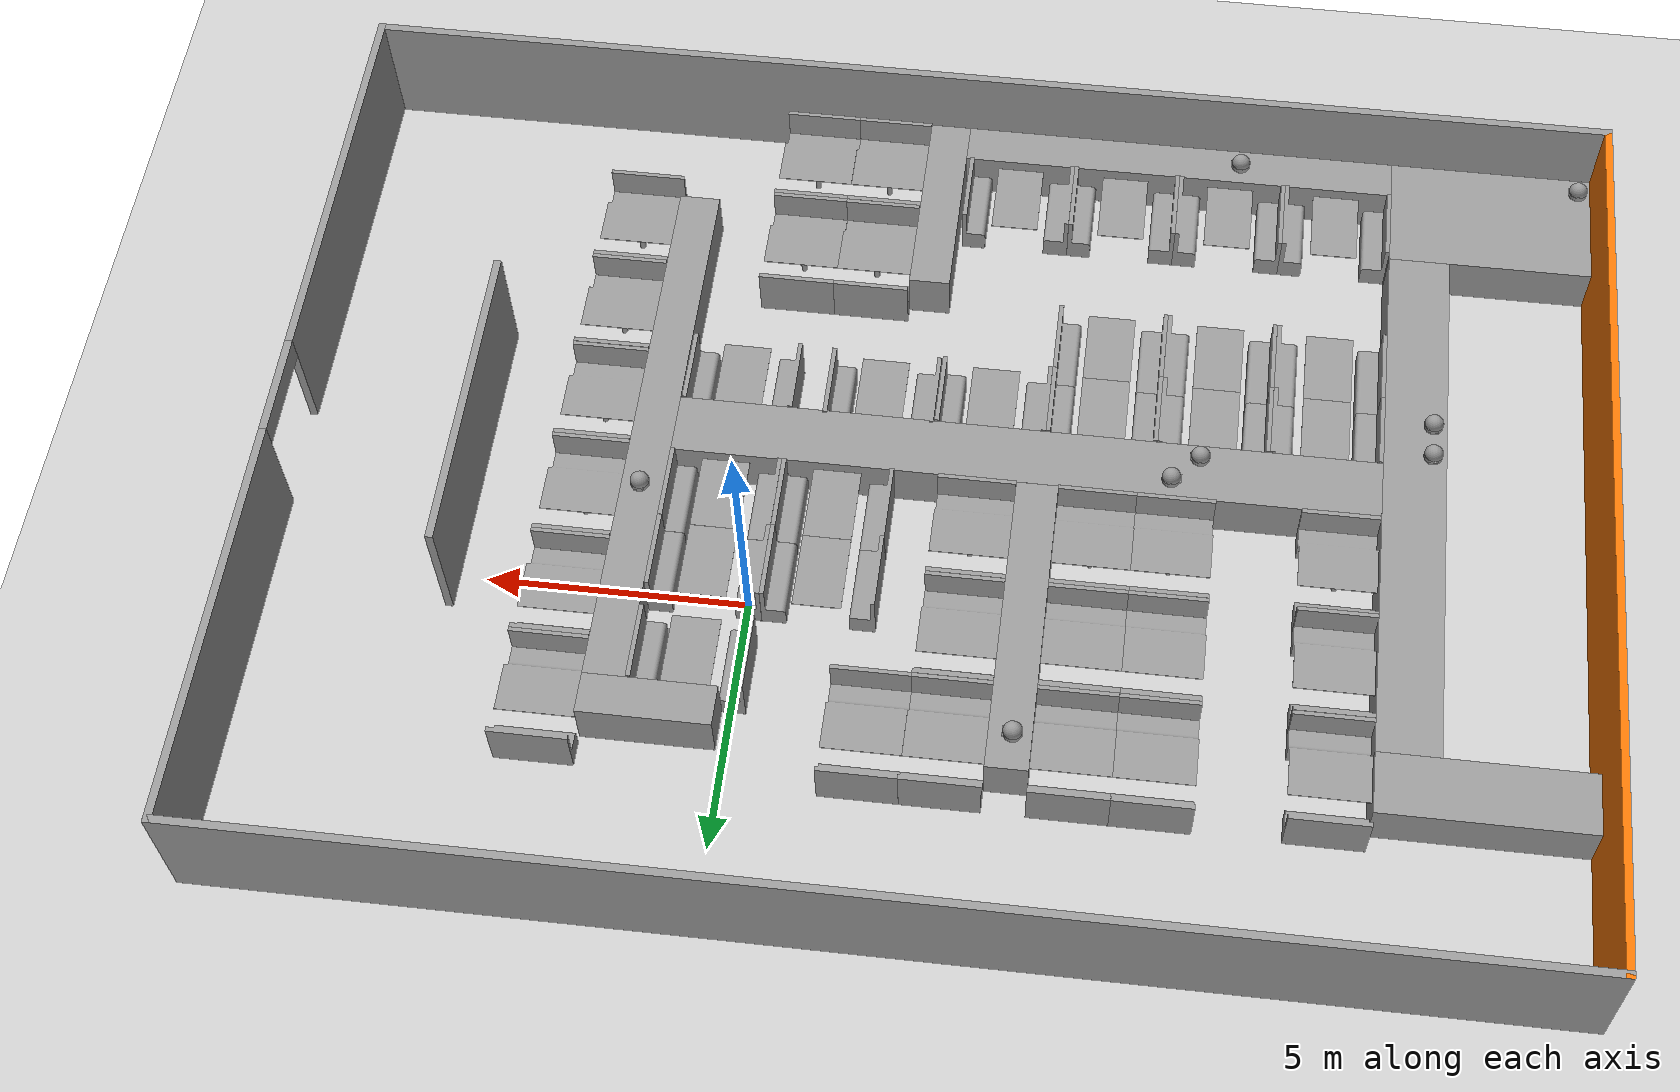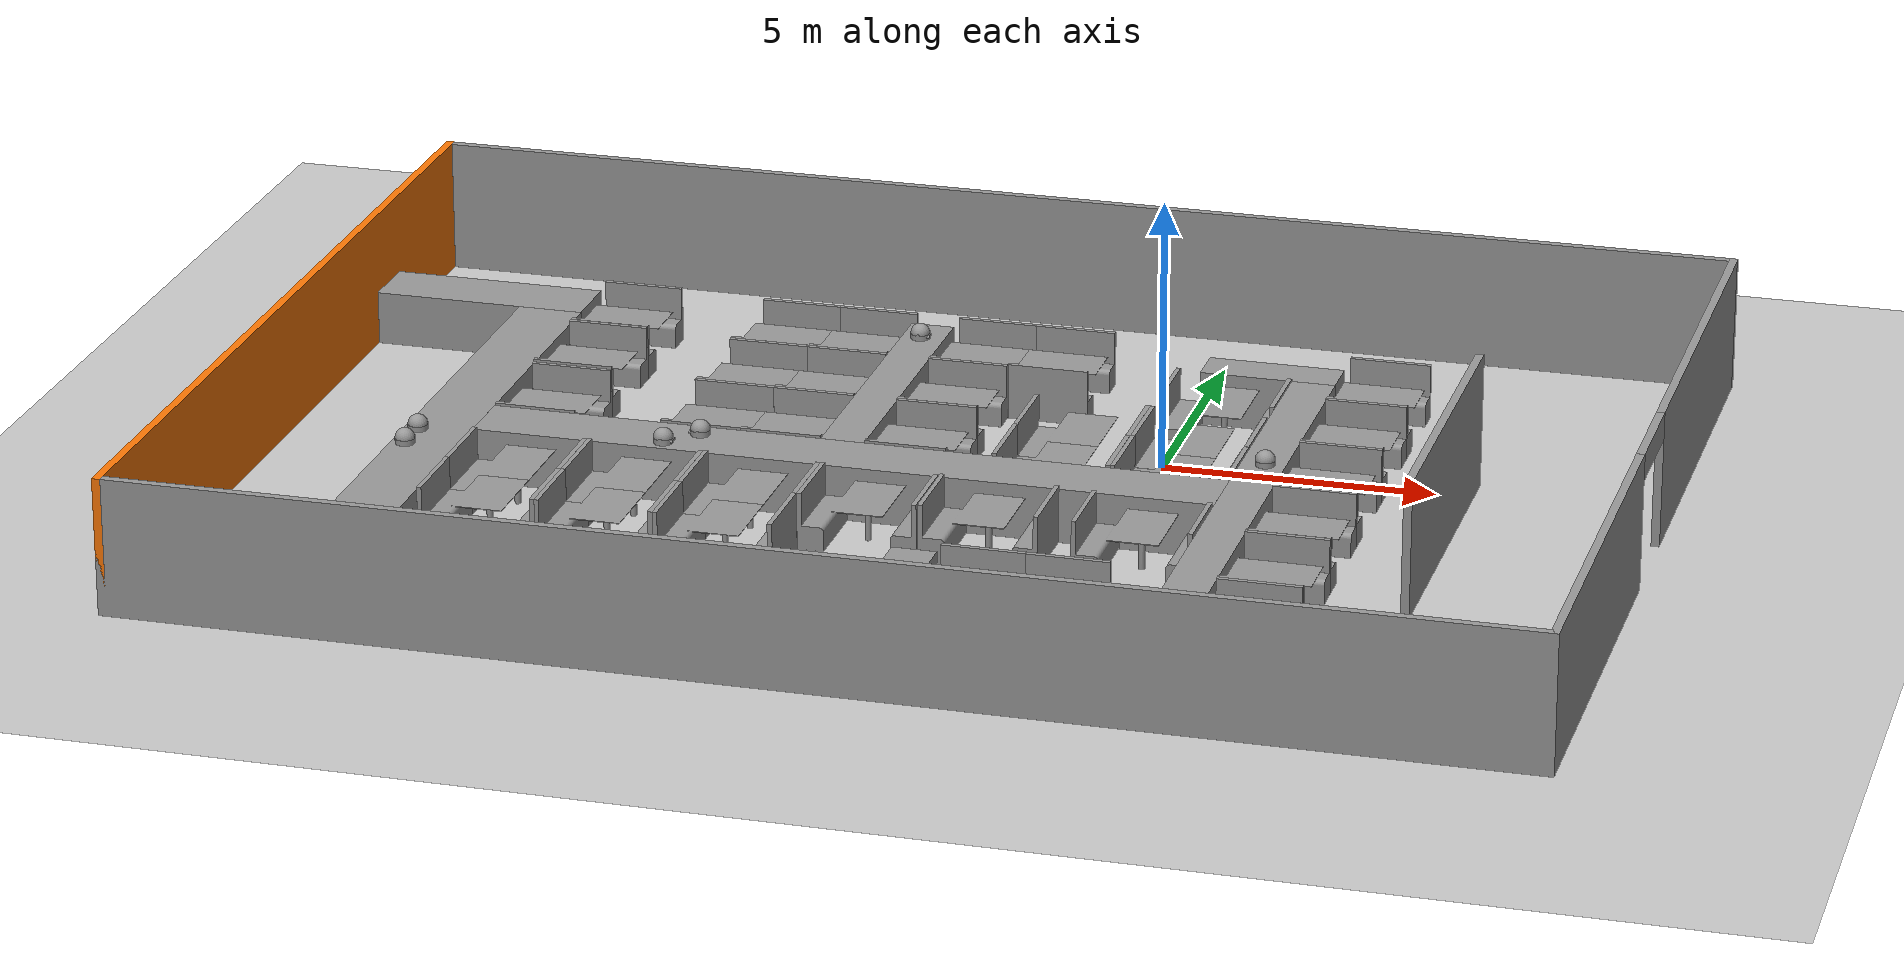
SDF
<sdf version="1.6">
 <world name="default">
  <plugin name="wellcome" filename="libwellcome.so"/>
  <light name="sun" type="directional">
   <pose>0 0 10 0 -0 0</pose>
   <diffuse>0.8 0.8 0.8 1</diffuse>
   <specular>0.2 0.2 0.2 1</specular>
   <attenuation>
    <range>1000</range>
    <constant>0.9</constant>
    <linear>0.01</linear>
    <quadratic>0.001</quadratic>
   </attenuation>
   <direction>-0.5 0.1 -0.9</direction>
  </light>
  <model name="ground_plane">
   <static>1</static>
   <link name="link">
    <collision name="collision">
     <geometry><plane><normal>0 0 1</normal><size>100 100</size></plane></geometry>
     <surface><friction><ode><mu>100</mu><mu2>50</mu2></ode></friction></surface>
    </collision>
    <visual name="visual">
     <cast_shadows>0</cast_shadows>
     <geometry><plane><normal>0 0 1</normal><size>100 100</size></plane></geometry>
     <material>
      <script><uri>file://media/materials/scripts/gazebo.material</uri><name>Gazebo/Grey</name></script>
     </material>
    </visual>
   </link>
  </model>
  <gravity>0 0 -9.8</gravity>
  <magnetic_field>6e-06 2.3e-05 -4.2e-05</magnetic_field>
  <atmosphere type="adiabatic"/>
  <physics name="default_physics" default="0" type="ode">
   <max_step_size>0.001</max_step_size>
   <real_time_factor>1</real_time_factor>
   <real_time_update_rate>1000</real_time_update_rate>
  </physics>
  <scene><ambient>0.4 0.4 0.4 1</ambient><background>0.7 0.7 0.7 1</background><shadows>1</shadows></scene>
  <spherical_coordinates>
   <surface_model>EARTH_WGS84</surface_model>
   <latitude_deg>0</latitude_deg>
   <longitude_deg>0</longitude_deg>
   <elevation>0</elevation>
   <heading_deg>0</heading_deg>
  </spherical_coordinates>
  <model name="restaurant">
   <pose>-3.2864 -2.31047 0 0 -0 0</pose>
   <link name="Wall_10">
    <collision name="Wall_10_Collision">
     <geometry><box><size>18 0.15 2.5</size></box></geometry>
     <pose>0 0 1.25 0 -0 0</pose>
    </collision>
    <visual name="Wall_10_Visual">
     <pose>0 0 1.25 0 -0 0</pose>
     <geometry><box><size>18 0.15 2.5</size></box></geometry>
     <material>
      <script><uri>file://media/materials/scripts/gazebo.material</uri><name>Gazebo/Grey</name></script>
      <ambient>0.996078 0.47451 0.0196078 1</ambient>
     </material>
     <meta><layer>0</layer></meta>
    </visual>
    <pose>-12.425 -0.0001 0 0 0 -1.5708</pose>
   </link>
   <link name="Wall_12">
    <collision name="Wall_12_Collision">
     <geometry><box><size>25 0.15 2.5</size></box></geometry>
     <pose>0 0 1.25 0 -0 0</pose>
    </collision>
    <visual name="Wall_12_Visual">
     <pose>0 0 1.25 0 -0 0</pose>
     <geometry><box><size>25 0.15 2.5</size></box></geometry>
     <material>
      <script><uri>file://media/materials/scripts/gazebo.material</uri><name>Gazebo/Grey</name></script>
      <ambient>1 1 1 1</ambient>
     </material>
     <meta><layer>0</layer></meta>
    </visual>
    <pose>-1e-06 -8.9251 0 0 -0 0</pose>
   </link>
   <link name="Wall_14">
    <pose>12.425 1e-05 0 0 -0 1.5708</pose>
    <visual name="Wall_14_Visual_0">
     <pose>-5.00641 0 1.25 0 -0 0</pose>
     <geometry><box><size>7.98717 0.15 2.5</size></box></geometry>
     <material>
      <script><uri>file://media/materials/scripts/gazebo.material</uri><name>Gazebo/Grey</name></script>
      <ambient>1 1 1 1</ambient>
     </material>
     <meta><layer>0</layer></meta>
    </visual>
    <collision name="Wall_14_Collision_0">
     <geometry><box><size>7.98717 0.15 2.5</size></box></geometry>
     <pose>-5.00641 0 1.25 0 -0 0</pose>
    </collision>
    <visual name="Wall_14_Visual_1">
     <pose>4.99359 0 1.25 0 -0 0</pose>
     <geometry><box><size>8.01282 0.15 2.5</size></box></geometry>
     <material>
      <script><uri>file://media/materials/scripts/gazebo.material</uri><name>Gazebo/Grey</name></script>
      <ambient>1 1 1 1</ambient>
     </material>
     <meta><layer>0</layer></meta>
    </visual>
    <collision name="Wall_14_Collision_1">
     <geometry><box><size>8.01282 0.15 2.5</size></box></geometry>
     <pose>4.99359 0 1.25 0 -0 0</pose>
    </collision>
    <visual name="Wall_14_Visual_2">
     <pose>-0.012825 0 2.25 0 -0 0</pose>
     <geometry><box><size>2 0.15 0.5</size></box></geometry>
     <material>
      <script><uri>file://media/materials/scripts/gazebo.material</uri><name>Gazebo/Grey</name></script>
      <ambient>1 1 1 1</ambient>
     </material>
     <meta><layer>0</layer></meta>
    </visual>
    <collision name="Wall_14_Collision_2">
     <geometry><box><size>2 0.15 0.5</size></box></geometry>
     <pose>-0.012825 0 2.25 0 -0 0</pose>
    </collision>
   </link>
   <link name="Wall_16">
    <collision name="Wall_16_Collision">
     <geometry><box><size>6.25 0.15 2.5</size></box></geometry>
     <pose>0 0 1.25 0 -0 0</pose>
    </collision>
    <visual name="Wall_16_Visual">
     <pose>0 0 1.25 0 -0 0</pose>
     <geometry><box><size>6.25 0.15 2.5</size></box></geometry>
     <material>
      <script><uri>file://media/materials/scripts/gazebo.material</uri><name>Gazebo/Grey</name></script>
      <ambient>1 1 1 1</ambient>
     </material>
     <meta><layer>0</layer></meta>
    </visual>
    <pose>8.88051 -0.186574 0 0 0 -1.5708</pose>
   </link>
   <link name="Wall_8">
    <collision name="Wall_8_Collision">
     <geometry><box><size>25 0.15 2.5</size></box></geometry>
     <pose>0 0 1.25 0 -0 0</pose>
    </collision>
    <visual name="Wall_8_Visual">
     <pose>0 0 1.25 0 -0 0</pose>
     <geometry><box><size>25 0.15 2.5</size></box></geometry>
     <material>
      <script><uri>file://media/materials/scripts/gazebo.material</uri><name>Gazebo/Grey</name></script>
      <ambient>1 1 1 1</ambient>
     </material>
     <meta><layer>0</layer></meta>
    </visual>
    <pose>1e-06 8.925 0 0 0 -3.14159</pose>
   </link>
   <static>1</static>
  </model>
  <model name="table_0">
   <link name="link_0">
    <inertial>
     <mass>1</mass>
     <inertia>
      <ixx>0.166667</ixx>
      <ixy>0</ixy>
      <ixz>0</ixz>
      <iyy>0.166667</iyy>
      <iyz>0</iyz>
      <izz>0.166667</izz>
     </inertia>
    </inertial>
    <visual name="visual">
     <pose>-1.9 -1.17 -0.5 0 -0 0</pose>
     <geometry><mesh><uri>model://table/mesh/table.dae</uri><scale>0.6 0.6 0.6</scale></mesh></geometry>
     <material>
      <lighting>1</lighting>
      <script><uri>file://media/materials/scripts/gazebo.material</uri><name>Gazebo/Grey</name></script>
      <shader type="pixel"><normal_map>__default__</normal_map></shader>
      <ambient>0.3 0.3 0.3 1</ambient>
      <diffuse>0.7 0.7 0.7 1</diffuse>
      <specular>0.01 0.01 0.01 1</specular>
      <emissive>0 0 0 1</emissive>
     </material>
    </visual>
    <collision name="collision">
     <geometry><box><size>2.2 1.5 1.1</size></box></geometry>
     <surface>
      <friction>
       <ode><mu>1</mu><mu2>1</mu2><fdir1>0 0 0</fdir1><slip1>0</slip1><slip2>0</slip2></ode>
       <torsional>
        <coefficient>1</coefficient>
        <patch_radius>0</patch_radius>
        <surface_radius>0</surface_radius>
        <use_patch_radius>1</use_patch_radius>
        <ode><slip>0</slip></ode>
       </torsional>
      </friction>
      <bounce><restitution_coefficient>0</restitution_coefficient><threshold>1e+06</threshold></bounce>
      <contact>
       <collide_without_contact>0</collide_without_contact>
       <collide_without_contact_bitmask>1</collide_without_contact_bitmask>
       <collide_bitmask>1</collide_bitmask>
       <ode>
        <soft_cfm>0</soft_cfm>
        <soft_erp>0.2</soft_erp>
        <kp>1e+13</kp>
        <kd>1</kd>
        <max_vel>0.01</max_vel>
        <min_depth>0</min_depth>
       </ode>
       <bullet>
        <split_impulse>1</split_impulse>
        <split_impulse_penetration_threshold>-0.01</split_impulse_penetration_threshold>
        <soft_cfm>0</soft_cfm>
        <soft_erp>0.2</soft_erp>
        <kp>1e+13</kp>
        <kd>1</kd>
       </bullet>
      </contact>
     </surface>
    </collision>
   </link>
   <static>1</static>
   <pose>-10.882 2.70214 0.55 0 -0 1.57127</pose>
  </model>
  <model name="table_1">
   <link name="link_0">
    <inertial>
     <mass>1</mass>
     <inertia>
      <ixx>0.166667</ixx>
      <ixy>0</ixy>
      <ixz>0</ixz>
      <iyy>0.166667</iyy>
      <iyz>0</iyz>
      <izz>0.166667</izz>
     </inertia>
    </inertial>
    <visual name="visual">
     <pose>-1.9 -1.17 -0.5 0 -0 0</pose>
     <geometry><mesh><uri>model://table/mesh/table.dae</uri><scale>0.6 0.6 0.6</scale></mesh></geometry>
     <material>
      <lighting>1</lighting>
      <script><uri>file://media/materials/scripts/gazebo.material</uri><name>Gazebo/Grey</name></script>
      <shader type="pixel"><normal_map>__default__</normal_map></shader>
      <ambient>0.3 0.3 0.3 1</ambient>
      <diffuse>0.7 0.7 0.7 1</diffuse>
      <specular>0.01 0.01 0.01 1</specular>
      <emissive>0 0 0 1</emissive>
     </material>
    </visual>
    <collision name="collision">
     <geometry><box><size>2.2 1.5 1.1</size></box></geometry>
     <surface>
      <friction>
       <ode><mu>1</mu><mu2>1</mu2><fdir1>0 0 0</fdir1><slip1>0</slip1><slip2>0</slip2></ode>
       <torsional>
        <coefficient>1</coefficient>
        <patch_radius>0</patch_radius>
        <surface_radius>0</surface_radius>
        <use_patch_radius>1</use_patch_radius>
        <ode><slip>0</slip></ode>
       </torsional>
      </friction>
      <bounce><restitution_coefficient>0</restitution_coefficient><threshold>1e+06</threshold></bounce>
      <contact>
       <collide_without_contact>0</collide_without_contact>
       <collide_without_contact_bitmask>1</collide_without_contact_bitmask>
       <collide_bitmask>1</collide_bitmask>
       <ode>
        <soft_cfm>0</soft_cfm>
        <soft_erp>0.2</soft_erp>
        <kp>1e+13</kp>
        <kd>1</kd>
        <max_vel>0.01</max_vel>
        <min_depth>0</min_depth>
       </ode>
       <bullet>
        <split_impulse>1</split_impulse>
        <split_impulse_penetration_threshold>-0.01</split_impulse_penetration_threshold>
        <soft_cfm>0</soft_cfm>
        <soft_erp>0.2</soft_erp>
        <kp>1e+13</kp>
        <kd>1</kd>
       </bullet>
      </contact>
     </surface>
    </collision>
   </link>
   <static>1</static>
   <pose>-10.8827 0.554165 0.54654 0 -0 1.5708</pose>
  </model>
  <model name="table">
   <link name="link_0">
    <inertial>
     <mass>1</mass>
     <inertia>
      <ixx>0.166667</ixx>
      <ixy>0</ixy>
      <ixz>0</ixz>
      <iyy>0.166667</iyy>
      <iyz>0</iyz>
      <izz>0.166667</izz>
     </inertia>
    </inertial>
    <visual name="visual">
     <pose>-1.9 -1.17 0 0 -0 0</pose>
     <geometry><mesh><uri>model://table/mesh/table.dae</uri><scale>0.6 0.6 0.6</scale></mesh></geometry>
     <material>
      <lighting>1</lighting>
      <script><uri>file://media/materials/scripts/gazebo.material</uri><name>Gazebo/Grey</name></script>
      <shader type="pixel"><normal_map>__default__</normal_map></shader>
      <ambient>0.3 0.3 0.3 1</ambient>
      <diffuse>0.7 0.7 0.7 1</diffuse>
      <specular>0.01 0.01 0.01 1</specular>
      <emissive>0 0 0 1</emissive>
     </material>
    </visual>
    <collision name="collision">
     <geometry><box><size>2.2 1.5 1.1</size></box></geometry>
     <surface>
      <friction>
       <ode><mu>1</mu><mu2>1</mu2><fdir1>0 0 0</fdir1><slip1>0</slip1><slip2>0</slip2></ode>
       <torsional>
        <coefficient>1</coefficient>
        <patch_radius>0</patch_radius>
        <surface_radius>0</surface_radius>
        <use_patch_radius>1</use_patch_radius>
        <ode><slip>0</slip></ode>
       </torsional>
      </friction>
      <bounce><restitution_coefficient>0</restitution_coefficient><threshold>1e+06</threshold></bounce>
      <contact>
       <collide_without_contact>0</collide_without_contact>
       <collide_without_contact_bitmask>1</collide_without_contact_bitmask>
       <collide_bitmask>1</collide_bitmask>
       <ode>
        <soft_cfm>0</soft_cfm>
        <soft_erp>0.2</soft_erp>
        <kp>1e+13</kp>
        <kd>1</kd>
        <max_vel>0.01</max_vel>
        <min_depth>0</min_depth>
       </ode>
       <bullet>
        <split_impulse>1</split_impulse>
        <split_impulse_penetration_threshold>-0.01</split_impulse_penetration_threshold>
        <soft_cfm>0</soft_cfm>
        <soft_erp>0.2</soft_erp>
        <kp>1e+13</kp>
        <kd>1</kd>
       </bullet>
      </contact>
     </surface>
    </collision>
   </link>
   <static>1</static>
   <pose>-10.891 -1.60546 0 0 0 -1.5708</pose>
  </model>
  <model name="table_2">
   <link name="link_0">
    <inertial>
     <mass>1</mass>
     <inertia>
      <ixx>0.166667</ixx>
      <ixy>0</ixy>
      <ixz>0</ixz>
      <iyy>0.166667</iyy>
      <iyz>0</iyz>
      <izz>0.166667</izz>
     </inertia>
    </inertial>
    <visual name="visual">
     <pose>-1.9 -1.17 0 0 -0 0</pose>
     <geometry><mesh><uri>model://table/mesh/table.dae</uri><scale>0.6 0.6 0.6</scale></mesh></geometry>
     <material>
      <lighting>1</lighting>
      <script><uri>file://media/materials/scripts/gazebo.material</uri><name>Gazebo/Grey</name></script>
      <shader type="pixel"><normal_map>__default__</normal_map></shader>
      <ambient>0.3 0.3 0.3 1</ambient>
      <diffuse>0.7 0.7 0.7 1</diffuse>
      <specular>0.01 0.01 0.01 1</specular>
      <emissive>0 0 0 1</emissive>
     </material>
    </visual>
    <collision name="collision">
     <geometry><box><size>2.2 1.5 1.1</size></box></geometry>
     <surface>
      <friction>
       <ode><mu>1</mu><mu2>1</mu2><fdir1>0 0 0</fdir1><slip1>0</slip1><slip2>0</slip2></ode>
       <torsional>
        <coefficient>1</coefficient>
        <patch_radius>0</patch_radius>
        <surface_radius>0</surface_radius>
        <use_patch_radius>1</use_patch_radius>
        <ode><slip>0</slip></ode>
       </torsional>
      </friction>
      <bounce><restitution_coefficient>0</restitution_coefficient><threshold>1e+06</threshold></bounce>
      <contact>
       <collide_without_contact>0</collide_without_contact>
       <collide_without_contact_bitmask>1</collide_without_contact_bitmask>
       <collide_bitmask>1</collide_bitmask>
       <ode>
        <soft_cfm>0</soft_cfm>
        <soft_erp>0.2</soft_erp>
        <kp>1e+13</kp>
        <kd>1</kd>
        <max_vel>0.01</max_vel>
        <min_depth>0</min_depth>
       </ode>
       <bullet>
        <split_impulse>1</split_impulse>
        <split_impulse_penetration_threshold>-0.01</split_impulse_penetration_threshold>
        <soft_cfm>0</soft_cfm>
        <soft_erp>0.2</soft_erp>
        <kp>1e+13</kp>
        <kd>1</kd>
       </bullet>
      </contact>
     </surface>
    </collision>
   </link>
   <static>1</static>
   <pose>-10.556 -4.6252 0 0 -0 0</pose>
  </model>
  <model name="table_3">
   <link name="link_0">
    <inertial>
     <mass>1</mass>
     <inertia>
      <ixx>0.166667</ixx>
      <ixy>0</ixy>
      <ixz>0</ixz>
      <iyy>0.166667</iyy>
      <iyz>0</iyz>
      <izz>0.166667</izz>
     </inertia>
    </inertial>
    <visual name="visual">
     <pose>-1.9 -1.17 0 0 -0 0</pose>
     <geometry><mesh><uri>model://table/mesh/table.dae</uri><scale>0.6 0.6 0.6</scale></mesh></geometry>
     <material>
      <lighting>1</lighting>
      <script><uri>file://media/materials/scripts/gazebo.material</uri><name>Gazebo/Grey</name></script>
      <shader type="pixel"><normal_map>__default__</normal_map></shader>
      <ambient>0.3 0.3 0.3 1</ambient>
      <diffuse>0.7 0.7 0.7 1</diffuse>
      <specular>0.01 0.01 0.01 1</specular>
      <emissive>0 0 0 1</emissive>
     </material>
    </visual>
    <collision name="collision">
     <geometry><box><size>2.2 1.5 1.1</size></box></geometry>
     <surface>
      <friction>
       <ode><mu>1</mu><mu2>1</mu2><fdir1>0 0 0</fdir1><slip1>0</slip1><slip2>0</slip2></ode>
       <torsional>
        <coefficient>1</coefficient>
        <patch_radius>0</patch_radius>
        <surface_radius>0</surface_radius>
        <use_patch_radius>1</use_patch_radius>
        <ode><slip>0</slip></ode>
       </torsional>
      </friction>
      <bounce><restitution_coefficient>0</restitution_coefficient><threshold>1e+06</threshold></bounce>
      <contact>
       <collide_without_contact>0</collide_without_contact>
       <collide_without_contact_bitmask>1</collide_without_contact_bitmask>
       <collide_bitmask>1</collide_bitmask>
       <ode>
        <soft_cfm>0</soft_cfm>
        <soft_erp>0.2</soft_erp>
        <kp>1e+13</kp>
        <kd>1</kd>
        <max_vel>0.01</max_vel>
        <min_depth>0</min_depth>
       </ode>
       <bullet>
        <split_impulse>1</split_impulse>
        <split_impulse_penetration_threshold>-0.01</split_impulse_penetration_threshold>
        <soft_cfm>0</soft_cfm>
        <soft_erp>0.2</soft_erp>
        <kp>1e+13</kp>
        <kd>1</kd>
       </bullet>
      </contact>
     </surface>
    </collision>
   </link>
   <static>1</static>
   <pose>-10.5559 -6.11096 0 0 -0 0</pose>
  </model>
  <model name="table_4">
   <link name="link_0">
    <inertial>
     <mass>1</mass>
     <inertia>
      <ixx>0.166667</ixx>
      <ixy>0</ixy>
      <ixz>0</ixz>
      <iyy>0.166667</iyy>
      <iyz>0</iyz>
      <izz>0.166667</izz>
     </inertia>
    </inertial>
    <visual name="visual">
     <pose>-1.9 -1.17 0 0 -0 0</pose>
     <geometry><mesh><uri>model://table/mesh/table.dae</uri><scale>0.6 0.6 0.6</scale></mesh></geometry>
     <material>
      <lighting>1</lighting>
      <script><uri>file://media/materials/scripts/gazebo.material</uri><name>Gazebo/Grey</name></script>
      <shader type="pixel"><normal_map>__default__</normal_map></shader>
      <ambient>0.3 0.3 0.3 1</ambient>
      <diffuse>0.7 0.7 0.7 1</diffuse>
      <specular>0.01 0.01 0.01 1</specular>
      <emissive>0 0 0 1</emissive>
     </material>
    </visual>
    <collision name="collision">
     <geometry><box><size>2.2 1.5 1.1</size></box></geometry>
     <surface>
      <friction>
       <ode><mu>1</mu><mu2>1</mu2><fdir1>0 0 0</fdir1><slip1>0</slip1><slip2>0</slip2></ode>
       <torsional>
        <coefficient>1</coefficient>
        <patch_radius>0</patch_radius>
        <surface_radius>0</surface_radius>
        <use_patch_radius>1</use_patch_radius>
        <ode><slip>0</slip></ode>
       </torsional>
      </friction>
      <bounce><restitution_coefficient>0</restitution_coefficient><threshold>1e+06</threshold></bounce>
      <contact>
       <collide_without_contact>0</collide_without_contact>
       <collide_without_contact_bitmask>1</collide_without_contact_bitmask>
       <collide_bitmask>1</collide_bitmask>
       <ode>
        <soft_cfm>0</soft_cfm>
        <soft_erp>0.2</soft_erp>
        <kp>1e+13</kp>
        <kd>1</kd>
        <max_vel>0.01</max_vel>
        <min_depth>0</min_depth>
       </ode>
       <bullet>
        <split_impulse>1</split_impulse>
        <split_impulse_penetration_threshold>-0.01</split_impulse_penetration_threshold>
        <soft_cfm>0</soft_cfm>
        <soft_erp>0.2</soft_erp>
        <kp>1e+13</kp>
        <kd>1</kd>
       </bullet>
      </contact>
     </surface>
    </collision>
   </link>
   <static>1</static>
   <pose>-10.5562 -9.62109 0 0 -0 0</pose>
  </model>
  <model name="table_5">
   <link name="link_0">
    <inertial>
     <mass>1</mass>
     <inertia>
      <ixx>0.166667</ixx>
      <ixy>0</ixy>
      <ixz>0</ixz>
      <iyy>0.166667</iyy>
      <iyz>0</iyz>
      <izz>0.166667</izz>
     </inertia>
    </inertial>
    <visual name="visual">
     <pose>-1.9 -1.17 0 0 -0 0</pose>
     <geometry><mesh><uri>model://table/mesh/table.dae</uri><scale>0.6 0.6 0.6</scale></mesh></geometry>
     <material>
      <lighting>1</lighting>
      <script><uri>file://media/materials/scripts/gazebo.material</uri><name>Gazebo/Grey</name></script>
      <shader type="pixel"><normal_map>__default__</normal_map></shader>
      <ambient>0.3 0.3 0.3 1</ambient>
      <diffuse>0.7 0.7 0.7 1</diffuse>
      <specular>0.01 0.01 0.01 1</specular>
      <emissive>0 0 0 1</emissive>
     </material>
    </visual>
    <collision name="collision">
     <geometry><box><size>2.2 1.5 1.1</size></box></geometry>
     <surface>
      <friction>
       <ode><mu>1</mu><mu2>1</mu2><fdir1>0 0 0</fdir1><slip1>0</slip1><slip2>0</slip2></ode>
       <torsional>
        <coefficient>1</coefficient>
        <patch_radius>0</patch_radius>
        <surface_radius>0</surface_radius>
        <use_patch_radius>1</use_patch_radius>
        <ode><slip>0</slip></ode>
       </torsional>
      </friction>
      <bounce><restitution_coefficient>0</restitution_coefficient><threshold>1e+06</threshold></bounce>
      <contact>
       <collide_without_contact>0</collide_without_contact>
       <collide_without_contact_bitmask>1</collide_without_contact_bitmask>
       <collide_bitmask>1</collide_bitmask>
       <ode>
        <soft_cfm>0</soft_cfm>
        <soft_erp>0.2</soft_erp>
        <kp>1e+13</kp>
        <kd>1</kd>
        <max_vel>0.01</max_vel>
        <min_depth>0</min_depth>
       </ode>
       <bullet>
        <split_impulse>1</split_impulse>
        <split_impulse_penetration_threshold>-0.01</split_impulse_penetration_threshold>
        <soft_cfm>0</soft_cfm>
        <soft_erp>0.2</soft_erp>
        <kp>1e+13</kp>
        <kd>1</kd>
       </bullet>
      </contact>
     </surface>
    </collision>
   </link>
   <static>1</static>
   <pose>-6.29706 -1.59971 0 0 -0 1.5708</pose>
  </model>
  <model name="table_6">
   <link name="link_0">
    <inertial>
     <mass>1</mass>
     <inertia>
      <ixx>0.166667</ixx>
      <ixy>0</ixy>
      <ixz>0</ixz>
      <iyy>0.166667</iyy>
      <iyz>0</iyz>
      <izz>0.166667</izz>
     </inertia>
    </inertial>
    <visual name="visual">
     <pose>-1.9 -1.17 0 0 -0 0</pose>
     <geometry><mesh><uri>model://table/mesh/table.dae</uri><scale>0.6 0.6 0.6</scale></mesh></geometry>
     <material>
      <lighting>1</lighting>
      <script><uri>file://media/materials/scripts/gazebo.material</uri><name>Gazebo/Grey</name></script>
      <shader type="pixel"><normal_map>__default__</normal_map></shader>
      <ambient>0.3 0.3 0.3 1</ambient>
      <diffuse>0.7 0.7 0.7 1</diffuse>
      <specular>0.01 0.01 0.01 1</specular>
      <emissive>0 0 0 1</emissive>
     </material>
    </visual>
    <collision name="collision">
     <geometry><box><size>2.2 1.5 1.1</size></box></geometry>
     <surface>
      <friction>
       <ode><mu>1</mu><mu2>1</mu2><fdir1>0 0 0</fdir1><slip1>0</slip1><slip2>0</slip2></ode>
       <torsional>
        <coefficient>1</coefficient>
        <patch_radius>0</patch_radius>
        <surface_radius>0</surface_radius>
        <use_patch_radius>1</use_patch_radius>
        <ode><slip>0</slip></ode>
       </torsional>
      </friction>
      <bounce><restitution_coefficient>0</restitution_coefficient><threshold>1e+06</threshold></bounce>
      <contact>
       <collide_without_contact>0</collide_without_contact>
       <collide_without_contact_bitmask>1</collide_without_contact_bitmask>
       <collide_bitmask>1</collide_bitmask>
       <ode>
        <soft_cfm>0</soft_cfm>
        <soft_erp>0.2</soft_erp>
        <kp>1e+13</kp>
        <kd>1</kd>
        <max_vel>0.01</max_vel>
        <min_depth>0</min_depth>
       </ode>
       <bullet>
        <split_impulse>1</split_impulse>
        <split_impulse_penetration_threshold>-0.01</split_impulse_penetration_threshold>
        <soft_cfm>0</soft_cfm>
        <soft_erp>0.2</soft_erp>
        <kp>1e+13</kp>
        <kd>1</kd>
       </bullet>
      </contact>
     </surface>
    </collision>
   </link>
   <static>1</static>
   <pose>-8.4127 -4.62519 0 0 -0 0</pose>
  </model>
  <model name="table_7">
   <link name="link_0">
    <inertial>
     <mass>1</mass>
     <inertia>
      <ixx>0.166667</ixx>
      <ixy>0</ixy>
      <ixz>0</ixz>
      <iyy>0.166667</iyy>
      <iyz>0</iyz>
      <izz>0.166667</izz>
     </inertia>
    </inertial>
    <visual name="visual">
     <pose>-1.9 -1.17 0 0 -0 0</pose>
     <geometry><mesh><uri>model://table/mesh/table.dae</uri><scale>0.6 0.6 0.6</scale></mesh></geometry>
     <material>
      <lighting>1</lighting>
      <script><uri>file://media/materials/scripts/gazebo.material</uri><name>Gazebo/Grey</name></script>
      <shader type="pixel"><normal_map>__default__</normal_map></shader>
      <ambient>0.3 0.3 0.3 1</ambient>
      <diffuse>0.7 0.7 0.7 1</diffuse>
      <specular>0.01 0.01 0.01 1</specular>
      <emissive>0 0 0 1</emissive>
     </material>
    </visual>
    <collision name="collision">
     <geometry><box><size>2.2 1.5 1.1</size></box></geometry>
     <surface>
      <friction>
       <ode><mu>1</mu><mu2>1</mu2><fdir1>0 0 0</fdir1><slip1>0</slip1><slip2>0</slip2></ode>
       <torsional>
        <coefficient>1</coefficient>
        <patch_radius>0</patch_radius>
        <surface_radius>0</surface_radius>
        <use_patch_radius>1</use_patch_radius>
        <ode><slip>0</slip></ode>
       </torsional>
      </friction>
      <bounce><restitution_coefficient>0</restitution_coefficient><threshold>1e+06</threshold></bounce>
      <contact>
       <collide_without_contact>0</collide_without_contact>
       <collide_without_contact_bitmask>1</collide_without_contact_bitmask>
       <collide_bitmask>1</collide_bitmask>
       <ode>
        <soft_cfm>0</soft_cfm>
        <soft_erp>0.2</soft_erp>
        <kp>1e+13</kp>
        <kd>1</kd>
        <max_vel>0.01</max_vel>
        <min_depth>0</min_depth>
       </ode>
       <bullet>
        <split_impulse>1</split_impulse>
        <split_impulse_penetration_threshold>-0.01</split_impulse_penetration_threshold>
        <soft_cfm>0</soft_cfm>
        <soft_erp>0.2</soft_erp>
        <kp>1e+13</kp>
        <kd>1</kd>
       </bullet>
      </contact>
     </surface>
    </collision>
   </link>
   <static>1</static>
   <pose>-8.41264 -6.11092 0 0 -0 0</pose>
  </model>
  <model name="table_8">
   <link name="link_0">
    <inertial>
     <mass>1</mass>
     <inertia>
      <ixx>0.166667</ixx>
      <ixy>0</ixy>
      <ixz>0</ixz>
      <iyy>0.166667</iyy>
      <iyz>0</iyz>
      <izz>0.166667</izz>
     </inertia>
    </inertial>
    <visual name="visual">
     <pose>-1.9 -1.17 0 0 -0 0</pose>
     <geometry><mesh><uri>model://table/mesh/table.dae</uri><scale>0.6 0.6 0.6</scale></mesh></geometry>
     <material>
      <lighting>1</lighting>
      <script><uri>file://media/materials/scripts/gazebo.material</uri><name>Gazebo/Grey</name></script>
      <shader type="pixel"><normal_map>__default__</normal_map></shader>
      <ambient>0.3 0.3 0.3 1</ambient>
      <diffuse>0.7 0.7 0.7 1</diffuse>
      <specular>0.01 0.01 0.01 1</specular>
      <emissive>0 0 0 1</emissive>
     </material>
    </visual>
    <collision name="collision">
     <geometry><box><size>2.2 1.5 1.1</size></box></geometry>
     <surface>
      <friction>
       <ode><mu>1</mu><mu2>1</mu2><fdir1>0 0 0</fdir1><slip1>0</slip1><slip2>0</slip2></ode>
       <torsional>
        <coefficient>1</coefficient>
        <patch_radius>0</patch_radius>
        <surface_radius>0</surface_radius>
        <use_patch_radius>1</use_patch_radius>
        <ode><slip>0</slip></ode>
       </torsional>
      </friction>
      <bounce><restitution_coefficient>0</restitution_coefficient><threshold>1e+06</threshold></bounce>
      <contact>
       <collide_without_contact>0</collide_without_contact>
       <collide_without_contact_bitmask>1</collide_without_contact_bitmask>
       <collide_bitmask>1</collide_bitmask>
       <ode>
        <soft_cfm>0</soft_cfm>
        <soft_erp>0.2</soft_erp>
        <kp>1e+13</kp>
        <kd>1</kd>
        <max_vel>0.01</max_vel>
        <min_depth>0</min_depth>
       </ode>
       <bullet>
        <split_impulse>1</split_impulse>
        <split_impulse_penetration_threshold>-0.01</split_impulse_penetration_threshold>
        <soft_cfm>0</soft_cfm>
        <soft_erp>0.2</soft_erp>
        <kp>1e+13</kp>
        <kd>1</kd>
       </bullet>
      </contact>
     </surface>
    </collision>
   </link>
   <static>1</static>
   <pose>-8.41293 -9.62133 0 0 -0 0</pose>
  </model>
  <model name="table_9">
   <link name="link_0">
    <inertial>
     <mass>1</mass>
     <inertia>
      <ixx>0.166667</ixx>
      <ixy>0</ixy>
      <ixz>0</ixz>
      <iyy>0.166667</iyy>
      <iyz>0</iyz>
      <izz>0.166667</izz>
     </inertia>
    </inertial>
    <visual name="visual">
     <pose>-1.9 -1.17 0 0 -0 0</pose>
     <geometry><mesh><uri>model://table/mesh/table.dae</uri><scale>0.6 0.6 0.6</scale></mesh></geometry>
     <material>
      <lighting>1</lighting>
      <script><uri>file://media/materials/scripts/gazebo.material</uri><name>Gazebo/Grey</name></script>
      <shader type="pixel"><normal_map>__default__</normal_map></shader>
      <ambient>0.3 0.3 0.3 1</ambient>
      <diffuse>0.7 0.7 0.7 1</diffuse>
      <specular>0.01 0.01 0.01 1</specular>
      <emissive>0 0 0 1</emissive>
     </material>
    </visual>
    <collision name="collision">
     <geometry><box><size>2.2 1.5 1.1</size></box></geometry>
     <surface>
      <friction>
       <ode><mu>1</mu><mu2>1</mu2><fdir1>0 0 0</fdir1><slip1>0</slip1><slip2>0</slip2></ode>
       <torsional>
        <coefficient>1</coefficient>
        <patch_radius>0</patch_radius>
        <surface_radius>0</surface_radius>
        <use_patch_radius>1</use_patch_radius>
        <ode><slip>0</slip></ode>
       </torsional>
      </friction>
      <bounce><restitution_coefficient>0</restitution_coefficient><threshold>1e+06</threshold></bounce>
      <contact>
       <collide_without_contact>0</collide_without_contact>
       <collide_without_contact_bitmask>1</collide_without_contact_bitmask>
       <collide_bitmask>1</collide_bitmask>
       <ode>
        <soft_cfm>0</soft_cfm>
        <soft_erp>0.2</soft_erp>
        <kp>1e+13</kp>
        <kd>1</kd>
        <max_vel>0.01</max_vel>
        <min_depth>0</min_depth>
       </ode>
       <bullet>
        <split_impulse>1</split_impulse>
        <split_impulse_penetration_threshold>-0.01</split_impulse_penetration_threshold>
        <soft_cfm>0</soft_cfm>
        <soft_erp>0.2</soft_erp>
        <kp>1e+13</kp>
        <kd>1</kd>
       </bullet>
      </contact>
     </surface>
    </collision>
   </link>
   <static>1</static>
   <pose>-6.26938 -4.6265 0 0 -0 0</pose>
  </model>
  <model name="table_10">
   <link name="link_0">
    <inertial>
     <mass>1</mass>
     <inertia>
      <ixx>0.166667</ixx>
      <ixy>0</ixy>
      <ixz>0</ixz>
      <iyy>0.166667</iyy>
      <iyz>0</iyz>
      <izz>0.166667</izz>
     </inertia>
    </inertial>
    <visual name="visual">
     <pose>-1.9 -1.17 0 0 -0 0</pose>
     <geometry><mesh><uri>model://table/mesh/table.dae</uri><scale>0.6 0.6 0.6</scale></mesh></geometry>
     <material>
      <lighting>1</lighting>
      <script><uri>file://media/materials/scripts/gazebo.material</uri><name>Gazebo/Grey</name></script>
      <shader type="pixel"><normal_map>__default__</normal_map></shader>
      <ambient>0.3 0.3 0.3 1</ambient>
      <diffuse>0.7 0.7 0.7 1</diffuse>
      <specular>0.01 0.01 0.01 1</specular>
      <emissive>0 0 0 1</emissive>
     </material>
    </visual>
    <collision name="collision">
     <geometry><box><size>2.2 1.5 1.1</size></box></geometry>
     <surface>
      <friction>
       <ode><mu>1</mu><mu2>1</mu2><fdir1>0 0 0</fdir1><slip1>0</slip1><slip2>0</slip2></ode>
       <torsional>
        <coefficient>1</coefficient>
        <patch_radius>0</patch_radius>
        <surface_radius>0</surface_radius>
        <use_patch_radius>1</use_patch_radius>
        <ode><slip>0</slip></ode>
       </torsional>
      </friction>
      <bounce><restitution_coefficient>0</restitution_coefficient><threshold>1e+06</threshold></bounce>
      <contact>
       <collide_without_contact>0</collide_without_contact>
       <collide_without_contact_bitmask>1</collide_without_contact_bitmask>
       <collide_bitmask>1</collide_bitmask>
       <ode>
        <soft_cfm>0</soft_cfm>
        <soft_erp>0.2</soft_erp>
        <kp>1e+13</kp>
        <kd>1</kd>
        <max_vel>0.01</max_vel>
        <min_depth>0</min_depth>
       </ode>
       <bullet>
        <split_impulse>1</split_impulse>
        <split_impulse_penetration_threshold>-0.01</split_impulse_penetration_threshold>
        <soft_cfm>0</soft_cfm>
        <soft_erp>0.2</soft_erp>
        <kp>1e+13</kp>
        <kd>1</kd>
       </bullet>
      </contact>
     </surface>
    </collision>
   </link>
   <static>1</static>
   <pose>-6.26919 -6.11225 0 0 -0 0</pose>
  </model>
  <model name="table_11">
   <link name="link_0">
    <inertial>
     <mass>1</mass>
     <inertia>
      <ixx>0.166667</ixx>
      <ixy>0</ixy>
      <ixz>0</ixz>
      <iyy>0.166667</iyy>
      <iyz>0</iyz>
      <izz>0.166667</izz>
     </inertia>
    </inertial>
    <visual name="visual">
     <pose>-1.9 -1.17 0 0 -0 0</pose>
     <geometry><mesh><uri>model://table/mesh/table.dae</uri><scale>0.6 0.6 0.6</scale></mesh></geometry>
     <material>
      <lighting>1</lighting>
      <script><uri>file://media/materials/scripts/gazebo.material</uri><name>Gazebo/Grey</name></script>
      <shader type="pixel"><normal_map>__default__</normal_map></shader>
      <ambient>0.3 0.3 0.3 1</ambient>
      <diffuse>0.7 0.7 0.7 1</diffuse>
      <specular>0.01 0.01 0.01 1</specular>
      <emissive>0 0 0 1</emissive>
     </material>
    </visual>
    <collision name="collision">
     <geometry><box><size>2.2 1.5 1.1</size></box></geometry>
     <surface>
      <friction>
       <ode><mu>1</mu><mu2>1</mu2><fdir1>0 0 0</fdir1><slip1>0</slip1><slip2>0</slip2></ode>
       <torsional>
        <coefficient>1</coefficient>
        <patch_radius>0</patch_radius>
        <surface_radius>0</surface_radius>
        <use_patch_radius>1</use_patch_radius>
        <ode><slip>0</slip></ode>
       </torsional>
      </friction>
      <bounce><restitution_coefficient>0</restitution_coefficient><threshold>1e+06</threshold></bounce>
      <contact>
       <collide_without_contact>0</collide_without_contact>
       <collide_without_contact_bitmask>1</collide_without_contact_bitmask>
       <collide_bitmask>1</collide_bitmask>
       <ode>
        <soft_cfm>0</soft_cfm>
        <soft_erp>0.2</soft_erp>
        <kp>1e+13</kp>
        <kd>1</kd>
        <max_vel>0.01</max_vel>
        <min_depth>0</min_depth>
       </ode>
       <bullet>
        <split_impulse>1</split_impulse>
        <split_impulse_penetration_threshold>-0.01</split_impulse_penetration_threshold>
        <soft_cfm>0</soft_cfm>
        <soft_erp>0.2</soft_erp>
        <kp>1e+13</kp>
        <kd>1</kd>
       </bullet>
      </contact>
     </surface>
    </collision>
   </link>
   <static>1</static>
   <pose>-6.26952 -9.62125 0 0 -0 0</pose>
  </model>
  <model name="table_12">
   <link name="link_0">
    <inertial>
     <mass>1</mass>
     <inertia>
      <ixx>0.166667</ixx>
      <ixy>0</ixy>
      <ixz>0</ixz>
      <iyy>0.166667</iyy>
      <iyz>0</iyz>
      <izz>0.166667</izz>
     </inertia>
    </inertial>
    <visual name="visual">
     <pose>-1.9 -1.17 0 0 -0 0</pose>
     <geometry><mesh><uri>model://table/mesh/table.dae</uri><scale>0.6 0.6 0.6</scale></mesh></geometry>
     <material>
      <lighting>1</lighting>
      <script><uri>file://media/materials/scripts/gazebo.material</uri><name>Gazebo/Grey</name></script>
      <shader type="pixel"><normal_map>__default__</normal_map></shader>
      <ambient>0.3 0.3 0.3 1</ambient>
      <diffuse>0.7 0.7 0.7 1</diffuse>
      <specular>0.01 0.01 0.01 1</specular>
      <emissive>0 0 0 1</emissive>
     </material>
    </visual>
    <collision name="collision">
     <geometry><box><size>2.2 1.5 1.1</size></box></geometry>
     <surface>
      <friction>
       <ode><mu>1</mu><mu2>1</mu2><fdir1>0 0 0</fdir1><slip1>0</slip1><slip2>0</slip2></ode>
       <torsional>
        <coefficient>1</coefficient>
        <patch_radius>0</patch_radius>
        <surface_radius>0</surface_radius>
        <use_patch_radius>1</use_patch_radius>
        <ode><slip>0</slip></ode>
       </torsional>
      </friction>
      <bounce><restitution_coefficient>0</restitution_coefficient><threshold>1e+06</threshold></bounce>
      <contact>
       <collide_without_contact>0</collide_without_contact>
       <collide_without_contact_bitmask>1</collide_without_contact_bitmask>
       <collide_bitmask>1</collide_bitmask>
       <ode>
        <soft_cfm>0</soft_cfm>
        <soft_erp>0.2</soft_erp>
        <kp>1e+13</kp>
        <kd>1</kd>
        <max_vel>0.01</max_vel>
        <min_depth>0</min_depth>
       </ode>
       <bullet>
        <split_impulse>1</split_impulse>
        <split_impulse_penetration_threshold>-0.01</split_impulse_penetration_threshold>
        <soft_cfm>0</soft_cfm>
        <soft_erp>0.2</soft_erp>
        <kp>1e+13</kp>
        <kd>1</kd>
       </bullet>
      </contact>
     </surface>
    </collision>
   </link>
   <static>1</static>
   <pose>-4.12488 -9.62018 0 0 -0 0</pose>
  </model>
  <model name="table_13">
   <link name="link_0">
    <inertial>
     <mass>1</mass>
     <inertia>
      <ixx>0.166667</ixx>
      <ixy>0</ixy>
      <ixz>0</ixz>
      <iyy>0.166667</iyy>
      <iyz>0</iyz>
      <izz>0.166667</izz>
     </inertia>
    </inertial>
    <visual name="visual">
     <pose>-1.9 -1.17 0 0 -0 0</pose>
     <geometry><mesh><uri>model://table/mesh/table.dae</uri><scale>0.6 0.6 0.6</scale></mesh></geometry>
     <material>
      <lighting>1</lighting>
      <script><uri>file://media/materials/scripts/gazebo.material</uri><name>Gazebo/Grey</name></script>
      <shader type="pixel"><normal_map>__default__</normal_map></shader>
      <ambient>0.3 0.3 0.3 1</ambient>
      <diffuse>0.7 0.7 0.7 1</diffuse>
      <specular>0.01 0.01 0.01 1</specular>
      <emissive>0 0 0 1</emissive>
     </material>
    </visual>
    <collision name="collision">
     <geometry><box><size>2.2 1.5 1.1</size></box></geometry>
     <surface>
      <friction>
       <ode><mu>1</mu><mu2>1</mu2><fdir1>0 0 0</fdir1><slip1>0</slip1><slip2>0</slip2></ode>
       <torsional>
        <coefficient>1</coefficient>
        <patch_radius>0</patch_radius>
        <surface_radius>0</surface_radius>
        <use_patch_radius>1</use_patch_radius>
        <ode><slip>0</slip></ode>
       </torsional>
      </friction>
      <bounce><restitution_coefficient>0</restitution_coefficient><threshold>1e+06</threshold></bounce>
      <contact>
       <collide_without_contact>0</collide_without_contact>
       <collide_without_contact_bitmask>1</collide_without_contact_bitmask>
       <collide_bitmask>1</collide_bitmask>
       <ode>
        <soft_cfm>0</soft_cfm>
        <soft_erp>0.2</soft_erp>
        <kp>1e+13</kp>
        <kd>1</kd>
        <max_vel>0.01</max_vel>
        <min_depth>0</min_depth>
       </ode>
       <bullet>
        <split_impulse>1</split_impulse>
        <split_impulse_penetration_threshold>-0.01</split_impulse_penetration_threshold>
        <soft_cfm>0</soft_cfm>
        <soft_erp>0.2</soft_erp>
        <kp>1e+13</kp>
        <kd>1</kd>
       </bullet>
      </contact>
     </surface>
    </collision>
   </link>
   <static>1</static>
   <pose>-4.12506 -4.62605 0 0 -0 0</pose>
  </model>
  <model name="table_14">
   <link name="link_0">
    <inertial>
     <mass>1</mass>
     <inertia>
      <ixx>0.166667</ixx>
      <ixy>0</ixy>
      <ixz>0</ixz>
      <iyy>0.166667</iyy>
      <iyz>0</iyz>
      <izz>0.166667</izz>
     </inertia>
    </inertial>
    <visual name="visual">
     <pose>-1.9 -1.17 0 0 -0 0</pose>
     <geometry><mesh><uri>model://table/mesh/table.dae</uri><scale>0.6 0.6 0.6</scale></mesh></geometry>
     <material>
      <lighting>1</lighting>
      <script><uri>file://media/materials/scripts/gazebo.material</uri><name>Gazebo/Grey</name></script>
      <shader type="pixel"><normal_map>__default__</normal_map></shader>
      <ambient>0.3 0.3 0.3 1</ambient>
      <diffuse>0.7 0.7 0.7 1</diffuse>
      <specular>0.01 0.01 0.01 1</specular>
      <emissive>0 0 0 1</emissive>
     </material>
    </visual>
    <collision name="collision">
     <geometry><box><size>2.2 1.5 1.1</size></box></geometry>
     <surface>
      <friction>
       <ode><mu>1</mu><mu2>1</mu2><fdir1>0 0 0</fdir1><slip1>0</slip1><slip2>0</slip2></ode>
       <torsional>
        <coefficient>1</coefficient>
        <patch_radius>0</patch_radius>
        <surface_radius>0</surface_radius>
        <use_patch_radius>1</use_patch_radius>
        <ode><slip>0</slip></ode>
       </torsional>
      </friction>
      <bounce><restitution_coefficient>0</restitution_coefficient><threshold>1e+06</threshold></bounce>
      <contact>
       <collide_without_contact>0</collide_without_contact>
       <collide_without_contact_bitmask>1</collide_without_contact_bitmask>
       <collide_bitmask>1</collide_bitmask>
       <ode>
        <soft_cfm>0</soft_cfm>
        <soft_erp>0.2</soft_erp>
        <kp>1e+13</kp>
        <kd>1</kd>
        <max_vel>0.01</max_vel>
        <min_depth>0</min_depth>
       </ode>
       <bullet>
        <split_impulse>1</split_impulse>
        <split_impulse_penetration_threshold>-0.01</split_impulse_penetration_threshold>
        <soft_cfm>0</soft_cfm>
        <soft_erp>0.2</soft_erp>
        <kp>1e+13</kp>
        <kd>1</kd>
       </bullet>
      </contact>
     </surface>
    </collision>
   </link>
   <static>1</static>
   <pose>-6.29675 2.68796 0 0 -0 1.5708</pose>
  </model>
  <model name="table_15">
   <link name="link_0">
    <inertial>
     <mass>1</mass>
     <inertia>
      <ixx>0.166667</ixx>
      <ixy>0</ixy>
      <ixz>0</ixz>
      <iyy>0.166667</iyy>
      <iyz>0</iyz>
      <izz>0.166667</izz>
     </inertia>
    </inertial>
    <visual name="visual">
     <pose>-1.9 -1.17 0 0 -0 0</pose>
     <geometry><mesh><uri>model://table/mesh/table.dae</uri><scale>0.6 0.6 0.6</scale></mesh></geometry>
     <material>
      <lighting>1</lighting>
      <script><uri>file://media/materials/scripts/gazebo.material</uri><name>Gazebo/Grey</name></script>
      <shader type="pixel"><normal_map>__default__</normal_map></shader>
      <ambient>0.3 0.3 0.3 1</ambient>
      <diffuse>0.7 0.7 0.7 1</diffuse>
      <specular>0.01 0.01 0.01 1</specular>
      <emissive>0 0 0 1</emissive>
     </material>
    </visual>
    <collision name="collision">
     <geometry><box><size>2.2 1.5 1.1</size></box></geometry>
     <surface>
      <friction>
       <ode><mu>1</mu><mu2>1</mu2><fdir1>0 0 0</fdir1><slip1>0</slip1><slip2>0</slip2></ode>
       <torsional>
        <coefficient>1</coefficient>
        <patch_radius>0</patch_radius>
        <surface_radius>0</surface_radius>
        <use_patch_radius>1</use_patch_radius>
        <ode><slip>0</slip></ode>
       </torsional>
      </friction>
      <bounce><restitution_coefficient>0</restitution_coefficient><threshold>1e+06</threshold></bounce>
      <contact>
       <collide_without_contact>0</collide_without_contact>
       <collide_without_contact_bitmask>1</collide_without_contact_bitmask>
       <collide_bitmask>1</collide_bitmask>
       <ode>
        <soft_cfm>0</soft_cfm>
        <soft_erp>0.2</soft_erp>
        <kp>1e+13</kp>
        <kd>1</kd>
        <max_vel>0.01</max_vel>
        <min_depth>0</min_depth>
       </ode>
       <bullet>
        <split_impulse>1</split_impulse>
        <split_impulse_penetration_threshold>-0.01</split_impulse_penetration_threshold>
        <soft_cfm>0</soft_cfm>
        <soft_erp>0.2</soft_erp>
        <kp>1e+13</kp>
        <kd>1</kd>
       </bullet>
      </contact>
     </surface>
    </collision>
   </link>
   <static>1</static>
   <pose>-6.29694 0.543606 0 0 -0 1.5708</pose>
  </model>
  <model name="table_16">
   <link name="link_0">
    <inertial>
     <mass>1</mass>
     <inertia>
      <ixx>0.166667</ixx>
      <ixy>0</ixy>
      <ixz>0</ixz>
      <iyy>0.166667</iyy>
      <iyz>0</iyz>
      <izz>0.166667</izz>
     </inertia>
    </inertial>
    <visual name="visual">
     <pose>-1.9 -1.17 0 0 -0 0</pose>
     <geometry><mesh><uri>model://table/mesh/table.dae</uri><scale>0.6 0.6 0.6</scale></mesh></geometry>
     <material>
      <lighting>1</lighting>
      <script><uri>file://media/materials/scripts/gazebo.material</uri><name>Gazebo/Grey</name></script>
      <shader type="pixel"><normal_map>__default__</normal_map></shader>
      <ambient>0.3 0.3 0.3 1</ambient>
      <diffuse>0.7 0.7 0.7 1</diffuse>
      <specular>0.01 0.01 0.01 1</specular>
      <emissive>0 0 0 1</emissive>
     </material>
    </visual>
    <collision name="collision">
     <geometry><box><size>2.2 1.5 1.1</size></box></geometry>
     <surface>
      <friction>
       <ode><mu>1</mu><mu2>1</mu2><fdir1>0 0 0</fdir1><slip1>0</slip1><slip2>0</slip2></ode>
       <torsional>
        <coefficient>1</coefficient>
        <patch_radius>0</patch_radius>
        <surface_radius>0</surface_radius>
        <use_patch_radius>1</use_patch_radius>
        <ode><slip>0</slip></ode>
       </torsional>
      </friction>
      <bounce><restitution_coefficient>0</restitution_coefficient><threshold>1e+06</threshold></bounce>
      <contact>
       <collide_without_contact>0</collide_without_contact>
       <collide_without_contact_bitmask>1</collide_without_contact_bitmask>
       <collide_bitmask>1</collide_bitmask>
       <ode>
        <soft_cfm>0</soft_cfm>
        <soft_erp>0.2</soft_erp>
        <kp>1e+13</kp>
        <kd>1</kd>
        <max_vel>0.01</max_vel>
        <min_depth>0</min_depth>
       </ode>
       <bullet>
        <split_impulse>1</split_impulse>
        <split_impulse_penetration_threshold>-0.01</split_impulse_penetration_threshold>
        <soft_cfm>0</soft_cfm>
        <soft_erp>0.2</soft_erp>
        <kp>1e+13</kp>
        <kd>1</kd>
       </bullet>
      </contact>
     </surface>
    </collision>
   </link>
   <static>1</static>
   <pose>-7.78258 2.6879 0 0 -0 1.5708</pose>
  </model>
  <model name="table_17">
   <link name="link_0">
    <inertial>
     <mass>1</mass>
     <inertia>
      <ixx>0.166667</ixx>
      <ixy>0</ixy>
      <ixz>0</ixz>
      <iyy>0.166667</iyy>
      <iyz>0</iyz>
      <izz>0.166667</izz>
     </inertia>
    </inertial>
    <visual name="visual">
     <pose>-1.9 -1.17 0 0 -0 0</pose>
     <geometry><mesh><uri>model://table/mesh/table.dae</uri><scale>0.6 0.6 0.6</scale></mesh></geometry>
     <material>
      <lighting>1</lighting>
      <script><uri>file://media/materials/scripts/gazebo.material</uri><name>Gazebo/Grey</name></script>
      <shader type="pixel"><normal_map>__default__</normal_map></shader>
      <ambient>0.3 0.3 0.3 1</ambient>
      <diffuse>0.7 0.7 0.7 1</diffuse>
      <specular>0.01 0.01 0.01 1</specular>
      <emissive>0 0 0 1</emissive>
     </material>
    </visual>
    <collision name="collision">
     <geometry><box><size>2.2 1.5 1.1</size></box></geometry>
     <surface>
      <friction>
       <ode><mu>1</mu><mu2>1</mu2><fdir1>0 0 0</fdir1><slip1>0</slip1><slip2>0</slip2></ode>
       <torsional>
        <coefficient>1</coefficient>
        <patch_radius>0</patch_radius>
        <surface_radius>0</surface_radius>
        <use_patch_radius>1</use_patch_radius>
        <ode><slip>0</slip></ode>
       </torsional>
      </friction>
      <bounce><restitution_coefficient>0</restitution_coefficient><threshold>1e+06</threshold></bounce>
      <contact>
       <collide_without_contact>0</collide_without_contact>
       <collide_without_contact_bitmask>1</collide_without_contact_bitmask>
       <collide_bitmask>1</collide_bitmask>
       <ode>
        <soft_cfm>0</soft_cfm>
        <soft_erp>0.2</soft_erp>
        <kp>1e+13</kp>
        <kd>1</kd>
        <max_vel>0.01</max_vel>
        <min_depth>0</min_depth>
       </ode>
       <bullet>
        <split_impulse>1</split_impulse>
        <split_impulse_penetration_threshold>-0.01</split_impulse_penetration_threshold>
        <soft_cfm>0</soft_cfm>
        <soft_erp>0.2</soft_erp>
        <kp>1e+13</kp>
        <kd>1</kd>
       </bullet>
      </contact>
     </surface>
    </collision>
   </link>
   <static>1</static>
   <pose>-7.78266 0.543632 0 0 -0 1.5708</pose>
  </model>
  <model name="table_18">
   <link name="link_0">
    <inertial>
     <mass>1</mass>
     <inertia>
      <ixx>0.166667</ixx>
      <ixy>0</ixy>
      <ixz>0</ixz>
      <iyy>0.166667</iyy>
      <iyz>0</iyz>
      <izz>0.166667</izz>
     </inertia>
    </inertial>
    <visual name="visual">
     <pose>-1.9 -1.17 0 0 -0 0</pose>
     <geometry><mesh><uri>model://table/mesh/table.dae</uri><scale>0.6 0.6 0.6</scale></mesh></geometry>
     <material>
      <lighting>1</lighting>
      <script><uri>file://media/materials/scripts/gazebo.material</uri><name>Gazebo/Grey</name></script>
      <shader type="pixel"><normal_map>__default__</normal_map></shader>
      <ambient>0.3 0.3 0.3 1</ambient>
      <diffuse>0.7 0.7 0.7 1</diffuse>
      <specular>0.01 0.01 0.01 1</specular>
      <emissive>0 0 0 1</emissive>
     </material>
    </visual>
    <collision name="collision">
     <geometry><box><size>2.2 1.5 1.1</size></box></geometry>
     <surface>
      <friction>
       <ode><mu>1</mu><mu2>1</mu2><fdir1>0 0 0</fdir1><slip1>0</slip1><slip2>0</slip2></ode>
       <torsional>
        <coefficient>1</coefficient>
        <patch_radius>0</patch_radius>
        <surface_radius>0</surface_radius>
        <use_patch_radius>1</use_patch_radius>
        <ode><slip>0</slip></ode>
       </torsional>
      </friction>
      <bounce><restitution_coefficient>0</restitution_coefficient><threshold>1e+06</threshold></bounce>
      <contact>
       <collide_without_contact>0</collide_without_contact>
       <collide_without_contact_bitmask>1</collide_without_contact_bitmask>
       <collide_bitmask>1</collide_bitmask>
       <ode>
        <soft_cfm>0</soft_cfm>
        <soft_erp>0.2</soft_erp>
        <kp>1e+13</kp>
        <kd>1</kd>
        <max_vel>0.01</max_vel>
        <min_depth>0</min_depth>
       </ode>
       <bullet>
        <split_impulse>1</split_impulse>
        <split_impulse_penetration_threshold>-0.01</split_impulse_penetration_threshold>
        <soft_cfm>0</soft_cfm>
        <soft_erp>0.2</soft_erp>
        <kp>1e+13</kp>
        <kd>1</kd>
       </bullet>
      </contact>
     </surface>
    </collision>
   </link>
   <static>1</static>
   <pose>-7.78227 -1.60044 0 0 -0 1.5708</pose>
  </model>
  <model name="path">
   <link name="Wall_18">
    <pose>-12.5035 0.003409 0 0 -0 1.5708</pose>
    <inertial>
     <mass>1</mass>
     <inertia><ixx>1</ixx><ixy>0</ixy><ixz>0</ixz><iyy>1</iyy><iyz>0</iyz><izz>1</izz></inertia>
    </inertial>
    <visual name="Wall_18_Visual">
     <pose>0 0 0.5 0 -0 0</pose>
     <geometry><box><size>11 1.2 1</size></box></geometry>
     <material>
      <script><uri>file://media/materials/scripts/gazebo.material</uri><name>Gazebo/Grey</name></script>
      <ambient>1 1 1 1</ambient>
      <shader type="pixel"><normal_map>__default__</normal_map></shader>
      <diffuse>0.7 0.7 0.7 1</diffuse>
      <specular>0.01 0.01 0.01 1</specular>
      <emissive>0 0 0 1</emissive>
     </material>
     <meta><layer>0</layer></meta>
    </visual>
    <collision name="Wall_18_Collision">
     <pose>0 0 0.5 0 -0 0</pose>
     <geometry><box><size>11 1.2 1</size></box></geometry>
     <surface>
      <friction>
       <ode><mu>1</mu><mu2>1</mu2><fdir1>0 0 0</fdir1><slip1>0</slip1><slip2>0</slip2></ode>
       <torsional>
        <coefficient>1</coefficient>
        <patch_radius>0</patch_radius>
        <surface_radius>0</surface_radius>
        <use_patch_radius>1</use_patch_radius>
        <ode><slip>0</slip></ode>
       </torsional>
      </friction>
      <bounce><restitution_coefficient>0</restitution_coefficient><threshold>1e+06</threshold></bounce>
      <contact>
       <collide_without_contact>0</collide_without_contact>
       <collide_without_contact_bitmask>1</collide_without_contact_bitmask>
       <collide_bitmask>1</collide_bitmask>
       <ode>
        <soft_cfm>0</soft_cfm>
        <soft_erp>0.2</soft_erp>
        <kp>1e+13</kp>
        <kd>1</kd>
        <max_vel>0.01</max_vel>
        <min_depth>0</min_depth>
       </ode>
       <bullet>
        <split_impulse>1</split_impulse>
        <split_impulse_penetration_threshold>-0.01</split_impulse_penetration_threshold>
        <soft_cfm>0</soft_cfm>
        <soft_erp>0.2</soft_erp>
        <kp>1e+13</kp>
        <kd>1</kd>
       </bullet>
      </contact>
     </surface>
    </collision>
   </link>
   <link name="Wall_20">
    <pose>-5.15319 -0.016904 0 0 0 -0.000489</pose>
    <inertial>
     <mass>1</mass>
     <inertia><ixx>1</ixx><ixy>0</ixy><ixz>0</ixz><iyy>1</iyy><iyz>0</iyz><izz>1</izz></inertia>
    </inertial>
    <visual name="Wall_20_Visual">
     <pose>0 0 0.5 0 -0 0</pose>
     <geometry><box><size>13.5 1.2 1</size></box></geometry>
     <material>
      <script><uri>file://media/materials/scripts/gazebo.material</uri><name>Gazebo/Grey</name></script>
      <ambient>1 1 1 1</ambient>
      <shader type="pixel"><normal_map>__default__</normal_map></shader>
      <diffuse>0.7 0.7 0.7 1</diffuse>
      <specular>0.01 0.01 0.01 1</specular>
      <emissive>0 0 0 1</emissive>
     </material>
     <meta><layer>0</layer></meta>
    </visual>
    <collision name="Wall_20_Collision">
     <pose>0 0 0.5 0 -0 0</pose>
     <geometry><box><size>13.5 1.2 1</size></box></geometry>
     <surface>
      <friction>
       <ode><mu>1</mu><mu2>1</mu2><fdir1>0 0 0</fdir1><slip1>0</slip1><slip2>0</slip2></ode>
       <torsional>
        <coefficient>1</coefficient>
        <patch_radius>0</patch_radius>
        <surface_radius>0</surface_radius>
        <use_patch_radius>1</use_patch_radius>
        <ode><slip>0</slip></ode>
       </torsional>
      </friction>
      <bounce><restitution_coefficient>0</restitution_coefficient><threshold>1e+06</threshold></bounce>
      <contact>
       <collide_without_contact>0</collide_without_contact>
       <collide_without_contact_bitmask>1</collide_without_contact_bitmask>
       <collide_bitmask>1</collide_bitmask>
       <ode>
        <soft_cfm>0</soft_cfm>
        <soft_erp>0.2</soft_erp>
        <kp>1e+13</kp>
        <kd>1</kd>
        <max_vel>0.01</max_vel>
        <min_depth>0</min_depth>
       </ode>
       <bullet>
        <split_impulse>1</split_impulse>
        <split_impulse_penetration_threshold>-0.01</split_impulse_penetration_threshold>
        <soft_cfm>0</soft_cfm>
        <soft_erp>0.2</soft_erp>
        <kp>1e+13</kp>
        <kd>1</kd>
       </bullet>
      </contact>
     </surface>
    </collision>
   </link>
   <link name="Wall_21">
    <pose>1.99706 0.024718 0 0 -0 1.57072</pose>
    <inertial>
     <mass>1</mass>
     <inertia><ixx>1</ixx><ixy>0</ixy><ixz>0</ixz><iyy>1</iyy><iyz>0</iyz><izz>1</izz></inertia>
    </inertial>
    <visual name="Wall_21_Visual">
     <pose>0 0 0.5 0 -0 0</pose>
     <geometry><box><size>11 0.8 1</size></box></geometry>
     <material>
      <script><uri>file://media/materials/scripts/gazebo.material</uri><name>Gazebo/Grey</name></script>
      <ambient>1 1 1 1</ambient>
      <shader type="pixel"><normal_map>__default__</normal_map></shader>
      <diffuse>0.7 0.7 0.7 1</diffuse>
      <specular>0.01 0.01 0.01 1</specular>
      <emissive>0 0 0 1</emissive>
     </material>
     <meta><layer>0</layer></meta>
    </visual>
    <collision name="Wall_21_Collision">
     <pose>0 0 0.5 0 -0 0</pose>
     <geometry><box><size>11 0.8 1</size></box></geometry>
     <surface>
      <friction>
       <ode><mu>1</mu><mu2>1</mu2><fdir1>0 0 0</fdir1><slip1>0</slip1><slip2>0</slip2></ode>
       <torsional>
        <coefficient>1</coefficient>
        <patch_radius>0</patch_radius>
        <surface_radius>0</surface_radius>
        <use_patch_radius>1</use_patch_radius>
        <ode><slip>0</slip></ode>
       </torsional>
      </friction>
      <bounce><restitution_coefficient>0</restitution_coefficient><threshold>1e+06</threshold></bounce>
      <contact>
       <collide_without_contact>0</collide_without_contact>
       <collide_without_contact_bitmask>1</collide_without_contact_bitmask>
       <collide_bitmask>1</collide_bitmask>
       <ode>
        <soft_cfm>0</soft_cfm>
        <soft_erp>0.2</soft_erp>
        <kp>1e+13</kp>
        <kd>1</kd>
        <max_vel>0.01</max_vel>
        <min_depth>0</min_depth>
       </ode>
       <bullet>
        <split_impulse>1</split_impulse>
        <split_impulse_penetration_threshold>-0.01</split_impulse_penetration_threshold>
        <soft_cfm>0</soft_cfm>
        <soft_erp>0.2</soft_erp>
        <kp>1e+13</kp>
        <kd>1</kd>
       </bullet>
      </contact>
     </surface>
    </collision>
   </link>
   <link name="Wall_25">
    <pose>-5.42538 3.58343 0 0 -0 1.5708</pose>
    <inertial>
     <mass>1</mass>
     <inertia><ixx>1</ixx><ixy>0</ixy><ixz>0</ixz><iyy>1</iyy><iyz>0</iyz><izz>1</izz></inertia>
    </inertial>
    <visual name="Wall_25_Visual">
     <pose>0 0 0.5 0 -0 0</pose>
     <geometry><box><size>6 0.8 1</size></box></geometry>
     <material>
      <script><uri>file://media/materials/scripts/gazebo.material</uri><name>Gazebo/Grey</name></script>
      <ambient>1 1 1 1</ambient>
      <shader type="pixel"><normal_map>__default__</normal_map></shader>
      <diffuse>0.7 0.7 0.7 1</diffuse>
      <specular>0.01 0.01 0.01 1</specular>
      <emissive>0 0 0 1</emissive>
     </material>
     <meta><layer>0</layer></meta>
    </visual>
    <collision name="Wall_25_Collision">
     <pose>0 0 0.5 0 -0 0</pose>
     <geometry><box><size>6 0.8 1</size></box></geometry>
     <surface>
      <friction>
       <ode><mu>1</mu><mu2>1</mu2><fdir1>0 0 0</fdir1><slip1>0</slip1><slip2>0</slip2></ode>
       <torsional>
        <coefficient>1</coefficient>
        <patch_radius>0</patch_radius>
        <surface_radius>0</surface_radius>
        <use_patch_radius>1</use_patch_radius>
        <ode><slip>0</slip></ode>
       </torsional>
      </friction>
      <bounce><restitution_coefficient>0</restitution_coefficient><threshold>1e+06</threshold></bounce>
      <contact>
       <collide_without_contact>0</collide_without_contact>
       <collide_without_contact_bitmask>1</collide_without_contact_bitmask>
       <collide_bitmask>1</collide_bitmask>
       <ode>
        <soft_cfm>0</soft_cfm>
        <soft_erp>0.2</soft_erp>
        <kp>1e+13</kp>
        <kd>1</kd>
        <max_vel>0.01</max_vel>
        <min_depth>0</min_depth>
       </ode>
       <bullet>
        <split_impulse>1</split_impulse>
        <split_impulse_penetration_threshold>-0.01</split_impulse_penetration_threshold>
        <soft_cfm>0</soft_cfm>
        <soft_erp>0.2</soft_erp>
        <kp>1e+13</kp>
        <kd>1</kd>
       </bullet>
      </contact>
     </surface>
    </collision>
   </link>
   <link name="Wall_27">
    <pose>-7.5785 -7.49658 0 0 -0 0</pose>
    <inertial>
     <mass>1</mass>
     <inertia><ixx>1</ixx><ixy>0</ixy><ixz>0</ixz><iyy>1</iyy><iyz>0</iyz><izz>1</izz></inertia>
    </inertial>
    <visual name="Wall_27_Visual">
     <pose>0 0 0.5 0 -0 0</pose>
     <geometry><box><size>8.65 0.8 1</size></box></geometry>
     <material>
      <script><uri>file://media/materials/scripts/gazebo.material</uri><name>Gazebo/Grey</name></script>
      <ambient>1 1 1 1</ambient>
      <shader type="pixel"><normal_map>__default__</normal_map></shader>
      <diffuse>0.7 0.7 0.7 1</diffuse>
      <specular>0.01 0.01 0.01 1</specular>
      <emissive>0 0 0 1</emissive>
     </material>
     <meta><layer>0</layer></meta>
    </visual>
    <collision name="Wall_27_Collision">
     <pose>0 0 0.5 0 -0 0</pose>
     <geometry><box><size>8.65 0.8 1</size></box></geometry>
     <surface>
      <friction>
       <ode><mu>1</mu><mu2>1</mu2><fdir1>0 0 0</fdir1><slip1>0</slip1><slip2>0</slip2></ode>
       <torsional>
        <coefficient>1</coefficient>
        <patch_radius>0</patch_radius>
        <surface_radius>0</surface_radius>
        <use_patch_radius>1</use_patch_radius>
        <ode><slip>0</slip></ode>
       </torsional>
      </friction>
      <bounce><restitution_coefficient>0</restitution_coefficient><threshold>1e+06</threshold></bounce>
      <contact>
       <collide_without_contact>0</collide_without_contact>
       <collide_without_contact_bitmask>1</collide_without_contact_bitmask>
       <collide_bitmask>1</collide_bitmask>
       <ode>
        <soft_cfm>0</soft_cfm>
        <soft_erp>0.2</soft_erp>
        <kp>1e+13</kp>
        <kd>1</kd>
        <max_vel>0.01</max_vel>
        <min_depth>0</min_depth>
       </ode>
       <bullet>
        <split_impulse>1</split_impulse>
        <split_impulse_penetration_threshold>-0.01</split_impulse_penetration_threshold>
        <soft_cfm>0</soft_cfm>
        <soft_erp>0.2</soft_erp>
        <kp>1e+13</kp>
        <kd>1</kd>
       </bullet>
      </contact>
     </surface>
    </collision>
   </link>
   <link name="Wall_31">
    <pose>-2.85351 -5.89658 0 0 0 -1.57079</pose>
    <inertial>
     <mass>1</mass>
     <inertia><ixx>1</ixx><ixy>0</ixy><ixz>0</ixz><iyy>1</iyy><iyz>0</iyz><izz>1</izz></inertia>
    </inertial>
    <visual name="Wall_31_Visual">
     <pose>0 0 0.5 0 -0 0</pose>
     <geometry><box><size>4 0.8 1</size></box></geometry>
     <material>
      <script><uri>file://media/materials/scripts/gazebo.material</uri><name>Gazebo/Grey</name></script>
      <ambient>1 1 1 1</ambient>
      <shader type="pixel"><normal_map>__default__</normal_map></shader>
      <diffuse>0.7 0.7 0.7 1</diffuse>
      <specular>0.01 0.01 0.01 1</specular>
      <emissive>0 0 0 1</emissive>
     </material>
     <meta><layer>0</layer></meta>
    </visual>
    <collision name="Wall_31_Collision">
     <pose>0 0 0.5 0 -0 0</pose>
     <geometry><box><size>4 0.8 1</size></box></geometry>
     <surface>
      <friction>
       <ode><mu>1</mu><mu2>1</mu2><fdir1>0 0 0</fdir1><slip1>0</slip1><slip2>0</slip2></ode>
       <torsional>
        <coefficient>1</coefficient>
        <patch_radius>0</patch_radius>
        <surface_radius>0</surface_radius>
        <use_patch_radius>1</use_patch_radius>
        <ode><slip>0</slip></ode>
       </torsional>
      </friction>
      <bounce><restitution_coefficient>0</restitution_coefficient><threshold>1e+06</threshold></bounce>
      <contact>
       <collide_without_contact>0</collide_without_contact>
       <collide_without_contact_bitmask>1</collide_without_contact_bitmask>
       <collide_bitmask>1</collide_bitmask>
       <ode>
        <soft_cfm>0</soft_cfm>
        <soft_erp>0.2</soft_erp>
        <kp>1e+13</kp>
        <kd>1</kd>
        <max_vel>0.01</max_vel>
        <min_depth>0</min_depth>
       </ode>
       <bullet>
        <split_impulse>1</split_impulse>
        <split_impulse_penetration_threshold>-0.01</split_impulse_penetration_threshold>
        <soft_cfm>0</soft_cfm>
        <soft_erp>0.2</soft_erp>
        <kp>1e+13</kp>
        <kd>1</kd>
       </bullet>
      </contact>
     </surface>
    </collision>
   </link>
   <link name="Wall_35">
    <pose>1.1473 5.91911 0 0 -0 0.000465</pose>
    <inertial>
     <mass>1</mass>
     <inertia><ixx>1</ixx><ixy>0</ixy><ixz>0</ixz><iyy>1</iyy><iyz>0</iyz><izz>1</izz></inertia>
    </inertial>
    <visual name="Wall_35_Visual">
     <pose>0 0 0.5 0 -0 0</pose>
     <geometry><box><size>2.5 0.79 1</size></box></geometry>
     <material>
      <script><uri>file://media/materials/scripts/gazebo.material</uri><name>Gazebo/Grey</name></script>
      <ambient>1 1 1 1</ambient>
      <shader type="pixel"><normal_map>__default__</normal_map></shader>
      <diffuse>0.7 0.7 0.7 1</diffuse>
      <specular>0.01 0.01 0.01 1</specular>
      <emissive>0 0 0 1</emissive>
     </material>
     <meta><layer>0</layer></meta>
    </visual>
    <collision name="Wall_35_Collision">
     <pose>0 0 0.5 0 -0 0</pose>
     <geometry><box><size>2.5 0.8 1</size></box></geometry>
     <surface>
      <friction>
       <ode><mu>1</mu><mu2>1</mu2><fdir1>0 0 0</fdir1><slip1>0</slip1><slip2>0</slip2></ode>
       <torsional>
        <coefficient>1</coefficient>
        <patch_radius>0</patch_radius>
        <surface_radius>0</surface_radius>
        <use_patch_radius>1</use_patch_radius>
        <ode><slip>0</slip></ode>
       </torsional>
      </friction>
      <bounce><restitution_coefficient>0</restitution_coefficient><threshold>1e+06</threshold></bounce>
      <contact>
       <collide_without_contact>0</collide_without_contact>
       <collide_without_contact_bitmask>1</collide_without_contact_bitmask>
       <collide_bitmask>1</collide_bitmask>
       <ode>
        <soft_cfm>0</soft_cfm>
        <soft_erp>0.2</soft_erp>
        <kp>1e+13</kp>
        <kd>1</kd>
        <max_vel>0.01</max_vel>
        <min_depth>0</min_depth>
       </ode>
       <bullet>
        <split_impulse>1</split_impulse>
        <split_impulse_penetration_threshold>-0.01</split_impulse_penetration_threshold>
        <soft_cfm>0</soft_cfm>
        <soft_erp>0.2</soft_erp>
        <kp>1e+13</kp>
        <kd>1</kd>
       </bullet>
      </contact>
     </surface>
    </collision>
   </link>
   <link name="Wall_44">
    <pose>-13.9035 6.10342 0 0 -0 3.14159</pose>
    <inertial>
     <mass>1</mass>
     <inertia><ixx>1</ixx><ixy>0</ixy><ixz>0</ixz><iyy>1</iyy><iyz>0</iyz><izz>1</izz></inertia>
    </inertial>
    <visual name="Wall_44_Visual">
     <pose>0 0 0.5 0 -0 0</pose>
     <geometry><box><size>4 1.2 1</size></box></geometry>
     <material>
      <script><uri>file://media/materials/scripts/gazebo.material</uri><name>Gazebo/Grey</name></script>
      <ambient>1 1 1 1</ambient>
      <shader type="pixel"><normal_map>__default__</normal_map></shader>
      <diffuse>0.7 0.7 0.7 1</diffuse>
      <specular>0.01 0.01 0.01 1</specular>
      <emissive>0 0 0 1</emissive>
     </material>
     <meta><layer>0</layer></meta>
    </visual>
    <collision name="Wall_44_Collision">
     <pose>0 0 0.5 0 -0 0</pose>
     <geometry><box><size>4 1.2 1</size></box></geometry>
     <surface>
      <friction>
       <ode><mu>1</mu><mu2>1</mu2><fdir1>0 0 0</fdir1><slip1>0</slip1><slip2>0</slip2></ode>
       <torsional>
        <coefficient>1</coefficient>
        <patch_radius>0</patch_radius>
        <surface_radius>0</surface_radius>
        <use_patch_radius>1</use_patch_radius>
        <ode><slip>0</slip></ode>
       </torsional>
      </friction>
      <bounce><restitution_coefficient>0</restitution_coefficient><threshold>1e+06</threshold></bounce>
      <contact>
       <collide_without_contact>0</collide_without_contact>
       <collide_without_contact_bitmask>1</collide_without_contact_bitmask>
       <collide_bitmask>1</collide_bitmask>
       <ode>
        <soft_cfm>0</soft_cfm>
        <soft_erp>0.2</soft_erp>
        <kp>1e+13</kp>
        <kd>1</kd>
        <max_vel>0.01</max_vel>
        <min_depth>0</min_depth>
       </ode>
       <bullet>
        <split_impulse>1</split_impulse>
        <split_impulse_penetration_threshold>-0.01</split_impulse_penetration_threshold>
        <soft_cfm>0</soft_cfm>
        <soft_erp>0.2</soft_erp>
        <kp>1e+13</kp>
        <kd>1</kd>
       </bullet>
      </contact>
     </surface>
    </collision>
   </link>
   <link name="Wall_62">
    <pose>-13.9035 -6.69658 0 0 -0 0</pose>
    <inertial>
     <mass>1</mass>
     <inertia><ixx>1</ixx><ixy>0</ixy><ixz>0</ixz><iyy>1</iyy><iyz>0</iyz><izz>1</izz></inertia>
    </inertial>
    <visual name="Wall_62_Visual">
     <pose>0 0 0.5 0 -0 0</pose>
     <geometry><box><size>4 2.4 1</size></box></geometry>
     <material>
      <script><uri>file://media/materials/scripts/gazebo.material</uri><name>Gazebo/Grey</name></script>
      <ambient>1 1 1 1</ambient>
      <shader type="pixel"><normal_map>__default__</normal_map></shader>
      <diffuse>0.7 0.7 0.7 1</diffuse>
      <specular>0.01 0.01 0.01 1</specular>
      <emissive>0 0 0 1</emissive>
     </material>
     <meta><layer>0</layer></meta>
    </visual>
    <collision name="Wall_62_Collision">
     <pose>0 0 0.5 0 -0 0</pose>
     <geometry><box><size>4 2.4 1</size></box></geometry>
     <surface>
      <friction>
       <ode><mu>1</mu><mu2>1</mu2><fdir1>0 0 0</fdir1><slip1>0</slip1><slip2>0</slip2></ode>
       <torsional>
        <coefficient>1</coefficient>
        <patch_radius>0</patch_radius>
        <surface_radius>0</surface_radius>
        <use_patch_radius>1</use_patch_radius>
        <ode><slip>0</slip></ode>
       </torsional>
      </friction>
      <bounce><restitution_coefficient>0</restitution_coefficient><threshold>1e+06</threshold></bounce>
      <contact>
       <collide_without_contact>0</collide_without_contact>
       <collide_without_contact_bitmask>1</collide_without_contact_bitmask>
       <collide_bitmask>1</collide_bitmask>
       <ode>
        <soft_cfm>0</soft_cfm>
        <soft_erp>0.2</soft_erp>
        <kp>1e+13</kp>
        <kd>1</kd>
        <max_vel>0.01</max_vel>
        <min_depth>0</min_depth>
       </ode>
       <bullet>
        <split_impulse>1</split_impulse>
        <split_impulse_penetration_threshold>-0.01</split_impulse_penetration_threshold>
        <soft_cfm>0</soft_cfm>
        <soft_erp>0.2</soft_erp>
        <kp>1e+13</kp>
        <kd>1</kd>
       </bullet>
      </contact>
     </surface>
    </collision>
   </link>
   <static>1</static>
   <pose>0.2678 -3.26355 0 0 -0 0</pose>
  </model>
  <model name="table_19">
   <link name="link_0">
    <inertial>
     <mass>1</mass>
     <inertia>
      <ixx>0.166667</ixx>
      <ixy>0</ixy>
      <ixz>0</ixz>
      <iyy>0.166667</iyy>
      <iyz>0</iyz>
      <izz>0.166667</izz>
     </inertia>
    </inertial>
    <visual name="visual">
     <pose>-1.9 -1.17 0 0 -0 0</pose>
     <geometry><mesh><uri>model://table/mesh/table.dae</uri><scale>0.6 0.6 0.6</scale></mesh></geometry>
     <material>
      <lighting>1</lighting>
      <script><uri>file://media/materials/scripts/gazebo.material</uri><name>Gazebo/Grey</name></script>
      <shader type="pixel"><normal_map>__default__</normal_map></shader>
      <ambient>0.3 0.3 0.3 1</ambient>
      <diffuse>0.7 0.7 0.7 1</diffuse>
      <specular>0.01 0.01 0.01 1</specular>
      <emissive>0 0 0 1</emissive>
     </material>
    </visual>
    <collision name="collision">
     <geometry><box><size>2.2 1.5 1.1</size></box></geometry>
     <surface>
      <friction>
       <ode><mu>1</mu><mu2>1</mu2><fdir1>0 0 0</fdir1><slip1>0</slip1><slip2>0</slip2></ode>
       <torsional>
        <coefficient>1</coefficient>
        <patch_radius>0</patch_radius>
        <surface_radius>0</surface_radius>
        <use_patch_radius>1</use_patch_radius>
        <ode><slip>0</slip></ode>
       </torsional>
      </friction>
      <bounce><restitution_coefficient>0</restitution_coefficient><threshold>1e+06</threshold></bounce>
      <contact>
       <collide_without_contact>0</collide_without_contact>
       <collide_without_contact_bitmask>1</collide_without_contact_bitmask>
       <collide_bitmask>1</collide_bitmask>
       <ode>
        <soft_cfm>0</soft_cfm>
        <soft_erp>0.2</soft_erp>
        <kp>1e+13</kp>
        <kd>1</kd>
        <max_vel>0.01</max_vel>
        <min_depth>0</min_depth>
       </ode>
       <bullet>
        <split_impulse>1</split_impulse>
        <split_impulse_penetration_threshold>-0.01</split_impulse_penetration_threshold>
        <soft_cfm>0</soft_cfm>
        <soft_erp>0.2</soft_erp>
        <kp>1e+13</kp>
        <kd>1</kd>
       </bullet>
      </contact>
     </surface>
    </collision>
   </link>
   <static>1</static>
   <pose>-4.00965 2.69108 0 0 -0 1.5708</pose>
  </model>
  <model name="table_20">
   <link name="link_0">
    <inertial>
     <mass>1</mass>
     <inertia>
      <ixx>0.166667</ixx>
      <ixy>0</ixy>
      <ixz>0</ixz>
      <iyy>0.166667</iyy>
      <iyz>0</iyz>
      <izz>0.166667</izz>
     </inertia>
    </inertial>
    <visual name="visual">
     <pose>-1.9 -1.17 0 0 -0 0</pose>
     <geometry><mesh><uri>model://table/mesh/table.dae</uri><scale>0.6 0.6 0.6</scale></mesh></geometry>
     <material>
      <lighting>1</lighting>
      <script><uri>file://media/materials/scripts/gazebo.material</uri><name>Gazebo/Grey</name></script>
      <shader type="pixel"><normal_map>__default__</normal_map></shader>
      <ambient>0.3 0.3 0.3 1</ambient>
      <diffuse>0.7 0.7 0.7 1</diffuse>
      <specular>0.01 0.01 0.01 1</specular>
      <emissive>0 0 0 1</emissive>
     </material>
    </visual>
    <collision name="collision">
     <geometry><box><size>2.2 1.5 1.1</size></box></geometry>
     <surface>
      <friction>
       <ode><mu>1</mu><mu2>1</mu2><fdir1>0 0 0</fdir1><slip1>0</slip1><slip2>0</slip2></ode>
       <torsional>
        <coefficient>1</coefficient>
        <patch_radius>0</patch_radius>
        <surface_radius>0</surface_radius>
        <use_patch_radius>1</use_patch_radius>
        <ode><slip>0</slip></ode>
       </torsional>
      </friction>
      <bounce><restitution_coefficient>0</restitution_coefficient><threshold>1e+06</threshold></bounce>
      <contact>
       <collide_without_contact>0</collide_without_contact>
       <collide_without_contact_bitmask>1</collide_without_contact_bitmask>
       <collide_bitmask>1</collide_bitmask>
       <ode>
        <soft_cfm>0</soft_cfm>
        <soft_erp>0.2</soft_erp>
        <kp>1e+13</kp>
        <kd>1</kd>
        <max_vel>0.01</max_vel>
        <min_depth>0</min_depth>
       </ode>
       <bullet>
        <split_impulse>1</split_impulse>
        <split_impulse_penetration_threshold>-0.01</split_impulse_penetration_threshold>
        <soft_cfm>0</soft_cfm>
        <soft_erp>0.2</soft_erp>
        <kp>1e+13</kp>
        <kd>1</kd>
       </bullet>
      </contact>
     </surface>
    </collision>
   </link>
   <static>1</static>
   <pose>-1.43673 -7.93509 0 0 -0 1.5708</pose>
  </model>
  <model name="table_21">
   <link name="link_0">
    <inertial>
     <mass>1</mass>
     <inertia>
      <ixx>0.166667</ixx>
      <ixy>0</ixy>
      <ixz>0</ixz>
      <iyy>0.166667</iyy>
      <iyz>0</iyz>
      <izz>0.166667</izz>
     </inertia>
    </inertial>
    <visual name="visual">
     <pose>-1.9 -1.17 0 0 -0 0</pose>
     <geometry><mesh><uri>model://table/mesh/table.dae</uri><scale>0.6 0.6 0.6</scale></mesh></geometry>
     <material>
      <lighting>1</lighting>
      <script><uri>file://media/materials/scripts/gazebo.material</uri><name>Gazebo/Grey</name></script>
      <shader type="pixel"><normal_map>__default__</normal_map></shader>
      <ambient>0.3 0.3 0.3 1</ambient>
      <diffuse>0.7 0.7 0.7 1</diffuse>
      <specular>0.01 0.01 0.01 1</specular>
      <emissive>0 0 0 1</emissive>
     </material>
    </visual>
    <collision name="collision">
     <geometry><box><size>2.2 1.5 1.1</size></box></geometry>
     <surface>
      <friction>
       <ode><mu>1</mu><mu2>1</mu2><fdir1>0 0 0</fdir1><slip1>0</slip1><slip2>0</slip2></ode>
       <torsional>
        <coefficient>1</coefficient>
        <patch_radius>0</patch_radius>
        <surface_radius>0</surface_radius>
        <use_patch_radius>1</use_patch_radius>
        <ode><slip>0</slip></ode>
       </torsional>
      </friction>
      <bounce><restitution_coefficient>0</restitution_coefficient><threshold>1e+06</threshold></bounce>
      <contact>
       <collide_without_contact>0</collide_without_contact>
       <collide_without_contact_bitmask>1</collide_without_contact_bitmask>
       <collide_bitmask>1</collide_bitmask>
       <ode>
        <soft_cfm>0</soft_cfm>
        <soft_erp>0.2</soft_erp>
        <kp>1e+13</kp>
        <kd>1</kd>
        <max_vel>0.01</max_vel>
        <min_depth>0</min_depth>
       </ode>
       <bullet>
        <split_impulse>1</split_impulse>
        <split_impulse_penetration_threshold>-0.01</split_impulse_penetration_threshold>
        <soft_cfm>0</soft_cfm>
        <soft_erp>0.2</soft_erp>
        <kp>1e+13</kp>
        <kd>1</kd>
       </bullet>
      </contact>
     </surface>
    </collision>
   </link>
   <static>1</static>
   <pose>0.049456 -7.93738 0 0 -0 1.5708</pose>
  </model>
  <model name="table_22">
   <link name="link_0">
    <inertial>
     <mass>1</mass>
     <inertia>
      <ixx>0.166667</ixx>
      <ixy>0</ixy>
      <ixz>0</ixz>
      <iyy>0.166667</iyy>
      <iyz>0</iyz>
      <izz>0.166667</izz>
     </inertia>
    </inertial>
    <visual name="visual">
     <pose>-1.9 -1.17 0 0 -0 0</pose>
     <geometry><mesh><uri>model://table/mesh/table.dae</uri><scale>0.6 0.6 0.6</scale></mesh></geometry>
     <material>
      <lighting>1</lighting>
      <script><uri>file://media/materials/scripts/gazebo.material</uri><name>Gazebo/Grey</name></script>
      <shader type="pixel"><normal_map>__default__</normal_map></shader>
      <ambient>0.3 0.3 0.3 1</ambient>
      <diffuse>0.7 0.7 0.7 1</diffuse>
      <specular>0.01 0.01 0.01 1</specular>
      <emissive>0 0 0 1</emissive>
     </material>
    </visual>
    <collision name="collision">
     <geometry><box><size>2.2 1.5 1.1</size></box></geometry>
     <surface>
      <friction>
       <ode><mu>1</mu><mu2>1</mu2><fdir1>0 0 0</fdir1><slip1>0</slip1><slip2>0</slip2></ode>
       <torsional>
        <coefficient>1</coefficient>
        <patch_radius>0</patch_radius>
        <surface_radius>0</surface_radius>
        <use_patch_radius>1</use_patch_radius>
        <ode><slip>0</slip></ode>
       </torsional>
      </friction>
      <bounce><restitution_coefficient>0</restitution_coefficient><threshold>1e+06</threshold></bounce>
      <contact>
       <collide_without_contact>0</collide_without_contact>
       <collide_without_contact_bitmask>1</collide_without_contact_bitmask>
       <collide_bitmask>1</collide_bitmask>
       <ode>
        <soft_cfm>0</soft_cfm>
        <soft_erp>0.2</soft_erp>
        <kp>1e+13</kp>
        <kd>1</kd>
        <max_vel>0.01</max_vel>
        <min_depth>0</min_depth>
       </ode>
       <bullet>
        <split_impulse>1</split_impulse>
        <split_impulse_penetration_threshold>-0.01</split_impulse_penetration_threshold>
        <soft_cfm>0</soft_cfm>
        <soft_erp>0.2</soft_erp>
        <kp>1e+13</kp>
        <kd>1</kd>
       </bullet>
      </contact>
     </surface>
    </collision>
   </link>
   <static>1</static>
   <pose>-1.43697 -10.0792 0 0 -0 1.5708</pose>
  </model>
  <model name="table_23">
   <link name="link_0">
    <inertial>
     <mass>1</mass>
     <inertia>
      <ixx>0.166667</ixx>
      <ixy>0</ixy>
      <ixz>0</ixz>
      <iyy>0.166667</iyy>
      <iyz>0</iyz>
      <izz>0.166667</izz>
     </inertia>
    </inertial>
    <visual name="visual">
     <pose>-1.9 -1.17 0 0 -0 0</pose>
     <geometry><mesh><uri>model://table/mesh/table.dae</uri><scale>0.6 0.6 0.6</scale></mesh></geometry>
     <material>
      <lighting>1</lighting>
      <script><uri>file://media/materials/scripts/gazebo.material</uri><name>Gazebo/Grey</name></script>
      <shader type="pixel"><normal_map>__default__</normal_map></shader>
      <ambient>0.3 0.3 0.3 1</ambient>
      <diffuse>0.7 0.7 0.7 1</diffuse>
      <specular>0.01 0.01 0.01 1</specular>
      <emissive>0 0 0 1</emissive>
     </material>
    </visual>
    <collision name="collision">
     <geometry><box><size>2.2 1.5 1.1</size></box></geometry>
     <surface>
      <friction>
       <ode><mu>1</mu><mu2>1</mu2><fdir1>0 0 0</fdir1><slip1>0</slip1><slip2>0</slip2></ode>
       <torsional>
        <coefficient>1</coefficient>
        <patch_radius>0</patch_radius>
        <surface_radius>0</surface_radius>
        <use_patch_radius>1</use_patch_radius>
        <ode><slip>0</slip></ode>
       </torsional>
      </friction>
      <bounce><restitution_coefficient>0</restitution_coefficient><threshold>1e+06</threshold></bounce>
      <contact>
       <collide_without_contact>0</collide_without_contact>
       <collide_without_contact_bitmask>1</collide_without_contact_bitmask>
       <collide_bitmask>1</collide_bitmask>
       <ode>
        <soft_cfm>0</soft_cfm>
        <soft_erp>0.2</soft_erp>
        <kp>1e+13</kp>
        <kd>1</kd>
        <max_vel>0.01</max_vel>
        <min_depth>0</min_depth>
       </ode>
       <bullet>
        <split_impulse>1</split_impulse>
        <split_impulse_penetration_threshold>-0.01</split_impulse_penetration_threshold>
        <soft_cfm>0</soft_cfm>
        <soft_erp>0.2</soft_erp>
        <kp>1e+13</kp>
        <kd>1</kd>
       </bullet>
      </contact>
     </surface>
    </collision>
   </link>
   <static>1</static>
   <pose>0.050501 -10.0791 0 0 -0 1.5708</pose>
  </model>
  <model name="table_24">
   <link name="link_0">
    <inertial>
     <mass>1</mass>
     <inertia>
      <ixx>0.166667</ixx>
      <ixy>0</ixy>
      <ixz>0</ixz>
      <iyy>0.166667</iyy>
      <iyz>0</iyz>
      <izz>0.166667</izz>
     </inertia>
    </inertial>
    <visual name="visual">
     <pose>-1.9 -1.17 0 0 -0 0</pose>
     <geometry><mesh><uri>model://table/mesh/table.dae</uri><scale>0.6 0.6 0.6</scale></mesh></geometry>
     <material>
      <lighting>1</lighting>
      <script><uri>file://media/materials/scripts/gazebo.material</uri><name>Gazebo/Grey</name></script>
      <shader type="pixel"><normal_map>__default__</normal_map></shader>
      <ambient>0.3 0.3 0.3 1</ambient>
      <diffuse>0.7 0.7 0.7 1</diffuse>
      <specular>0.01 0.01 0.01 1</specular>
      <emissive>0 0 0 1</emissive>
     </material>
    </visual>
    <collision name="collision">
     <geometry><box><size>2.2 1.5 1.1</size></box></geometry>
     <surface>
      <friction>
       <ode><mu>1</mu><mu2>1</mu2><fdir1>0 0 0</fdir1><slip1>0</slip1><slip2>0</slip2></ode>
       <torsional>
        <coefficient>1</coefficient>
        <patch_radius>0</patch_radius>
        <surface_radius>0</surface_radius>
        <use_patch_radius>1</use_patch_radius>
        <ode><slip>0</slip></ode>
       </torsional>
      </friction>
      <bounce><restitution_coefficient>0</restitution_coefficient><threshold>1e+06</threshold></bounce>
      <contact>
       <collide_without_contact>0</collide_without_contact>
       <collide_without_contact_bitmask>1</collide_without_contact_bitmask>
       <collide_bitmask>1</collide_bitmask>
       <ode>
        <soft_cfm>0</soft_cfm>
        <soft_erp>0.2</soft_erp>
        <kp>1e+13</kp>
        <kd>1</kd>
        <max_vel>0.01</max_vel>
        <min_depth>0</min_depth>
       </ode>
       <bullet>
        <split_impulse>1</split_impulse>
        <split_impulse_penetration_threshold>-0.01</split_impulse_penetration_threshold>
        <soft_cfm>0</soft_cfm>
        <soft_erp>0.2</soft_erp>
        <kp>1e+13</kp>
        <kd>1</kd>
       </bullet>
      </contact>
     </surface>
    </collision>
   </link>
   <static>1</static>
   <pose>0.800593 1.51383 0 0 -0 0</pose>
  </model>
  <model name="table_25">
   <link name="link_0">
    <inertial>
     <mass>1</mass>
     <inertia>
      <ixx>0.166667</ixx>
      <ixy>0</ixy>
      <ixz>0</ixz>
      <iyy>0.166667</iyy>
      <iyz>0</iyz>
      <izz>0.166667</izz>
     </inertia>
    </inertial>
    <visual name="visual">
     <pose>-1.9 -1.17 0 0 -0 0</pose>
     <geometry><mesh><uri>model://table/mesh/table.dae</uri><scale>0.6 0.6 0.6</scale></mesh></geometry>
     <material>
      <lighting>1</lighting>
      <script><uri>file://media/materials/scripts/gazebo.material</uri><name>Gazebo/Grey</name></script>
      <shader type="pixel"><normal_map>__default__</normal_map></shader>
      <ambient>0.3 0.3 0.3 1</ambient>
      <diffuse>0.7 0.7 0.7 1</diffuse>
      <specular>0.01 0.01 0.01 1</specular>
      <emissive>0 0 0 1</emissive>
     </material>
    </visual>
    <collision name="collision">
     <geometry><box><size>2.2 1.5 1.1</size></box></geometry>
     <surface>
      <friction>
       <ode><mu>1</mu><mu2>1</mu2><fdir1>0 0 0</fdir1><slip1>0</slip1><slip2>0</slip2></ode>
       <torsional>
        <coefficient>1</coefficient>
        <patch_radius>0</patch_radius>
        <surface_radius>0</surface_radius>
        <use_patch_radius>1</use_patch_radius>
        <ode><slip>0</slip></ode>
       </torsional>
      </friction>
      <bounce><restitution_coefficient>0</restitution_coefficient><threshold>1e+06</threshold></bounce>
      <contact>
       <collide_without_contact>0</collide_without_contact>
       <collide_without_contact_bitmask>1</collide_without_contact_bitmask>
       <collide_bitmask>1</collide_bitmask>
       <ode>
        <soft_cfm>0</soft_cfm>
        <soft_erp>0.2</soft_erp>
        <kp>1e+13</kp>
        <kd>1</kd>
        <max_vel>0.01</max_vel>
        <min_depth>0</min_depth>
       </ode>
       <bullet>
        <split_impulse>1</split_impulse>
        <split_impulse_penetration_threshold>-0.01</split_impulse_penetration_threshold>
        <soft_cfm>0</soft_cfm>
        <soft_erp>0.2</soft_erp>
        <kp>1e+13</kp>
        <kd>1</kd>
       </bullet>
      </contact>
     </surface>
    </collision>
   </link>
   <static>1</static>
   <pose>0.79719 -0.454003 0 0 -0 0</pose>
  </model>
  <model name="table_26">
   <link name="link_0">
    <inertial>
     <mass>1</mass>
     <inertia>
      <ixx>0.166667</ixx>
      <ixy>0</ixy>
      <ixz>0</ixz>
      <iyy>0.166667</iyy>
      <iyz>0</iyz>
      <izz>0.166667</izz>
     </inertia>
    </inertial>
    <visual name="visual">
     <pose>-1.9 -1.17 0 0 -0 0</pose>
     <geometry><mesh><uri>model://table/mesh/table.dae</uri><scale>0.6 0.6 0.6</scale></mesh></geometry>
     <material>
      <lighting>1</lighting>
      <script><uri>file://media/materials/scripts/gazebo.material</uri><name>Gazebo/Grey</name></script>
      <shader type="pixel"><normal_map>__default__</normal_map></shader>
      <ambient>0.3 0.3 0.3 1</ambient>
      <diffuse>0.7 0.7 0.7 1</diffuse>
      <specular>0.01 0.01 0.01 1</specular>
      <emissive>0 0 0 1</emissive>
     </material>
    </visual>
    <collision name="collision">
     <geometry><box><size>2.2 1.5 1.1</size></box></geometry>
     <surface>
      <friction>
       <ode><mu>1</mu><mu2>1</mu2><fdir1>0 0 0</fdir1><slip1>0</slip1><slip2>0</slip2></ode>
       <torsional>
        <coefficient>1</coefficient>
        <patch_radius>0</patch_radius>
        <surface_radius>0</surface_radius>
        <use_patch_radius>1</use_patch_radius>
        <ode><slip>0</slip></ode>
       </torsional>
      </friction>
      <bounce><restitution_coefficient>0</restitution_coefficient><threshold>1e+06</threshold></bounce>
      <contact>
       <collide_without_contact>0</collide_without_contact>
       <collide_without_contact_bitmask>1</collide_without_contact_bitmask>
       <collide_bitmask>1</collide_bitmask>
       <ode>
        <soft_cfm>0</soft_cfm>
        <soft_erp>0.2</soft_erp>
        <kp>1e+13</kp>
        <kd>1</kd>
        <max_vel>0.01</max_vel>
        <min_depth>0</min_depth>
       </ode>
       <bullet>
        <split_impulse>1</split_impulse>
        <split_impulse_penetration_threshold>-0.01</split_impulse_penetration_threshold>
        <soft_cfm>0</soft_cfm>
        <soft_erp>0.2</soft_erp>
        <kp>1e+13</kp>
        <kd>1</kd>
       </bullet>
      </contact>
     </surface>
    </collision>
   </link>
   <static>1</static>
   <pose>0.797327 -1.94103 0 0 -0 0</pose>
  </model>
  <model name="table_27">
   <link name="link_0">
    <inertial>
     <mass>1</mass>
     <inertia>
      <ixx>0.166667</ixx>
      <ixy>0</ixy>
      <ixz>0</ixz>
      <iyy>0.166667</iyy>
      <iyz>0</iyz>
      <izz>0.166667</izz>
     </inertia>
    </inertial>
    <visual name="visual">
     <pose>-1.9 -1.17 0 0 -0 0</pose>
     <geometry><mesh><uri>model://table/mesh/table.dae</uri><scale>0.6 0.6 0.6</scale></mesh></geometry>
     <material>
      <lighting>1</lighting>
      <script><uri>file://media/materials/scripts/gazebo.material</uri><name>Gazebo/Grey</name></script>
      <shader type="pixel"><normal_map>__default__</normal_map></shader>
      <ambient>0.3 0.3 0.3 1</ambient>
      <diffuse>0.7 0.7 0.7 1</diffuse>
      <specular>0.01 0.01 0.01 1</specular>
      <emissive>0 0 0 1</emissive>
     </material>
    </visual>
    <collision name="collision">
     <geometry><box><size>2.2 1.5 1.1</size></box></geometry>
     <surface>
      <friction>
       <ode><mu>1</mu><mu2>1</mu2><fdir1>0 0 0</fdir1><slip1>0</slip1><slip2>0</slip2></ode>
       <torsional>
        <coefficient>1</coefficient>
        <patch_radius>0</patch_radius>
        <surface_radius>0</surface_radius>
        <use_patch_radius>1</use_patch_radius>
        <ode><slip>0</slip></ode>
       </torsional>
      </friction>
      <bounce><restitution_coefficient>0</restitution_coefficient><threshold>1e+06</threshold></bounce>
      <contact>
       <collide_without_contact>0</collide_without_contact>
       <collide_without_contact_bitmask>1</collide_without_contact_bitmask>
       <collide_bitmask>1</collide_bitmask>
       <ode>
        <soft_cfm>0</soft_cfm>
        <soft_erp>0.2</soft_erp>
        <kp>1e+13</kp>
        <kd>1</kd>
        <max_vel>0.01</max_vel>
        <min_depth>0</min_depth>
       </ode>
       <bullet>
        <split_impulse>1</split_impulse>
        <split_impulse_penetration_threshold>-0.01</split_impulse_penetration_threshold>
        <soft_cfm>0</soft_cfm>
        <soft_erp>0.2</soft_erp>
        <kp>1e+13</kp>
        <kd>1</kd>
       </bullet>
      </contact>
     </surface>
    </collision>
   </link>
   <static>1</static>
   <pose>-1.96412 -4.58757 0 0 -0 0</pose>
  </model>
  <model name="table_28">
   <link name="link_0">
    <inertial>
     <mass>1</mass>
     <inertia>
      <ixx>0.166667</ixx>
      <ixy>0</ixy>
      <ixz>0</ixz>
      <iyy>0.166667</iyy>
      <iyz>0</iyz>
      <izz>0.166667</izz>
     </inertia>
    </inertial>
    <visual name="visual">
     <pose>-1.9 -1.17 0 0 -0 0</pose>
     <geometry><mesh><uri>model://table/mesh/table.dae</uri><scale>0.6 0.6 0.6</scale></mesh></geometry>
     <material>
      <lighting>1</lighting>
      <script><uri>file://media/materials/scripts/gazebo.material</uri><name>Gazebo/Grey</name></script>
      <shader type="pixel"><normal_map>__default__</normal_map></shader>
      <ambient>0.3 0.3 0.3 1</ambient>
      <diffuse>0.7 0.7 0.7 1</diffuse>
      <specular>0.01 0.01 0.01 1</specular>
      <emissive>0 0 0 1</emissive>
     </material>
    </visual>
    <collision name="collision">
     <geometry><box><size>2.2 1.5 1.1</size></box></geometry>
     <surface>
      <friction>
       <ode><mu>1</mu><mu2>1</mu2><fdir1>0 0 0</fdir1><slip1>0</slip1><slip2>0</slip2></ode>
       <torsional>
        <coefficient>1</coefficient>
        <patch_radius>0</patch_radius>
        <surface_radius>0</surface_radius>
        <use_patch_radius>1</use_patch_radius>
        <ode><slip>0</slip></ode>
       </torsional>
      </friction>
      <bounce><restitution_coefficient>0</restitution_coefficient><threshold>1e+06</threshold></bounce>
      <contact>
       <collide_without_contact>0</collide_without_contact>
       <collide_without_contact_bitmask>1</collide_without_contact_bitmask>
       <collide_bitmask>1</collide_bitmask>
       <ode>
        <soft_cfm>0</soft_cfm>
        <soft_erp>0.2</soft_erp>
        <kp>1e+13</kp>
        <kd>1</kd>
        <max_vel>0.01</max_vel>
        <min_depth>0</min_depth>
       </ode>
       <bullet>
        <split_impulse>1</split_impulse>
        <split_impulse_penetration_threshold>-0.01</split_impulse_penetration_threshold>
        <soft_cfm>0</soft_cfm>
        <soft_erp>0.2</soft_erp>
        <kp>1e+13</kp>
        <kd>1</kd>
       </bullet>
      </contact>
     </surface>
    </collision>
   </link>
   <static>1</static>
   <pose>-4.00625 -1.59763 0 0 -0 1.5708</pose>
  </model>
  <model name="table_29">
   <link name="link_0">
    <inertial>
     <mass>1</mass>
     <inertia>
      <ixx>0.166667</ixx>
      <ixy>0</ixy>
      <ixz>0</ixz>
      <iyy>0.166667</iyy>
      <iyz>0</iyz>
      <izz>0.166667</izz>
     </inertia>
    </inertial>
    <visual name="visual">
     <pose>-1.9 -1.17 0 0 -0 0</pose>
     <geometry><mesh><uri>model://table/mesh/table.dae</uri><scale>0.6 0.6 0.6</scale></mesh></geometry>
     <material>
      <lighting>1</lighting>
      <script><uri>file://media/materials/scripts/gazebo.material</uri><name>Gazebo/Grey</name></script>
      <shader type="pixel"><normal_map>__default__</normal_map></shader>
      <ambient>0.3 0.3 0.3 1</ambient>
      <diffuse>0.7 0.7 0.7 1</diffuse>
      <specular>0.01 0.01 0.01 1</specular>
      <emissive>0 0 0 1</emissive>
     </material>
    </visual>
    <collision name="collision">
     <geometry><box><size>2.2 1.5 1.1</size></box></geometry>
     <surface>
      <friction>
       <ode><mu>1</mu><mu2>1</mu2><fdir1>0 0 0</fdir1><slip1>0</slip1><slip2>0</slip2></ode>
       <torsional>
        <coefficient>1</coefficient>
        <patch_radius>0</patch_radius>
        <surface_radius>0</surface_radius>
        <use_patch_radius>1</use_patch_radius>
        <ode><slip>0</slip></ode>
       </torsional>
      </friction>
      <bounce><restitution_coefficient>0</restitution_coefficient><threshold>1e+06</threshold></bounce>
      <contact>
       <collide_without_contact>0</collide_without_contact>
       <collide_without_contact_bitmask>1</collide_without_contact_bitmask>
       <collide_bitmask>1</collide_bitmask>
       <ode>
        <soft_cfm>0</soft_cfm>
        <soft_erp>0.2</soft_erp>
        <kp>1e+13</kp>
        <kd>1</kd>
        <max_vel>0.01</max_vel>
        <min_depth>0</min_depth>
       </ode>
       <bullet>
        <split_impulse>1</split_impulse>
        <split_impulse_penetration_threshold>-0.01</split_impulse_penetration_threshold>
        <soft_cfm>0</soft_cfm>
        <soft_erp>0.2</soft_erp>
        <kp>1e+13</kp>
        <kd>1</kd>
       </bullet>
      </contact>
     </surface>
    </collision>
   </link>
   <static>1</static>
   <pose>-4.00998 0.547173 0 0 -0 1.5708</pose>
  </model>
  <model name="table_30">
   <link name="link_0">
    <inertial>
     <mass>1</mass>
     <inertia>
      <ixx>0.166667</ixx>
      <ixy>0</ixy>
      <ixz>0</ixz>
      <iyy>0.166667</iyy>
      <iyz>0</iyz>
      <izz>0.166667</izz>
     </inertia>
    </inertial>
    <visual name="visual">
     <pose>-1.9 -1.17 0 0 -0 0</pose>
     <geometry><mesh><uri>model://table/mesh/table.dae</uri><scale>0.6 0.6 0.6</scale></mesh></geometry>
     <material>
      <lighting>1</lighting>
      <script><uri>file://media/materials/scripts/gazebo.material</uri><name>Gazebo/Grey</name></script>
      <shader type="pixel"><normal_map>__default__</normal_map></shader>
      <ambient>0.3 0.3 0.3 1</ambient>
      <diffuse>0.7 0.7 0.7 1</diffuse>
      <specular>0.01 0.01 0.01 1</specular>
      <emissive>0 0 0 1</emissive>
     </material>
    </visual>
    <collision name="collision">
     <geometry><box><size>2.2 1.5 1.1</size></box></geometry>
     <surface>
      <friction>
       <ode><mu>1</mu><mu2>1</mu2><fdir1>0 0 0</fdir1><slip1>0</slip1><slip2>0</slip2></ode>
       <torsional>
        <coefficient>1</coefficient>
        <patch_radius>0</patch_radius>
        <surface_radius>0</surface_radius>
        <use_patch_radius>1</use_patch_radius>
        <ode><slip>0</slip></ode>
       </torsional>
      </friction>
      <bounce><restitution_coefficient>0</restitution_coefficient><threshold>1e+06</threshold></bounce>
      <contact>
       <collide_without_contact>0</collide_without_contact>
       <collide_without_contact_bitmask>1</collide_without_contact_bitmask>
       <collide_bitmask>1</collide_bitmask>
       <ode>
        <soft_cfm>0</soft_cfm>
        <soft_erp>0.2</soft_erp>
        <kp>1e+13</kp>
        <kd>1</kd>
        <max_vel>0.01</max_vel>
        <min_depth>0</min_depth>
       </ode>
       <bullet>
        <split_impulse>1</split_impulse>
        <split_impulse_penetration_threshold>-0.01</split_impulse_penetration_threshold>
        <soft_cfm>0</soft_cfm>
        <soft_erp>0.2</soft_erp>
        <kp>1e+13</kp>
        <kd>1</kd>
       </bullet>
      </contact>
     </surface>
    </collision>
   </link>
   <static>1</static>
   <pose>0.774785 -4.62693 0 0 -0 0</pose>
  </model>
  <model name="table_31">
   <link name="link_0">
    <inertial>
     <mass>1</mass>
     <inertia>
      <ixx>0.166667</ixx>
      <ixy>0</ixy>
      <ixz>0</ixz>
      <iyy>0.166667</iyy>
      <iyz>0</iyz>
      <izz>0.166667</izz>
     </inertia>
    </inertial>
    <visual name="visual">
     <pose>-1.9 -1.17 0 0 -0 0</pose>
     <geometry><mesh><uri>model://table/mesh/table.dae</uri><scale>0.6 0.6 0.6</scale></mesh></geometry>
     <material>
      <lighting>1</lighting>
      <script><uri>file://media/materials/scripts/gazebo.material</uri><name>Gazebo/Grey</name></script>
      <shader type="pixel"><normal_map>__default__</normal_map></shader>
      <ambient>0.3 0.3 0.3 1</ambient>
      <diffuse>0.7 0.7 0.7 1</diffuse>
      <specular>0.01 0.01 0.01 1</specular>
      <emissive>0 0 0 1</emissive>
     </material>
    </visual>
    <collision name="collision">
     <geometry><box><size>2.2 1.5 1.1</size></box></geometry>
     <surface>
      <friction>
       <ode><mu>1</mu><mu2>1</mu2><fdir1>0 0 0</fdir1><slip1>0</slip1><slip2>0</slip2></ode>
       <torsional>
        <coefficient>1</coefficient>
        <patch_radius>0</patch_radius>
        <surface_radius>0</surface_radius>
        <use_patch_radius>1</use_patch_radius>
        <ode><slip>0</slip></ode>
       </torsional>
      </friction>
      <bounce><restitution_coefficient>0</restitution_coefficient><threshold>1e+06</threshold></bounce>
      <contact>
       <collide_without_contact>0</collide_without_contact>
       <collide_without_contact_bitmask>1</collide_without_contact_bitmask>
       <collide_bitmask>1</collide_bitmask>
       <ode>
        <soft_cfm>0</soft_cfm>
        <soft_erp>0.2</soft_erp>
        <kp>1e+13</kp>
        <kd>1</kd>
        <max_vel>0.01</max_vel>
        <min_depth>0</min_depth>
       </ode>
       <bullet>
        <split_impulse>1</split_impulse>
        <split_impulse_penetration_threshold>-0.01</split_impulse_penetration_threshold>
        <soft_cfm>0</soft_cfm>
        <soft_erp>0.2</soft_erp>
        <kp>1e+13</kp>
        <kd>1</kd>
       </bullet>
      </contact>
     </surface>
    </collision>
   </link>
   <static>1</static>
   <pose>-1.34795 -1.94345 0 0 -0 0</pose>
  </model>
  <model name="table_32">
   <link name="link_0">
    <inertial>
     <mass>1</mass>
     <inertia>
      <ixx>0.166667</ixx>
      <ixy>0</ixy>
      <ixz>0</ixz>
      <iyy>0.166667</iyy>
      <iyz>0</iyz>
      <izz>0.166667</izz>
     </inertia>
    </inertial>
    <visual name="visual">
     <pose>-1.9 -1.17 0 0 -0 0</pose>
     <geometry><mesh><uri>model://table/mesh/table.dae</uri><scale>0.6 0.6 0.6</scale></mesh></geometry>
     <material>
      <lighting>1</lighting>
      <script><uri>file://media/materials/scripts/gazebo.material</uri><name>Gazebo/Grey</name></script>
      <shader type="pixel"><normal_map>__default__</normal_map></shader>
      <ambient>0.3 0.3 0.3 1</ambient>
      <diffuse>0.7 0.7 0.7 1</diffuse>
      <specular>0.01 0.01 0.01 1</specular>
      <emissive>0 0 0 1</emissive>
     </material>
    </visual>
    <collision name="collision">
     <geometry><box><size>2.2 1.5 1.1</size></box></geometry>
     <surface>
      <friction>
       <ode><mu>1</mu><mu2>1</mu2><fdir1>0 0 0</fdir1><slip1>0</slip1><slip2>0</slip2></ode>
       <torsional>
        <coefficient>1</coefficient>
        <patch_radius>0</patch_radius>
        <surface_radius>0</surface_radius>
        <use_patch_radius>1</use_patch_radius>
        <ode><slip>0</slip></ode>
       </torsional>
      </friction>
      <bounce><restitution_coefficient>0</restitution_coefficient><threshold>1e+06</threshold></bounce>
      <contact>
       <collide_without_contact>0</collide_without_contact>
       <collide_without_contact_bitmask>1</collide_without_contact_bitmask>
       <collide_bitmask>1</collide_bitmask>
       <ode>
        <soft_cfm>0</soft_cfm>
        <soft_erp>0.2</soft_erp>
        <kp>1e+13</kp>
        <kd>1</kd>
        <max_vel>0.01</max_vel>
        <min_depth>0</min_depth>
       </ode>
       <bullet>
        <split_impulse>1</split_impulse>
        <split_impulse_penetration_threshold>-0.01</split_impulse_penetration_threshold>
        <soft_cfm>0</soft_cfm>
        <soft_erp>0.2</soft_erp>
        <kp>1e+13</kp>
        <kd>1</kd>
       </bullet>
      </contact>
     </surface>
    </collision>
   </link>
   <static>1</static>
   <pose>-1.34658 -0.457264 0 0 -0 0</pose>
  </model>
  <model name="table_33">
   <link name="link_0">
    <inertial>
     <mass>1</mass>
     <inertia>
      <ixx>0.166667</ixx>
      <ixy>0</ixy>
      <ixz>0</ixz>
      <iyy>0.166667</iyy>
      <iyz>0</iyz>
      <izz>0.166667</izz>
     </inertia>
    </inertial>
    <visual name="visual">
     <pose>-1.9 -1.17 0 0 -0 0</pose>
     <geometry><mesh><uri>model://table/mesh/table.dae</uri><scale>0.6 0.6 0.6</scale></mesh></geometry>
     <material>
      <lighting>1</lighting>
      <script><uri>file://media/materials/scripts/gazebo.material</uri><name>Gazebo/Grey</name></script>
      <shader type="pixel"><normal_map>__default__</normal_map></shader>
      <ambient>0.3 0.3 0.3 1</ambient>
      <diffuse>0.7 0.7 0.7 1</diffuse>
      <specular>0.01 0.01 0.01 1</specular>
      <emissive>0 0 0 1</emissive>
     </material>
    </visual>
    <collision name="collision">
     <geometry><box><size>2.2 1.5 1.1</size></box></geometry>
     <surface>
      <friction>
       <ode><mu>1</mu><mu2>1</mu2><fdir1>0 0 0</fdir1><slip1>0</slip1><slip2>0</slip2></ode>
       <torsional>
        <coefficient>1</coefficient>
        <patch_radius>0</patch_radius>
        <surface_radius>0</surface_radius>
        <use_patch_radius>1</use_patch_radius>
        <ode><slip>0</slip></ode>
       </torsional>
      </friction>
      <bounce><restitution_coefficient>0</restitution_coefficient><threshold>1e+06</threshold></bounce>
      <contact>
       <collide_without_contact>0</collide_without_contact>
       <collide_without_contact_bitmask>1</collide_without_contact_bitmask>
       <collide_bitmask>1</collide_bitmask>
       <ode>
        <soft_cfm>0</soft_cfm>
        <soft_erp>0.2</soft_erp>
        <kp>1e+13</kp>
        <kd>1</kd>
        <max_vel>0.01</max_vel>
        <min_depth>0</min_depth>
       </ode>
       <bullet>
        <split_impulse>1</split_impulse>
        <split_impulse_penetration_threshold>-0.01</split_impulse_penetration_threshold>
        <soft_cfm>0</soft_cfm>
        <soft_erp>0.2</soft_erp>
        <kp>1e+13</kp>
        <kd>1</kd>
       </bullet>
      </contact>
     </surface>
    </collision>
   </link>
   <static>1</static>
   <pose>-2.52315 2.69104 0 0 -0 1.5708</pose>
  </model>
  <model name="table_34">
   <link name="link_0">
    <inertial>
     <mass>1</mass>
     <inertia>
      <ixx>0.166667</ixx>
      <ixy>0</ixy>
      <ixz>0</ixz>
      <iyy>0.166667</iyy>
      <iyz>0</iyz>
      <izz>0.166667</izz>
     </inertia>
    </inertial>
    <visual name="visual">
     <pose>-1.9 -1.17 0 0 -0 0</pose>
     <geometry><mesh><uri>model://table/mesh/table.dae</uri><scale>0.6 0.6 0.6</scale></mesh></geometry>
     <material>
      <lighting>1</lighting>
      <script><uri>file://media/materials/scripts/gazebo.material</uri><name>Gazebo/Grey</name></script>
      <shader type="pixel"><normal_map>__default__</normal_map></shader>
      <ambient>0.3 0.3 0.3 1</ambient>
      <diffuse>0.7 0.7 0.7 1</diffuse>
      <specular>0.01 0.01 0.01 1</specular>
      <emissive>0 0 0 1</emissive>
     </material>
    </visual>
    <collision name="collision">
     <geometry><box><size>2.2 1.5 1.1</size></box></geometry>
     <surface>
      <friction>
       <ode><mu>1</mu><mu2>1</mu2><fdir1>0 0 0</fdir1><slip1>0</slip1><slip2>0</slip2></ode>
       <torsional>
        <coefficient>1</coefficient>
        <patch_radius>0</patch_radius>
        <surface_radius>0</surface_radius>
        <use_patch_radius>1</use_patch_radius>
        <ode><slip>0</slip></ode>
       </torsional>
      </friction>
      <bounce><restitution_coefficient>0</restitution_coefficient><threshold>1e+06</threshold></bounce>
      <contact>
       <collide_without_contact>0</collide_without_contact>
       <collide_without_contact_bitmask>1</collide_without_contact_bitmask>
       <collide_bitmask>1</collide_bitmask>
       <ode>
        <soft_cfm>0</soft_cfm>
        <soft_erp>0.2</soft_erp>
        <kp>1e+13</kp>
        <kd>1</kd>
        <max_vel>0.01</max_vel>
        <min_depth>0</min_depth>
       </ode>
       <bullet>
        <split_impulse>1</split_impulse>
        <split_impulse_penetration_threshold>-0.01</split_impulse_penetration_threshold>
        <soft_cfm>0</soft_cfm>
        <soft_erp>0.2</soft_erp>
        <kp>1e+13</kp>
        <kd>1</kd>
       </bullet>
      </contact>
     </surface>
    </collision>
   </link>
   <static>1</static>
   <pose>3.41291 2.58224 0 0 -0 1.5708</pose>
  </model>
  <model name="table_35">
   <link name="link_0">
    <inertial>
     <mass>1</mass>
     <inertia>
      <ixx>0.166667</ixx>
      <ixy>0</ixy>
      <ixz>0</ixz>
      <iyy>0.166667</iyy>
      <iyz>0</iyz>
      <izz>0.166667</izz>
     </inertia>
    </inertial>
    <visual name="visual">
     <pose>-1.9 -1.17 0 0 -0 0</pose>
     <geometry><mesh><uri>model://table/mesh/table.dae</uri><scale>0.6 0.6 0.6</scale></mesh></geometry>
     <material>
      <lighting>1</lighting>
      <script><uri>file://media/materials/scripts/gazebo.material</uri><name>Gazebo/Grey</name></script>
      <shader type="pixel"><normal_map>__default__</normal_map></shader>
      <ambient>0.3 0.3 0.3 1</ambient>
      <diffuse>0.7 0.7 0.7 1</diffuse>
      <specular>0.01 0.01 0.01 1</specular>
      <emissive>0 0 0 1</emissive>
     </material>
    </visual>
    <collision name="collision">
     <geometry><box><size>2.2 1.5 1.1</size></box></geometry>
     <surface>
      <friction>
       <ode><mu>1</mu><mu2>1</mu2><fdir1>0 0 0</fdir1><slip1>0</slip1><slip2>0</slip2></ode>
       <torsional>
        <coefficient>1</coefficient>
        <patch_radius>0</patch_radius>
        <surface_radius>0</surface_radius>
        <use_patch_radius>1</use_patch_radius>
        <ode><slip>0</slip></ode>
       </torsional>
      </friction>
      <bounce><restitution_coefficient>0</restitution_coefficient><threshold>1e+06</threshold></bounce>
      <contact>
       <collide_without_contact>0</collide_without_contact>
       <collide_without_contact_bitmask>1</collide_without_contact_bitmask>
       <collide_bitmask>1</collide_bitmask>
       <ode>
        <soft_cfm>0</soft_cfm>
        <soft_erp>0.2</soft_erp>
        <kp>1e+13</kp>
        <kd>1</kd>
        <max_vel>0.01</max_vel>
        <min_depth>0</min_depth>
       </ode>
       <bullet>
        <split_impulse>1</split_impulse>
        <split_impulse_penetration_threshold>-0.01</split_impulse_penetration_threshold>
        <soft_cfm>0</soft_cfm>
        <soft_erp>0.2</soft_erp>
        <kp>1e+13</kp>
        <kd>1</kd>
       </bullet>
      </contact>
     </surface>
    </collision>
   </link>
   <static>1</static>
   <pose>3.41248 0.438912 0 0 -0 1.5708</pose>
  </model>
  <model name="table_36">
   <link name="link_0">
    <inertial>
     <mass>1</mass>
     <inertia>
      <ixx>0.166667</ixx>
      <ixy>0</ixy>
      <ixz>0</ixz>
      <iyy>0.166667</iyy>
      <iyz>0</iyz>
      <izz>0.166667</izz>
     </inertia>
    </inertial>
    <visual name="visual">
     <pose>-1.9 -1.17 0 0 -0 0</pose>
     <geometry><mesh><uri>model://table/mesh/table.dae</uri><scale>0.6 0.6 0.6</scale></mesh></geometry>
     <material>
      <lighting>1</lighting>
      <script><uri>file://media/materials/scripts/gazebo.material</uri><name>Gazebo/Grey</name></script>
      <shader type="pixel"><normal_map>__default__</normal_map></shader>
      <ambient>0.3 0.3 0.3 1</ambient>
      <diffuse>0.7 0.7 0.7 1</diffuse>
      <specular>0.01 0.01 0.01 1</specular>
      <emissive>0 0 0 1</emissive>
     </material>
    </visual>
    <collision name="collision">
     <geometry><box><size>2.2 1.5 1.1</size></box></geometry>
     <surface>
      <friction>
       <ode><mu>1</mu><mu2>1</mu2><fdir1>0 0 0</fdir1><slip1>0</slip1><slip2>0</slip2></ode>
       <torsional>
        <coefficient>1</coefficient>
        <patch_radius>0</patch_radius>
        <surface_radius>0</surface_radius>
        <use_patch_radius>1</use_patch_radius>
        <ode><slip>0</slip></ode>
       </torsional>
      </friction>
      <bounce><restitution_coefficient>0</restitution_coefficient><threshold>1e+06</threshold></bounce>
      <contact>
       <collide_without_contact>0</collide_without_contact>
       <collide_without_contact_bitmask>1</collide_without_contact_bitmask>
       <collide_bitmask>1</collide_bitmask>
       <ode>
        <soft_cfm>0</soft_cfm>
        <soft_erp>0.2</soft_erp>
        <kp>1e+13</kp>
        <kd>1</kd>
        <max_vel>0.01</max_vel>
        <min_depth>0</min_depth>
       </ode>
       <bullet>
        <split_impulse>1</split_impulse>
        <split_impulse_penetration_threshold>-0.01</split_impulse_penetration_threshold>
        <soft_cfm>0</soft_cfm>
        <soft_erp>0.2</soft_erp>
        <kp>1e+13</kp>
        <kd>1</kd>
       </bullet>
      </contact>
     </surface>
    </collision>
   </link>
   <static>1</static>
   <pose>3.41326 -8.13948 0 0 -0 1.5708</pose>
  </model>
  <model name="table_37">
   <link name="link_0">
    <inertial>
     <mass>1</mass>
     <inertia>
      <ixx>0.166667</ixx>
      <ixy>0</ixy>
      <ixz>0</ixz>
      <iyy>0.166667</iyy>
      <iyz>0</iyz>
      <izz>0.166667</izz>
     </inertia>
    </inertial>
    <visual name="visual">
     <pose>-1.9 -1.17 0 0 -0 0</pose>
     <geometry><mesh><uri>model://table/mesh/table.dae</uri><scale>0.6 0.6 0.6</scale></mesh></geometry>
     <material>
      <lighting>1</lighting>
      <script><uri>file://media/materials/scripts/gazebo.material</uri><name>Gazebo/Grey</name></script>
      <shader type="pixel"><normal_map>__default__</normal_map></shader>
      <ambient>0.3 0.3 0.3 1</ambient>
      <diffuse>0.7 0.7 0.7 1</diffuse>
      <specular>0.01 0.01 0.01 1</specular>
      <emissive>0 0 0 1</emissive>
     </material>
    </visual>
    <collision name="collision">
     <geometry><box><size>2.2 1.5 1.1</size></box></geometry>
     <surface>
      <friction>
       <ode><mu>1</mu><mu2>1</mu2><fdir1>0 0 0</fdir1><slip1>0</slip1><slip2>0</slip2></ode>
       <torsional>
        <coefficient>1</coefficient>
        <patch_radius>0</patch_radius>
        <surface_radius>0</surface_radius>
        <use_patch_radius>1</use_patch_radius>
        <ode><slip>0</slip></ode>
       </torsional>
      </friction>
      <bounce><restitution_coefficient>0</restitution_coefficient><threshold>1e+06</threshold></bounce>
      <contact>
       <collide_without_contact>0</collide_without_contact>
       <collide_without_contact_bitmask>1</collide_without_contact_bitmask>
       <collide_bitmask>1</collide_bitmask>
       <ode>
        <soft_cfm>0</soft_cfm>
        <soft_erp>0.2</soft_erp>
        <kp>1e+13</kp>
        <kd>1</kd>
        <max_vel>0.01</max_vel>
        <min_depth>0</min_depth>
       </ode>
       <bullet>
        <split_impulse>1</split_impulse>
        <split_impulse_penetration_threshold>-0.01</split_impulse_penetration_threshold>
        <soft_cfm>0</soft_cfm>
        <soft_erp>0.2</soft_erp>
        <kp>1e+13</kp>
        <kd>1</kd>
       </bullet>
      </contact>
     </surface>
    </collision>
   </link>
   <static>1</static>
   <pose>3.41235 -1.70428 0 0 -0 1.5708</pose>
  </model>
  <model name="table_38">
   <link name="link_0">
    <inertial>
     <mass>1</mass>
     <inertia>
      <ixx>0.166667</ixx>
      <ixy>0</ixy>
      <ixz>0</ixz>
      <iyy>0.166667</iyy>
      <iyz>0</iyz>
      <izz>0.166667</izz>
     </inertia>
    </inertial>
    <visual name="visual">
     <pose>-1.9 -1.17 0 0 -0 0</pose>
     <geometry><mesh><uri>model://table/mesh/table.dae</uri><scale>0.6 0.6 0.6</scale></mesh></geometry>
     <material>
      <lighting>1</lighting>
      <script><uri>file://media/materials/scripts/gazebo.material</uri><name>Gazebo/Grey</name></script>
      <shader type="pixel"><normal_map>__default__</normal_map></shader>
      <ambient>0.3 0.3 0.3 1</ambient>
      <diffuse>0.7 0.7 0.7 1</diffuse>
      <specular>0.01 0.01 0.01 1</specular>
      <emissive>0 0 0 1</emissive>
     </material>
    </visual>
    <collision name="collision">
     <geometry><box><size>2.2 1.5 1.1</size></box></geometry>
     <surface>
      <friction>
       <ode><mu>1</mu><mu2>1</mu2><fdir1>0 0 0</fdir1><slip1>0</slip1><slip2>0</slip2></ode>
       <torsional>
        <coefficient>1</coefficient>
        <patch_radius>0</patch_radius>
        <surface_radius>0</surface_radius>
        <use_patch_radius>1</use_patch_radius>
        <ode><slip>0</slip></ode>
       </torsional>
      </friction>
      <bounce><restitution_coefficient>0</restitution_coefficient><threshold>1e+06</threshold></bounce>
      <contact>
       <collide_without_contact>0</collide_without_contact>
       <collide_without_contact_bitmask>1</collide_without_contact_bitmask>
       <collide_bitmask>1</collide_bitmask>
       <ode>
        <soft_cfm>0</soft_cfm>
        <soft_erp>0.2</soft_erp>
        <kp>1e+13</kp>
        <kd>1</kd>
        <max_vel>0.01</max_vel>
        <min_depth>0</min_depth>
       </ode>
       <bullet>
        <split_impulse>1</split_impulse>
        <split_impulse_penetration_threshold>-0.01</split_impulse_penetration_threshold>
        <soft_cfm>0</soft_cfm>
        <soft_erp>0.2</soft_erp>
        <kp>1e+13</kp>
        <kd>1</kd>
       </bullet>
      </contact>
     </surface>
    </collision>
   </link>
   <static>1</static>
   <pose>3.41222 -3.84762 0 0 -0 1.5708</pose>
  </model>
  <model name="table_39">
   <link name="link_0">
    <inertial>
     <mass>1</mass>
     <inertia>
      <ixx>0.166667</ixx>
      <ixy>0</ixy>
      <ixz>0</ixz>
      <iyy>0.166667</iyy>
      <iyz>0</iyz>
      <izz>0.166667</izz>
     </inertia>
    </inertial>
    <visual name="visual">
     <pose>-1.9 -1.17 0 0 -0 0</pose>
     <geometry><mesh><uri>model://table/mesh/table.dae</uri><scale>0.6 0.6 0.6</scale></mesh></geometry>
     <material>
      <lighting>1</lighting>
      <script><uri>file://media/materials/scripts/gazebo.material</uri><name>Gazebo/Grey</name></script>
      <shader type="pixel"><normal_map>__default__</normal_map></shader>
      <ambient>0.3 0.3 0.3 1</ambient>
      <diffuse>0.7 0.7 0.7 1</diffuse>
      <specular>0.01 0.01 0.01 1</specular>
      <emissive>0 0 0 1</emissive>
     </material>
    </visual>
    <collision name="collision">
     <geometry><box><size>2.2 1.5 1.1</size></box></geometry>
     <surface>
      <friction>
       <ode><mu>1</mu><mu2>1</mu2><fdir1>0 0 0</fdir1><slip1>0</slip1><slip2>0</slip2></ode>
       <torsional>
        <coefficient>1</coefficient>
        <patch_radius>0</patch_radius>
        <surface_radius>0</surface_radius>
        <use_patch_radius>1</use_patch_radius>
        <ode><slip>0</slip></ode>
       </torsional>
      </friction>
      <bounce><restitution_coefficient>0</restitution_coefficient><threshold>1e+06</threshold></bounce>
      <contact>
       <collide_without_contact>0</collide_without_contact>
       <collide_without_contact_bitmask>1</collide_without_contact_bitmask>
       <collide_bitmask>1</collide_bitmask>
       <ode>
        <soft_cfm>0</soft_cfm>
        <soft_erp>0.2</soft_erp>
        <kp>1e+13</kp>
        <kd>1</kd>
        <max_vel>0.01</max_vel>
        <min_depth>0</min_depth>
       </ode>
       <bullet>
        <split_impulse>1</split_impulse>
        <split_impulse_penetration_threshold>-0.01</split_impulse_penetration_threshold>
        <soft_cfm>0</soft_cfm>
        <soft_erp>0.2</soft_erp>
        <kp>1e+13</kp>
        <kd>1</kd>
       </bullet>
      </contact>
     </surface>
    </collision>
   </link>
   <static>1</static>
   <pose>3.41324 -5.9961 0 0 -0 1.5708</pose>
  </model>
  <model name="restaurantrobot">
   <link name="link_0">
    <pose>-0.075 0.035 -0.02 0 -0 0</pose>
    <inertial>
     <mass>1</mass>
     <inertia><ixx>0.145833</ixx><ixy>0</ixy><ixz>0</ixz><iyy>0.145833</iyy><iyz>0</iyz><izz>0.125</izz></inertia>
    </inertial>
    <visual name="visual">
     <geometry><mesh><uri>model://robot/mesh/body01.dae</uri></mesh></geometry>
     <material>
      <lighting>1</lighting>
      <script><uri>file://media/materials/scripts/gazebo.material</uri><name>Gazebo/Grey</name></script>
      <shader type="pixel"><normal_map>__default__</normal_map></shader>
      <ambient>0.4 0.4 0.4 1</ambient>
      <diffuse>0.7 0.7 0.7 1</diffuse>
      <specular>1 1 1 0</specular>
      <emissive>0 0 0 1</emissive>
     </material>
    </visual>
    <collision name="collision">
     <pose>0 0 0.05 0 -0 0</pose>
     <geometry><cylinder><radius>0.18</radius><length>0.1</length></cylinder></geometry>
     <surface>
      <friction>
       <ode><mu>1</mu><mu2>1</mu2><fdir1>0 0 0</fdir1><slip1>0</slip1><slip2>0</slip2></ode>
       <torsional>
        <coefficient>1</coefficient>
        <patch_radius>0</patch_radius>
        <surface_radius>0</surface_radius>
        <use_patch_radius>1</use_patch_radius>
        <ode><slip>0</slip></ode>
       </torsional>
      </friction>
      <bounce><restitution_coefficient>0</restitution_coefficient><threshold>1e+06</threshold></bounce>
      <contact>
       <collide_without_contact>0</collide_without_contact>
       <collide_without_contact_bitmask>1</collide_without_contact_bitmask>
       <collide_bitmask>1</collide_bitmask>
       <ode>
        <soft_cfm>0</soft_cfm>
        <soft_erp>0.2</soft_erp>
        <kp>1e+13</kp>
        <kd>1</kd>
        <max_vel>0.01</max_vel>
        <min_depth>0</min_depth>
       </ode>
       <bullet>
        <split_impulse>1</split_impulse>
        <split_impulse_penetration_threshold>-0.01</split_impulse_penetration_threshold>
        <soft_cfm>0</soft_cfm>
        <soft_erp>0.2</soft_erp>
        <kp>1e+13</kp>
        <kd>1</kd>
       </bullet>
      </contact>
     </surface>
    </collision>
   </link>
   <link name="link_1">
    <pose>-0.075 -0.105 0.012 -1.5708 0 0</pose>
    <inertial>
     <mass>1.23801</mass>
     <inertia>
      <ixx>0.00040938</ixx>
      <ixy>0</ixy>
      <ixz>0</ixz>
      <iyy>0.00040938</iyy>
      <iyz>0</iyz>
      <izz>0.00068979</izz>
     </inertia>
    </inertial>
    <visual name="visual">
     <geometry><cylinder><radius>0.0333821</radius><length>0.025</length></cylinder></geometry>
     <material>
      <lighting>1</lighting>
      <script><uri>file://media/materials/scripts/gazebo.material</uri><name>Gazebo/Grey</name></script>
      <shader type="pixel"><normal_map>__default__</normal_map></shader>
      <ambient>0.3 0.3 0.3 1</ambient>
      <diffuse>0.7 0.7 0.7 1</diffuse>
      <specular>0.01 0.01 0.01 1</specular>
      <emissive>0 0 0 1</emissive>
     </material>
    </visual>
    <collision name="collision">
     <geometry><cylinder><radius>0.034</radius><length>0.025</length></cylinder></geometry>
     <surface>
      <friction>
       <ode><mu>1</mu><mu2>1</mu2><fdir1>0 0 0</fdir1><slip1>0</slip1><slip2>0</slip2></ode>
       <torsional>
        <coefficient>1</coefficient>
        <patch_radius>0</patch_radius>
        <surface_radius>0</surface_radius>
        <use_patch_radius>1</use_patch_radius>
        <ode><slip>0</slip></ode>
       </torsional>
      </friction>
      <bounce><restitution_coefficient>0</restitution_coefficient><threshold>1e+06</threshold></bounce>
      <contact>
       <collide_without_contact>0</collide_without_contact>
       <collide_without_contact_bitmask>1</collide_without_contact_bitmask>
       <collide_bitmask>1</collide_bitmask>
       <ode>
        <soft_cfm>0</soft_cfm>
        <soft_erp>0.2</soft_erp>
        <kp>1e+13</kp>
        <kd>1</kd>
        <max_vel>0.01</max_vel>
        <min_depth>0</min_depth>
       </ode>
       <bullet>
        <split_impulse>1</split_impulse>
        <split_impulse_penetration_threshold>-0.01</split_impulse_penetration_threshold>
        <soft_cfm>0</soft_cfm>
        <soft_erp>0.2</soft_erp>
        <kp>1e+13</kp>
        <kd>1</kd>
       </bullet>
      </contact>
     </surface>
    </collision>
   </link>
   <link name="link_1_0">
    <pose>-0.075 0.035 0.17 0 -0 0</pose>
    <inertial>
     <mass>1</mass>
     <inertia><ixx>0.145833</ixx><ixy>0</ixy><ixz>0</ixz><iyy>0.145833</iyy><iyz>0</iyz><izz>0.125</izz></inertia>
    </inertial>
    <visual name="visual">
     <pose>0 0 -0.09 0 -0 0</pose>
     <geometry><mesh><uri>model://robot/mesh/cover.dae</uri></mesh></geometry>
     <material>
      <lighting>1</lighting>
      <script><uri>file://media/materials/scripts/gazebo.material</uri><name>Gazebo/Grey</name></script>
      <shader type="pixel"><normal_map>__default__</normal_map></shader>
      <ambient>0.3 0.3 0.3 1</ambient>
      <diffuse>0.7 0.7 0.7 1</diffuse>
      <specular>0.01 0.01 0.01 1</specular>
      <emissive>0 0 0 1</emissive>
     </material>
    </visual>
    <collision name="collision">
     <geometry><cylinder><radius>0.18</radius><length>0.18</length></cylinder></geometry>
     <surface>
      <friction>
       <ode><mu>1</mu><mu2>1</mu2><fdir1>0 0 0</fdir1><slip1>0</slip1><slip2>0</slip2></ode>
       <torsional>
        <coefficient>1</coefficient>
        <patch_radius>0</patch_radius>
        <surface_radius>0</surface_radius>
        <use_patch_radius>1</use_patch_radius>
        <ode><slip>0</slip></ode>
       </torsional>
      </friction>
      <bounce><restitution_coefficient>0</restitution_coefficient><threshold>1e+06</threshold></bounce>
      <contact>
       <collide_without_contact>0</collide_without_contact>
       <collide_without_contact_bitmask>1</collide_without_contact_bitmask>
       <collide_bitmask>1</collide_bitmask>
       <ode>
        <soft_cfm>0</soft_cfm>
        <soft_erp>0.2</soft_erp>
        <kp>1e+13</kp>
        <kd>1</kd>
        <max_vel>0.01</max_vel>
        <min_depth>0</min_depth>
       </ode>
       <bullet>
        <split_impulse>1</split_impulse>
        <split_impulse_penetration_threshold>-0.01</split_impulse_penetration_threshold>
        <soft_cfm>0</soft_cfm>
        <soft_erp>0.2</soft_erp>
        <kp>1e+13</kp>
        <kd>1</kd>
       </bullet>
      </contact>
     </surface>
    </collision>
   </link>
   <link name="link_1_clone">
    <pose>-0.075 0.175 0.012 -1.5708 0 0</pose>
    <inertial>
     <mass>1.23801</mass>
     <inertia>
      <ixx>0.00040938</ixx>
      <ixy>0</ixy>
      <ixz>0</ixz>
      <iyy>0.00040938</iyy>
      <iyz>0</iyz>
      <izz>0.00068979</izz>
     </inertia>
    </inertial>
    <visual name="visual">
     <geometry><cylinder><radius>0.034</radius><length>0.025</length></cylinder></geometry>
     <material>
      <lighting>1</lighting>
      <script><uri>file://media/materials/scripts/gazebo.material</uri><name>Gazebo/Grey</name></script>
      <shader type="pixel"><normal_map>__default__</normal_map></shader>
      <ambient>0.3 0.3 0.3 1</ambient>
      <diffuse>0.7 0.7 0.7 1</diffuse>
      <specular>0.01 0.01 0.01 1</specular>
      <emissive>0 0 0 1</emissive>
     </material>
    </visual>
    <collision name="collision">
     <geometry><cylinder><radius>0.034</radius><length>0.025</length></cylinder></geometry>
     <surface>
      <friction>
       <ode><mu>1</mu><mu2>1</mu2><fdir1>0 0 0</fdir1><slip1>0</slip1><slip2>0</slip2></ode>
       <torsional>
        <coefficient>1</coefficient>
        <patch_radius>0</patch_radius>
        <surface_radius>0</surface_radius>
        <use_patch_radius>1</use_patch_radius>
        <ode><slip>0</slip></ode>
       </torsional>
      </friction>
      <bounce><restitution_coefficient>0</restitution_coefficient><threshold>1e+06</threshold></bounce>
      <contact>
       <collide_without_contact>0</collide_without_contact>
       <collide_without_contact_bitmask>1</collide_without_contact_bitmask>
       <collide_bitmask>1</collide_bitmask>
       <ode>
        <soft_cfm>0</soft_cfm>
        <soft_erp>0.2</soft_erp>
        <kp>1e+13</kp>
        <kd>1</kd>
        <max_vel>0.01</max_vel>
        <min_depth>0</min_depth>
       </ode>
       <bullet>
        <split_impulse>1</split_impulse>
        <split_impulse_penetration_threshold>-0.01</split_impulse_penetration_threshold>
        <soft_cfm>0</soft_cfm>
        <soft_erp>0.2</soft_erp>
        <kp>1e+13</kp>
        <kd>1</kd>
       </bullet>
      </contact>
     </surface>
    </collision>
   </link>
   <link name="link_2">
    <pose>0.065 0.035 -0.012 0 -0 0</pose>
    <inertial>
     <mass>1.585e-05</mass>
     <inertia><ixx>0</ixx><ixy>0</ixy><ixz>0</ixz><iyy>0</iyy><iyz>0</iyz><izz>0</izz></inertia>
    </inertial>
    <visual name="visual">
     <geometry><sphere><radius>0.01</radius></sphere></geometry>
     <material>
      <lighting>1</lighting>
      <script><uri>file://media/materials/scripts/gazebo.material</uri><name>Gazebo/Grey</name></script>
      <shader type="pixel"><normal_map>__default__</normal_map></shader>
      <ambient>0.3 0.3 0.3 1</ambient>
      <diffuse>0.7 0.7 0.7 1</diffuse>
      <specular>0.01 0.01 0.01 1</specular>
      <emissive>0 0 0 1</emissive>
     </material>
    </visual>
    <collision name="collision">
     <geometry><sphere><radius>0.01</radius></sphere></geometry>
     <surface>
      <friction>
       <ode><mu>1</mu><mu2>1</mu2><fdir1>0 0 0</fdir1><slip1>0</slip1><slip2>0</slip2></ode>
       <torsional>
        <coefficient>1</coefficient>
        <patch_radius>0</patch_radius>
        <surface_radius>0</surface_radius>
        <use_patch_radius>1</use_patch_radius>
        <ode><slip>0</slip></ode>
       </torsional>
      </friction>
      <bounce><restitution_coefficient>0</restitution_coefficient><threshold>1e+06</threshold></bounce>
      <contact>
       <collide_without_contact>0</collide_without_contact>
       <collide_without_contact_bitmask>1</collide_without_contact_bitmask>
       <collide_bitmask>1</collide_bitmask>
       <ode>
        <soft_cfm>0</soft_cfm>
        <soft_erp>0.2</soft_erp>
        <kp>1e+13</kp>
        <kd>1</kd>
        <max_vel>0.01</max_vel>
        <min_depth>0</min_depth>
       </ode>
       <bullet>
        <split_impulse>1</split_impulse>
        <split_impulse_penetration_threshold>-0.01</split_impulse_penetration_threshold>
        <soft_cfm>0</soft_cfm>
        <soft_erp>0.2</soft_erp>
        <kp>1e+13</kp>
        <kd>1</kd>
       </bullet>
      </contact>
     </surface>
    </collision>
   </link>
   <link name="link_2_clone">
    <pose>-0.215 0.035 -0.012 0 -0 0</pose>
    <inertial>
     <mass>1.585e-05</mass>
     <inertia><ixx>0</ixx><ixy>0</ixy><ixz>0</ixz><iyy>0</iyy><iyz>0</iyz><izz>0</izz></inertia>
    </inertial>
    <visual name="visual">
     <geometry><sphere><radius>0.01</radius></sphere></geometry>
     <material>
      <lighting>1</lighting>
      <script><uri>file://media/materials/scripts/gazebo.material</uri><name>Gazebo/Grey</name></script>
      <shader type="pixel"><normal_map>__default__</normal_map></shader>
      <ambient>0.3 0.3 0.3 1</ambient>
      <diffuse>0.7 0.7 0.7 1</diffuse>
      <specular>0.01 0.01 0.01 1</specular>
      <emissive>0 0 0 1</emissive>
     </material>
    </visual>
    <collision name="collision">
     <geometry><sphere><radius>0.01</radius></sphere></geometry>
     <surface>
      <friction>
       <ode><mu>1</mu><mu2>1</mu2><fdir1>0 0 0</fdir1><slip1>0</slip1><slip2>0</slip2></ode>
       <torsional>
        <coefficient>1</coefficient>
        <patch_radius>0</patch_radius>
        <surface_radius>0</surface_radius>
        <use_patch_radius>1</use_patch_radius>
        <ode><slip>0</slip></ode>
       </torsional>
      </friction>
      <bounce><restitution_coefficient>0</restitution_coefficient><threshold>1e+06</threshold></bounce>
      <contact>
       <collide_without_contact>0</collide_without_contact>
       <collide_without_contact_bitmask>1</collide_without_contact_bitmask>
       <collide_bitmask>1</collide_bitmask>
       <ode>
        <soft_cfm>0</soft_cfm>
        <soft_erp>0.2</soft_erp>
        <kp>1e+13</kp>
        <kd>1</kd>
        <max_vel>0.01</max_vel>
        <min_depth>0</min_depth>
       </ode>
       <bullet>
        <split_impulse>1</split_impulse>
        <split_impulse_penetration_threshold>-0.01</split_impulse_penetration_threshold>
        <soft_cfm>0</soft_cfm>
        <soft_erp>0.2</soft_erp>
        <kp>1e+13</kp>
        <kd>1</kd>
       </bullet>
      </contact>
     </surface>
    </collision>
   </link>
   <joint name="link_0_JOINT_0" type="revolute">
    <parent>link_0</parent>
    <child>link_1</child>
    <axis>
     <xyz>0 0 -1</xyz>
     <use_parent_model_frame>0</use_parent_model_frame>
     <limit>
      <lower>-1.79769e+308</lower>
      <upper>1.79769e+308</upper>
      <effort>-1</effort>
      <velocity>-1</velocity>
     </limit>
     <dynamics>
      <spring_reference>0</spring_reference>
      <spring_stiffness>0</spring_stiffness>
      <damping>0</damping>
     </dynamics>
    </axis>
    <physics>
     <ode><limit><cfm>0</cfm><erp>0.2</erp></limit><suspension><cfm>0</cfm><erp>0.2</erp></suspension></ode>
    </physics>
   </joint>
   <joint name="link_0_JOINT_1" type="revolute">
    <parent>link_0</parent>
    <child>link_1_clone</child>
    <axis>
     <xyz>0 0 1</xyz>
     <use_parent_model_frame>0</use_parent_model_frame>
     <limit>
      <lower>-1.79769e+308</lower>
      <upper>1.79769e+308</upper>
      <effort>-1</effort>
      <velocity>-1</velocity>
     </limit>
     <dynamics>
      <spring_reference>0</spring_reference>
      <spring_stiffness>0</spring_stiffness>
      <damping>0</damping>
     </dynamics>
    </axis>
    <physics>
     <ode><limit><cfm>0</cfm><erp>0.2</erp></limit><suspension><cfm>0</cfm><erp>0.2</erp></suspension></ode>
    </physics>
   </joint>
   <joint name="link_0_JOINT_2" type="ball">
    <parent>link_0</parent>
    <child>link_2</child>
    <physics>
     <ode><limit><cfm>0</cfm><erp>0.2</erp></limit><suspension><cfm>0</cfm><erp>0.2</erp></suspension></ode>
    </physics>
   </joint>
   <joint name="link_0_JOINT_3" type="ball">
    <parent>link_0</parent>
    <child>link_2_clone</child>
    <physics>
     <ode><limit><cfm>0</cfm><erp>0.2</erp></limit><suspension><cfm>0</cfm><erp>0.2</erp></suspension></ode>
    </physics>
   </joint>
   <joint name="link_0_JOINT_4" type="revolute">
    <parent>link_0</parent>
    <child>link_1_0</child>
    <axis>
     <xyz>0 1 0</xyz>
     <use_parent_model_frame>0</use_parent_model_frame>
     <limit>
      <lower>-1.79769e+308</lower>
      <upper>1.79769e+308</upper>
      <effort>-1</effort>
      <velocity>-1</velocity>
     </limit>
     <dynamics>
      <spring_reference>0</spring_reference>
      <spring_stiffness>0</spring_stiffness>
      <damping>0</damping>
     </dynamics>
    </axis>
    <physics>
     <ode><limit><cfm>0</cfm><erp>0.2</erp></limit><suspension><cfm>0</cfm><erp>0.2</erp></suspension></ode>
    </physics>
   </joint>
   <static>0</static>
   <allow_auto_disable>0</allow_auto_disable>
   <pose>-12.5378 -4.05657 1.022 -5e-06 -0 1.5708</pose>
  </model>
  <model name="restaurantrobot_0">
   <link name="link_0">
    <pose>-0.075 0.035 -0.02 0 -0 0</pose>
    <inertial>
     <mass>1</mass>
     <inertia><ixx>0.145833</ixx><ixy>0</ixy><ixz>0</ixz><iyy>0.145833</iyy><iyz>0</iyz><izz>0.125</izz></inertia>
    </inertial>
    <visual name="visual">
     <geometry><mesh><uri>model://robot/mesh/body01.dae</uri></mesh></geometry>
     <material>
      <lighting>1</lighting>
      <script><uri>file://media/materials/scripts/gazebo.material</uri><name>Gazebo/Grey</name></script>
      <shader type="pixel"><normal_map>__default__</normal_map></shader>
      <ambient>0.4 0.4 0.4 1</ambient>
      <diffuse>0.7 0.7 0.7 1</diffuse>
      <specular>1 1 1 0</specular>
      <emissive>0 0 0 1</emissive>
     </material>
    </visual>
    <collision name="collision">
     <pose>0 0 0.05 0 -0 0</pose>
     <geometry><cylinder><radius>0.18</radius><length>0.1</length></cylinder></geometry>
     <surface>
      <friction>
       <ode><mu>1</mu><mu2>1</mu2><fdir1>0 0 0</fdir1><slip1>0</slip1><slip2>0</slip2></ode>
       <torsional>
        <coefficient>1</coefficient>
        <patch_radius>0</patch_radius>
        <surface_radius>0</surface_radius>
        <use_patch_radius>1</use_patch_radius>
        <ode><slip>0</slip></ode>
       </torsional>
      </friction>
      <bounce><restitution_coefficient>0</restitution_coefficient><threshold>1e+06</threshold></bounce>
      <contact>
       <collide_without_contact>0</collide_without_contact>
       <collide_without_contact_bitmask>1</collide_without_contact_bitmask>
       <collide_bitmask>1</collide_bitmask>
       <ode>
        <soft_cfm>0</soft_cfm>
        <soft_erp>0.2</soft_erp>
        <kp>1e+13</kp>
        <kd>1</kd>
        <max_vel>0.01</max_vel>
        <min_depth>0</min_depth>
       </ode>
       <bullet>
        <split_impulse>1</split_impulse>
        <split_impulse_penetration_threshold>-0.01</split_impulse_penetration_threshold>
        <soft_cfm>0</soft_cfm>
        <soft_erp>0.2</soft_erp>
        <kp>1e+13</kp>
        <kd>1</kd>
       </bullet>
      </contact>
     </surface>
    </collision>
   </link>
   <link name="link_1">
    <pose>-0.075 -0.105 0.012 -1.5708 0 0</pose>
    <inertial>
     <mass>1.23801</mass>
     <inertia>
      <ixx>0.00040938</ixx>
      <ixy>0</ixy>
      <ixz>0</ixz>
      <iyy>0.00040938</iyy>
      <iyz>0</iyz>
      <izz>0.00068979</izz>
     </inertia>
    </inertial>
    <visual name="visual">
     <geometry><cylinder><radius>0.0333821</radius><length>0.025</length></cylinder></geometry>
     <material>
      <lighting>1</lighting>
      <script><uri>file://media/materials/scripts/gazebo.material</uri><name>Gazebo/Grey</name></script>
      <shader type="pixel"><normal_map>__default__</normal_map></shader>
      <ambient>0.3 0.3 0.3 1</ambient>
      <diffuse>0.7 0.7 0.7 1</diffuse>
      <specular>0.01 0.01 0.01 1</specular>
      <emissive>0 0 0 1</emissive>
     </material>
    </visual>
    <collision name="collision">
     <geometry><cylinder><radius>0.034</radius><length>0.025</length></cylinder></geometry>
     <surface>
      <friction>
       <ode><mu>1</mu><mu2>1</mu2><fdir1>0 0 0</fdir1><slip1>0</slip1><slip2>0</slip2></ode>
       <torsional>
        <coefficient>1</coefficient>
        <patch_radius>0</patch_radius>
        <surface_radius>0</surface_radius>
        <use_patch_radius>1</use_patch_radius>
        <ode><slip>0</slip></ode>
       </torsional>
      </friction>
      <bounce><restitution_coefficient>0</restitution_coefficient><threshold>1e+06</threshold></bounce>
      <contact>
       <collide_without_contact>0</collide_without_contact>
       <collide_without_contact_bitmask>1</collide_without_contact_bitmask>
       <collide_bitmask>1</collide_bitmask>
       <ode>
        <soft_cfm>0</soft_cfm>
        <soft_erp>0.2</soft_erp>
        <kp>1e+13</kp>
        <kd>1</kd>
        <max_vel>0.01</max_vel>
        <min_depth>0</min_depth>
       </ode>
       <bullet>
        <split_impulse>1</split_impulse>
        <split_impulse_penetration_threshold>-0.01</split_impulse_penetration_threshold>
        <soft_cfm>0</soft_cfm>
        <soft_erp>0.2</soft_erp>
        <kp>1e+13</kp>
        <kd>1</kd>
       </bullet>
      </contact>
     </surface>
    </collision>
   </link>
   <link name="link_1_0">
    <pose>-0.075 0.035 0.17 0 -0 0</pose>
    <inertial>
     <mass>1</mass>
     <inertia><ixx>0.145833</ixx><ixy>0</ixy><ixz>0</ixz><iyy>0.145833</iyy><iyz>0</iyz><izz>0.125</izz></inertia>
    </inertial>
    <visual name="visual">
     <pose>0 0 -0.09 0 -0 0</pose>
     <geometry><mesh><uri>model://robot/mesh/cover.dae</uri></mesh></geometry>
     <material>
      <lighting>1</lighting>
      <script><uri>file://media/materials/scripts/gazebo.material</uri><name>Gazebo/Grey</name></script>
      <shader type="pixel"><normal_map>__default__</normal_map></shader>
      <ambient>0.3 0.3 0.3 1</ambient>
      <diffuse>0.7 0.7 0.7 1</diffuse>
      <specular>0.01 0.01 0.01 1</specular>
      <emissive>0 0 0 1</emissive>
     </material>
    </visual>
    <collision name="collision">
     <geometry><cylinder><radius>0.18</radius><length>0.18</length></cylinder></geometry>
     <surface>
      <friction>
       <ode><mu>1</mu><mu2>1</mu2><fdir1>0 0 0</fdir1><slip1>0</slip1><slip2>0</slip2></ode>
       <torsional>
        <coefficient>1</coefficient>
        <patch_radius>0</patch_radius>
        <surface_radius>0</surface_radius>
        <use_patch_radius>1</use_patch_radius>
        <ode><slip>0</slip></ode>
       </torsional>
      </friction>
      <bounce><restitution_coefficient>0</restitution_coefficient><threshold>1e+06</threshold></bounce>
      <contact>
       <collide_without_contact>0</collide_without_contact>
       <collide_without_contact_bitmask>1</collide_without_contact_bitmask>
       <collide_bitmask>1</collide_bitmask>
       <ode>
        <soft_cfm>0</soft_cfm>
        <soft_erp>0.2</soft_erp>
        <kp>1e+13</kp>
        <kd>1</kd>
        <max_vel>0.01</max_vel>
        <min_depth>0</min_depth>
       </ode>
       <bullet>
        <split_impulse>1</split_impulse>
        <split_impulse_penetration_threshold>-0.01</split_impulse_penetration_threshold>
        <soft_cfm>0</soft_cfm>
        <soft_erp>0.2</soft_erp>
        <kp>1e+13</kp>
        <kd>1</kd>
       </bullet>
      </contact>
     </surface>
    </collision>
   </link>
   <link name="link_1_clone">
    <pose>-0.075 0.175 0.012 -1.5708 0 0</pose>
    <inertial>
     <mass>1.23801</mass>
     <inertia>
      <ixx>0.00040938</ixx>
      <ixy>0</ixy>
      <ixz>0</ixz>
      <iyy>0.00040938</iyy>
      <iyz>0</iyz>
      <izz>0.00068979</izz>
     </inertia>
    </inertial>
    <visual name="visual">
     <geometry><cylinder><radius>0.034</radius><length>0.025</length></cylinder></geometry>
     <material>
      <lighting>1</lighting>
      <script><uri>file://media/materials/scripts/gazebo.material</uri><name>Gazebo/Grey</name></script>
      <shader type="pixel"><normal_map>__default__</normal_map></shader>
      <ambient>0.3 0.3 0.3 1</ambient>
      <diffuse>0.7 0.7 0.7 1</diffuse>
      <specular>0.01 0.01 0.01 1</specular>
      <emissive>0 0 0 1</emissive>
     </material>
    </visual>
    <collision name="collision">
     <geometry><cylinder><radius>0.034</radius><length>0.025</length></cylinder></geometry>
     <surface>
      <friction>
       <ode><mu>1</mu><mu2>1</mu2><fdir1>0 0 0</fdir1><slip1>0</slip1><slip2>0</slip2></ode>
       <torsional>
        <coefficient>1</coefficient>
        <patch_radius>0</patch_radius>
        <surface_radius>0</surface_radius>
        <use_patch_radius>1</use_patch_radius>
        <ode><slip>0</slip></ode>
       </torsional>
      </friction>
      <bounce><restitution_coefficient>0</restitution_coefficient><threshold>1e+06</threshold></bounce>
      <contact>
       <collide_without_contact>0</collide_without_contact>
       <collide_without_contact_bitmask>1</collide_without_contact_bitmask>
       <collide_bitmask>1</collide_bitmask>
       <ode>
        <soft_cfm>0</soft_cfm>
        <soft_erp>0.2</soft_erp>
        <kp>1e+13</kp>
        <kd>1</kd>
        <max_vel>0.01</max_vel>
        <min_depth>0</min_depth>
       </ode>
       <bullet>
        <split_impulse>1</split_impulse>
        <split_impulse_penetration_threshold>-0.01</split_impulse_penetration_threshold>
        <soft_cfm>0</soft_cfm>
        <soft_erp>0.2</soft_erp>
        <kp>1e+13</kp>
        <kd>1</kd>
       </bullet>
      </contact>
     </surface>
    </collision>
   </link>
   <link name="link_2">
    <pose>0.065 0.035 -0.012 0 -0 0</pose>
    <inertial>
     <mass>1.585e-05</mass>
     <inertia><ixx>0</ixx><ixy>0</ixy><ixz>0</ixz><iyy>0</iyy><iyz>0</iyz><izz>0</izz></inertia>
    </inertial>
    <visual name="visual">
     <geometry><sphere><radius>0.01</radius></sphere></geometry>
     <material>
      <lighting>1</lighting>
      <script><uri>file://media/materials/scripts/gazebo.material</uri><name>Gazebo/Grey</name></script>
      <shader type="pixel"><normal_map>__default__</normal_map></shader>
      <ambient>0.3 0.3 0.3 1</ambient>
      <diffuse>0.7 0.7 0.7 1</diffuse>
      <specular>0.01 0.01 0.01 1</specular>
      <emissive>0 0 0 1</emissive>
     </material>
    </visual>
    <collision name="collision">
     <geometry><sphere><radius>0.01</radius></sphere></geometry>
     <surface>
      <friction>
       <ode><mu>1</mu><mu2>1</mu2><fdir1>0 0 0</fdir1><slip1>0</slip1><slip2>0</slip2></ode>
       <torsional>
        <coefficient>1</coefficient>
        <patch_radius>0</patch_radius>
        <surface_radius>0</surface_radius>
        <use_patch_radius>1</use_patch_radius>
        <ode><slip>0</slip></ode>
       </torsional>
      </friction>
      <bounce><restitution_coefficient>0</restitution_coefficient><threshold>1e+06</threshold></bounce>
      <contact>
       <collide_without_contact>0</collide_without_contact>
       <collide_without_contact_bitmask>1</collide_without_contact_bitmask>
       <collide_bitmask>1</collide_bitmask>
       <ode>
        <soft_cfm>0</soft_cfm>
        <soft_erp>0.2</soft_erp>
        <kp>1e+13</kp>
        <kd>1</kd>
        <max_vel>0.01</max_vel>
        <min_depth>0</min_depth>
       </ode>
       <bullet>
        <split_impulse>1</split_impulse>
        <split_impulse_penetration_threshold>-0.01</split_impulse_penetration_threshold>
        <soft_cfm>0</soft_cfm>
        <soft_erp>0.2</soft_erp>
        <kp>1e+13</kp>
        <kd>1</kd>
       </bullet>
      </contact>
     </surface>
    </collision>
   </link>
   <link name="link_2_clone">
    <pose>-0.215 0.035 -0.012 0 -0 0</pose>
    <inertial>
     <mass>1.585e-05</mass>
     <inertia><ixx>0</ixx><ixy>0</ixy><ixz>0</ixz><iyy>0</iyy><iyz>0</iyz><izz>0</izz></inertia>
    </inertial>
    <visual name="visual">
     <geometry><sphere><radius>0.01</radius></sphere></geometry>
     <material>
      <lighting>1</lighting>
      <script><uri>file://media/materials/scripts/gazebo.material</uri><name>Gazebo/Grey</name></script>
      <shader type="pixel"><normal_map>__default__</normal_map></shader>
      <ambient>0.3 0.3 0.3 1</ambient>
      <diffuse>0.7 0.7 0.7 1</diffuse>
      <specular>0.01 0.01 0.01 1</specular>
      <emissive>0 0 0 1</emissive>
     </material>
    </visual>
    <collision name="collision">
     <geometry><sphere><radius>0.01</radius></sphere></geometry>
     <surface>
      <friction>
       <ode><mu>1</mu><mu2>1</mu2><fdir1>0 0 0</fdir1><slip1>0</slip1><slip2>0</slip2></ode>
       <torsional>
        <coefficient>1</coefficient>
        <patch_radius>0</patch_radius>
        <surface_radius>0</surface_radius>
        <use_patch_radius>1</use_patch_radius>
        <ode><slip>0</slip></ode>
       </torsional>
      </friction>
      <bounce><restitution_coefficient>0</restitution_coefficient><threshold>1e+06</threshold></bounce>
      <contact>
       <collide_without_contact>0</collide_without_contact>
       <collide_without_contact_bitmask>1</collide_without_contact_bitmask>
       <collide_bitmask>1</collide_bitmask>
       <ode>
        <soft_cfm>0</soft_cfm>
        <soft_erp>0.2</soft_erp>
        <kp>1e+13</kp>
        <kd>1</kd>
        <max_vel>0.01</max_vel>
        <min_depth>0</min_depth>
       </ode>
       <bullet>
        <split_impulse>1</split_impulse>
        <split_impulse_penetration_threshold>-0.01</split_impulse_penetration_threshold>
        <soft_cfm>0</soft_cfm>
        <soft_erp>0.2</soft_erp>
        <kp>1e+13</kp>
        <kd>1</kd>
       </bullet>
      </contact>
     </surface>
    </collision>
   </link>
   <joint name="link_0_JOINT_0" type="revolute">
    <parent>link_0</parent>
    <child>link_1</child>
    <axis>
     <xyz>0 0 -1</xyz>
     <use_parent_model_frame>0</use_parent_model_frame>
     <limit>
      <lower>-1.79769e+308</lower>
      <upper>1.79769e+308</upper>
      <effort>-1</effort>
      <velocity>-1</velocity>
     </limit>
     <dynamics>
      <spring_reference>0</spring_reference>
      <spring_stiffness>0</spring_stiffness>
      <damping>0</damping>
     </dynamics>
    </axis>
    <physics>
     <ode><limit><cfm>0</cfm><erp>0.2</erp></limit><suspension><cfm>0</cfm><erp>0.2</erp></suspension></ode>
    </physics>
   </joint>
   <joint name="link_0_JOINT_1" type="revolute">
    <parent>link_0</parent>
    <child>link_1_clone</child>
    <axis>
     <xyz>0 0 1</xyz>
     <use_parent_model_frame>0</use_parent_model_frame>
     <limit>
      <lower>-1.79769e+308</lower>
      <upper>1.79769e+308</upper>
      <effort>-1</effort>
      <velocity>-1</velocity>
     </limit>
     <dynamics>
      <spring_reference>0</spring_reference>
      <spring_stiffness>0</spring_stiffness>
      <damping>0</damping>
     </dynamics>
    </axis>
    <physics>
     <ode><limit><cfm>0</cfm><erp>0.2</erp></limit><suspension><cfm>0</cfm><erp>0.2</erp></suspension></ode>
    </physics>
   </joint>
   <joint name="link_0_JOINT_2" type="ball">
    <parent>link_0</parent>
    <child>link_2</child>
    <physics>
     <ode><limit><cfm>0</cfm><erp>0.2</erp></limit><suspension><cfm>0</cfm><erp>0.2</erp></suspension></ode>
    </physics>
   </joint>
   <joint name="link_0_JOINT_3" type="ball">
    <parent>link_0</parent>
    <child>link_2_clone</child>
    <physics>
     <ode><limit><cfm>0</cfm><erp>0.2</erp></limit><suspension><cfm>0</cfm><erp>0.2</erp></suspension></ode>
    </physics>
   </joint>
   <joint name="link_0_JOINT_4" type="revolute">
    <parent>link_0</parent>
    <child>link_1_0</child>
    <axis>
     <xyz>0 1 0</xyz>
     <use_parent_model_frame>0</use_parent_model_frame>
     <limit>
      <lower>-1.79769e+308</lower>
      <upper>1.79769e+308</upper>
      <effort>-1</effort>
      <velocity>-1</velocity>
     </limit>
     <dynamics>
      <spring_reference>0</spring_reference>
      <spring_stiffness>0</spring_stiffness>
      <damping>0</damping>
     </dynamics>
    </axis>
    <physics>
     <ode><limit><cfm>0</cfm><erp>0.2</erp></limit><suspension><cfm>0</cfm><erp>0.2</erp></suspension></ode>
    </physics>
   </joint>
   <static>0</static>
   <allow_auto_disable>0</allow_auto_disable>
   <pose>-12.5345 -4.74421 1.022 -8e-06 -0 1.5708</pose>
  </model>
  <model name="restaurantrobot_1">
   <link name="link_0">
    <pose>-0.075 0.035 -0.02 0 -0 0</pose>
    <inertial>
     <mass>1</mass>
     <inertia><ixx>0.145833</ixx><ixy>0</ixy><ixz>0</ixz><iyy>0.145833</iyy><iyz>0</iyz><izz>0.125</izz></inertia>
    </inertial>
    <visual name="visual">
     <geometry><mesh><uri>model://robot/mesh/body01.dae</uri></mesh></geometry>
     <material>
      <lighting>1</lighting>
      <script><uri>file://media/materials/scripts/gazebo.material</uri><name>Gazebo/Grey</name></script>
      <shader type="pixel"><normal_map>__default__</normal_map></shader>
      <ambient>0.4 0.4 0.4 1</ambient>
      <diffuse>0.7 0.7 0.7 1</diffuse>
      <specular>1 1 1 0</specular>
      <emissive>0 0 0 1</emissive>
     </material>
    </visual>
    <collision name="collision">
     <pose>0 0 0.05 0 -0 0</pose>
     <geometry><cylinder><radius>0.18</radius><length>0.1</length></cylinder></geometry>
     <surface>
      <friction>
       <ode><mu>1</mu><mu2>1</mu2><fdir1>0 0 0</fdir1><slip1>0</slip1><slip2>0</slip2></ode>
       <torsional>
        <coefficient>1</coefficient>
        <patch_radius>0</patch_radius>
        <surface_radius>0</surface_radius>
        <use_patch_radius>1</use_patch_radius>
        <ode><slip>0</slip></ode>
       </torsional>
      </friction>
      <bounce><restitution_coefficient>0</restitution_coefficient><threshold>1e+06</threshold></bounce>
      <contact>
       <collide_without_contact>0</collide_without_contact>
       <collide_without_contact_bitmask>1</collide_without_contact_bitmask>
       <collide_bitmask>1</collide_bitmask>
       <ode>
        <soft_cfm>0</soft_cfm>
        <soft_erp>0.2</soft_erp>
        <kp>1e+13</kp>
        <kd>1</kd>
        <max_vel>0.01</max_vel>
        <min_depth>0</min_depth>
       </ode>
       <bullet>
        <split_impulse>1</split_impulse>
        <split_impulse_penetration_threshold>-0.01</split_impulse_penetration_threshold>
        <soft_cfm>0</soft_cfm>
        <soft_erp>0.2</soft_erp>
        <kp>1e+13</kp>
        <kd>1</kd>
       </bullet>
      </contact>
     </surface>
    </collision>
   </link>
   <link name="link_1">
    <pose>-0.075 -0.105 0.012 -1.5708 0 0</pose>
    <inertial>
     <mass>1.23801</mass>
     <inertia>
      <ixx>0.00040938</ixx>
      <ixy>0</ixy>
      <ixz>0</ixz>
      <iyy>0.00040938</iyy>
      <iyz>0</iyz>
      <izz>0.00068979</izz>
     </inertia>
    </inertial>
    <visual name="visual">
     <geometry><cylinder><radius>0.0333821</radius><length>0.025</length></cylinder></geometry>
     <material>
      <lighting>1</lighting>
      <script><uri>file://media/materials/scripts/gazebo.material</uri><name>Gazebo/Grey</name></script>
      <shader type="pixel"><normal_map>__default__</normal_map></shader>
      <ambient>0.3 0.3 0.3 1</ambient>
      <diffuse>0.7 0.7 0.7 1</diffuse>
      <specular>0.01 0.01 0.01 1</specular>
      <emissive>0 0 0 1</emissive>
     </material>
    </visual>
    <collision name="collision">
     <geometry><cylinder><radius>0.034</radius><length>0.025</length></cylinder></geometry>
     <surface>
      <friction>
       <ode><mu>1</mu><mu2>1</mu2><fdir1>0 0 0</fdir1><slip1>0</slip1><slip2>0</slip2></ode>
       <torsional>
        <coefficient>1</coefficient>
        <patch_radius>0</patch_radius>
        <surface_radius>0</surface_radius>
        <use_patch_radius>1</use_patch_radius>
        <ode><slip>0</slip></ode>
       </torsional>
      </friction>
      <bounce><restitution_coefficient>0</restitution_coefficient><threshold>1e+06</threshold></bounce>
      <contact>
       <collide_without_contact>0</collide_without_contact>
       <collide_without_contact_bitmask>1</collide_without_contact_bitmask>
       <collide_bitmask>1</collide_bitmask>
       <ode>
        <soft_cfm>0</soft_cfm>
        <soft_erp>0.2</soft_erp>
        <kp>1e+13</kp>
        <kd>1</kd>
        <max_vel>0.01</max_vel>
        <min_depth>0</min_depth>
       </ode>
       <bullet>
        <split_impulse>1</split_impulse>
        <split_impulse_penetration_threshold>-0.01</split_impulse_penetration_threshold>
        <soft_cfm>0</soft_cfm>
        <soft_erp>0.2</soft_erp>
        <kp>1e+13</kp>
        <kd>1</kd>
       </bullet>
      </contact>
     </surface>
    </collision>
   </link>
   <link name="link_1_0">
    <pose>-0.075 0.035 0.17 0 -0 0</pose>
    <inertial>
     <mass>1</mass>
     <inertia><ixx>0.145833</ixx><ixy>0</ixy><ixz>0</ixz><iyy>0.145833</iyy><iyz>0</iyz><izz>0.125</izz></inertia>
    </inertial>
    <visual name="visual">
     <pose>0 0 -0.09 0 -0 0</pose>
     <geometry><mesh><uri>model://robot/mesh/cover.dae</uri></mesh></geometry>
     <material>
      <lighting>1</lighting>
      <script><uri>file://media/materials/scripts/gazebo.material</uri><name>Gazebo/Grey</name></script>
      <shader type="pixel"><normal_map>__default__</normal_map></shader>
      <ambient>0.3 0.3 0.3 1</ambient>
      <diffuse>0.7 0.7 0.7 1</diffuse>
      <specular>0.01 0.01 0.01 1</specular>
      <emissive>0 0 0 1</emissive>
     </material>
    </visual>
    <collision name="collision">
     <geometry><cylinder><radius>0.18</radius><length>0.18</length></cylinder></geometry>
     <surface>
      <friction>
       <ode><mu>1</mu><mu2>1</mu2><fdir1>0 0 0</fdir1><slip1>0</slip1><slip2>0</slip2></ode>
       <torsional>
        <coefficient>1</coefficient>
        <patch_radius>0</patch_radius>
        <surface_radius>0</surface_radius>
        <use_patch_radius>1</use_patch_radius>
        <ode><slip>0</slip></ode>
       </torsional>
      </friction>
      <bounce><restitution_coefficient>0</restitution_coefficient><threshold>1e+06</threshold></bounce>
      <contact>
       <collide_without_contact>0</collide_without_contact>
       <collide_without_contact_bitmask>1</collide_without_contact_bitmask>
       <collide_bitmask>1</collide_bitmask>
       <ode>
        <soft_cfm>0</soft_cfm>
        <soft_erp>0.2</soft_erp>
        <kp>1e+13</kp>
        <kd>1</kd>
        <max_vel>0.01</max_vel>
        <min_depth>0</min_depth>
       </ode>
       <bullet>
        <split_impulse>1</split_impulse>
        <split_impulse_penetration_threshold>-0.01</split_impulse_penetration_threshold>
        <soft_cfm>0</soft_cfm>
        <soft_erp>0.2</soft_erp>
        <kp>1e+13</kp>
        <kd>1</kd>
       </bullet>
      </contact>
     </surface>
    </collision>
   </link>
   <link name="link_1_clone">
    <pose>-0.075 0.175 0.012 -1.5708 0 0</pose>
    <inertial>
     <mass>1.23801</mass>
     <inertia>
      <ixx>0.00040938</ixx>
      <ixy>0</ixy>
      <ixz>0</ixz>
      <iyy>0.00040938</iyy>
      <iyz>0</iyz>
      <izz>0.00068979</izz>
     </inertia>
    </inertial>
    <visual name="visual">
     <geometry><cylinder><radius>0.034</radius><length>0.025</length></cylinder></geometry>
     <material>
      <lighting>1</lighting>
      <script><uri>file://media/materials/scripts/gazebo.material</uri><name>Gazebo/Grey</name></script>
      <shader type="pixel"><normal_map>__default__</normal_map></shader>
      <ambient>0.3 0.3 0.3 1</ambient>
      <diffuse>0.7 0.7 0.7 1</diffuse>
      <specular>0.01 0.01 0.01 1</specular>
      <emissive>0 0 0 1</emissive>
     </material>
    </visual>
    <collision name="collision">
     <geometry><cylinder><radius>0.034</radius><length>0.025</length></cylinder></geometry>
     <surface>
      <friction>
       <ode><mu>1</mu><mu2>1</mu2><fdir1>0 0 0</fdir1><slip1>0</slip1><slip2>0</slip2></ode>
       <torsional>
        <coefficient>1</coefficient>
        <patch_radius>0</patch_radius>
        <surface_radius>0</surface_radius>
        <use_patch_radius>1</use_patch_radius>
        <ode><slip>0</slip></ode>
       </torsional>
      </friction>
      <bounce><restitution_coefficient>0</restitution_coefficient><threshold>1e+06</threshold></bounce>
      <contact>
       <collide_without_contact>0</collide_without_contact>
       <collide_without_contact_bitmask>1</collide_without_contact_bitmask>
       <collide_bitmask>1</collide_bitmask>
       <ode>
        <soft_cfm>0</soft_cfm>
        <soft_erp>0.2</soft_erp>
        <kp>1e+13</kp>
        <kd>1</kd>
        <max_vel>0.01</max_vel>
        <min_depth>0</min_depth>
       </ode>
       <bullet>
        <split_impulse>1</split_impulse>
        <split_impulse_penetration_threshold>-0.01</split_impulse_penetration_threshold>
        <soft_cfm>0</soft_cfm>
        <soft_erp>0.2</soft_erp>
        <kp>1e+13</kp>
        <kd>1</kd>
       </bullet>
      </contact>
     </surface>
    </collision>
   </link>
   <link name="link_2">
    <pose>0.065 0.035 -0.012 0 -0 0</pose>
    <inertial>
     <mass>1.585e-05</mass>
     <inertia><ixx>0</ixx><ixy>0</ixy><ixz>0</ixz><iyy>0</iyy><iyz>0</iyz><izz>0</izz></inertia>
    </inertial>
    <visual name="visual">
     <geometry><sphere><radius>0.01</radius></sphere></geometry>
     <material>
      <lighting>1</lighting>
      <script><uri>file://media/materials/scripts/gazebo.material</uri><name>Gazebo/Grey</name></script>
      <shader type="pixel"><normal_map>__default__</normal_map></shader>
      <ambient>0.3 0.3 0.3 1</ambient>
      <diffuse>0.7 0.7 0.7 1</diffuse>
      <specular>0.01 0.01 0.01 1</specular>
      <emissive>0 0 0 1</emissive>
     </material>
    </visual>
    <collision name="collision">
     <geometry><sphere><radius>0.01</radius></sphere></geometry>
     <surface>
      <friction>
       <ode><mu>1</mu><mu2>1</mu2><fdir1>0 0 0</fdir1><slip1>0</slip1><slip2>0</slip2></ode>
       <torsional>
        <coefficient>1</coefficient>
        <patch_radius>0</patch_radius>
        <surface_radius>0</surface_radius>
        <use_patch_radius>1</use_patch_radius>
        <ode><slip>0</slip></ode>
       </torsional>
      </friction>
      <bounce><restitution_coefficient>0</restitution_coefficient><threshold>1e+06</threshold></bounce>
      <contact>
       <collide_without_contact>0</collide_without_contact>
       <collide_without_contact_bitmask>1</collide_without_contact_bitmask>
       <collide_bitmask>1</collide_bitmask>
       <ode>
        <soft_cfm>0</soft_cfm>
        <soft_erp>0.2</soft_erp>
        <kp>1e+13</kp>
        <kd>1</kd>
        <max_vel>0.01</max_vel>
        <min_depth>0</min_depth>
       </ode>
       <bullet>
        <split_impulse>1</split_impulse>
        <split_impulse_penetration_threshold>-0.01</split_impulse_penetration_threshold>
        <soft_cfm>0</soft_cfm>
        <soft_erp>0.2</soft_erp>
        <kp>1e+13</kp>
        <kd>1</kd>
       </bullet>
      </contact>
     </surface>
    </collision>
   </link>
   <link name="link_2_clone">
    <pose>-0.215 0.035 -0.012 0 -0 0</pose>
    <inertial>
     <mass>1.585e-05</mass>
     <inertia><ixx>0</ixx><ixy>0</ixy><ixz>0</ixz><iyy>0</iyy><iyz>0</iyz><izz>0</izz></inertia>
    </inertial>
    <visual name="visual">
     <geometry><sphere><radius>0.01</radius></sphere></geometry>
     <material>
      <lighting>1</lighting>
      <script><uri>file://media/materials/scripts/gazebo.material</uri><name>Gazebo/Grey</name></script>
      <shader type="pixel"><normal_map>__default__</normal_map></shader>
      <ambient>0.3 0.3 0.3 1</ambient>
      <diffuse>0.7 0.7 0.7 1</diffuse>
      <specular>0.01 0.01 0.01 1</specular>
      <emissive>0 0 0 1</emissive>
     </material>
    </visual>
    <collision name="collision">
     <geometry><sphere><radius>0.01</radius></sphere></geometry>
     <surface>
      <friction>
       <ode><mu>1</mu><mu2>1</mu2><fdir1>0 0 0</fdir1><slip1>0</slip1><slip2>0</slip2></ode>
       <torsional>
        <coefficient>1</coefficient>
        <patch_radius>0</patch_radius>
        <surface_radius>0</surface_radius>
        <use_patch_radius>1</use_patch_radius>
        <ode><slip>0</slip></ode>
       </torsional>
      </friction>
      <bounce><restitution_coefficient>0</restitution_coefficient><threshold>1e+06</threshold></bounce>
      <contact>
       <collide_without_contact>0</collide_without_contact>
       <collide_without_contact_bitmask>1</collide_without_contact_bitmask>
       <collide_bitmask>1</collide_bitmask>
       <ode>
        <soft_cfm>0</soft_cfm>
        <soft_erp>0.2</soft_erp>
        <kp>1e+13</kp>
        <kd>1</kd>
        <max_vel>0.01</max_vel>
        <min_depth>0</min_depth>
       </ode>
       <bullet>
        <split_impulse>1</split_impulse>
        <split_impulse_penetration_threshold>-0.01</split_impulse_penetration_threshold>
        <soft_cfm>0</soft_cfm>
        <soft_erp>0.2</soft_erp>
        <kp>1e+13</kp>
        <kd>1</kd>
       </bullet>
      </contact>
     </surface>
    </collision>
   </link>
   <joint name="link_0_JOINT_0" type="revolute">
    <parent>link_0</parent>
    <child>link_1</child>
    <axis>
     <xyz>0 0 -1</xyz>
     <use_parent_model_frame>0</use_parent_model_frame>
     <limit>
      <lower>-1.79769e+308</lower>
      <upper>1.79769e+308</upper>
      <effort>-1</effort>
      <velocity>-1</velocity>
     </limit>
     <dynamics>
      <spring_reference>0</spring_reference>
      <spring_stiffness>0</spring_stiffness>
      <damping>0</damping>
     </dynamics>
    </axis>
    <physics>
     <ode><limit><cfm>0</cfm><erp>0.2</erp></limit><suspension><cfm>0</cfm><erp>0.2</erp></suspension></ode>
    </physics>
   </joint>
   <joint name="link_0_JOINT_1" type="revolute">
    <parent>link_0</parent>
    <child>link_1_clone</child>
    <axis>
     <xyz>0 0 1</xyz>
     <use_parent_model_frame>0</use_parent_model_frame>
     <limit>
      <lower>-1.79769e+308</lower>
      <upper>1.79769e+308</upper>
      <effort>-1</effort>
      <velocity>-1</velocity>
     </limit>
     <dynamics>
      <spring_reference>0</spring_reference>
      <spring_stiffness>0</spring_stiffness>
      <damping>0</damping>
     </dynamics>
    </axis>
    <physics>
     <ode><limit><cfm>0</cfm><erp>0.2</erp></limit><suspension><cfm>0</cfm><erp>0.2</erp></suspension></ode>
    </physics>
   </joint>
   <joint name="link_0_JOINT_2" type="ball">
    <parent>link_0</parent>
    <child>link_2</child>
    <physics>
     <ode><limit><cfm>0</cfm><erp>0.2</erp></limit><suspension><cfm>0</cfm><erp>0.2</erp></suspension></ode>
    </physics>
   </joint>
   <joint name="link_0_JOINT_3" type="ball">
    <parent>link_0</parent>
    <child>link_2_clone</child>
    <physics>
     <ode><limit><cfm>0</cfm><erp>0.2</erp></limit><suspension><cfm>0</cfm><erp>0.2</erp></suspension></ode>
    </physics>
   </joint>
   <joint name="link_0_JOINT_4" type="revolute">
    <parent>link_0</parent>
    <child>link_1_0</child>
    <axis>
     <xyz>0 1 0</xyz>
     <use_parent_model_frame>0</use_parent_model_frame>
     <limit>
      <lower>-1.79769e+308</lower>
      <upper>1.79769e+308</upper>
      <effort>-1</effort>
      <velocity>-1</velocity>
     </limit>
     <dynamics>
      <spring_reference>0</spring_reference>
      <spring_stiffness>0</spring_stiffness>
      <damping>0</damping>
     </dynamics>
    </axis>
    <physics>
     <ode><limit><cfm>0</cfm><erp>0.2</erp></limit><suspension><cfm>0</cfm><erp>0.2</erp></suspension></ode>
    </physics>
   </joint>
   <static>0</static>
   <allow_auto_disable>0</allow_auto_disable>
   <pose>-8.49342 -10.8209 1.022 0 0 -2e-06</pose>
  </model>
  <model name="restaurantrobot_2">
   <link name="link_0">
    <pose>-0.075 0.035 -0.02 0 -0 0</pose>
    <inertial>
     <mass>1</mass>
     <inertia><ixx>0.145833</ixx><ixy>0</ixy><ixz>0</ixz><iyy>0.145833</iyy><iyz>0</iyz><izz>0.125</izz></inertia>
    </inertial>
    <visual name="visual">
     <geometry><mesh><uri>model://robot/mesh/body01.dae</uri></mesh></geometry>
     <material>
      <lighting>1</lighting>
      <script><uri>file://media/materials/scripts/gazebo.material</uri><name>Gazebo/Grey</name></script>
      <shader type="pixel"><normal_map>__default__</normal_map></shader>
      <ambient>0.4 0.4 0.4 1</ambient>
      <diffuse>0.7 0.7 0.7 1</diffuse>
      <specular>1 1 1 0</specular>
      <emissive>0 0 0 1</emissive>
     </material>
    </visual>
    <collision name="collision">
     <pose>0 0 0.05 0 -0 0</pose>
     <geometry><cylinder><radius>0.18</radius><length>0.1</length></cylinder></geometry>
     <surface>
      <friction>
       <ode><mu>1</mu><mu2>1</mu2><fdir1>0 0 0</fdir1><slip1>0</slip1><slip2>0</slip2></ode>
       <torsional>
        <coefficient>1</coefficient>
        <patch_radius>0</patch_radius>
        <surface_radius>0</surface_radius>
        <use_patch_radius>1</use_patch_radius>
        <ode><slip>0</slip></ode>
       </torsional>
      </friction>
      <bounce><restitution_coefficient>0</restitution_coefficient><threshold>1e+06</threshold></bounce>
      <contact>
       <collide_without_contact>0</collide_without_contact>
       <collide_without_contact_bitmask>1</collide_without_contact_bitmask>
       <collide_bitmask>1</collide_bitmask>
       <ode>
        <soft_cfm>0</soft_cfm>
        <soft_erp>0.2</soft_erp>
        <kp>1e+13</kp>
        <kd>1</kd>
        <max_vel>0.01</max_vel>
        <min_depth>0</min_depth>
       </ode>
       <bullet>
        <split_impulse>1</split_impulse>
        <split_impulse_penetration_threshold>-0.01</split_impulse_penetration_threshold>
        <soft_cfm>0</soft_cfm>
        <soft_erp>0.2</soft_erp>
        <kp>1e+13</kp>
        <kd>1</kd>
       </bullet>
      </contact>
     </surface>
    </collision>
   </link>
   <link name="link_1">
    <pose>-0.075 -0.105 0.012 -1.5708 0 0</pose>
    <inertial>
     <mass>1.23801</mass>
     <inertia>
      <ixx>0.00040938</ixx>
      <ixy>0</ixy>
      <ixz>0</ixz>
      <iyy>0.00040938</iyy>
      <iyz>0</iyz>
      <izz>0.00068979</izz>
     </inertia>
    </inertial>
    <visual name="visual">
     <geometry><cylinder><radius>0.0333821</radius><length>0.025</length></cylinder></geometry>
     <material>
      <lighting>1</lighting>
      <script><uri>file://media/materials/scripts/gazebo.material</uri><name>Gazebo/Grey</name></script>
      <shader type="pixel"><normal_map>__default__</normal_map></shader>
      <ambient>0.3 0.3 0.3 1</ambient>
      <diffuse>0.7 0.7 0.7 1</diffuse>
      <specular>0.01 0.01 0.01 1</specular>
      <emissive>0 0 0 1</emissive>
     </material>
    </visual>
    <collision name="collision">
     <geometry><cylinder><radius>0.034</radius><length>0.025</length></cylinder></geometry>
     <surface>
      <friction>
       <ode><mu>1</mu><mu2>1</mu2><fdir1>0 0 0</fdir1><slip1>0</slip1><slip2>0</slip2></ode>
       <torsional>
        <coefficient>1</coefficient>
        <patch_radius>0</patch_radius>
        <surface_radius>0</surface_radius>
        <use_patch_radius>1</use_patch_radius>
        <ode><slip>0</slip></ode>
       </torsional>
      </friction>
      <bounce><restitution_coefficient>0</restitution_coefficient><threshold>1e+06</threshold></bounce>
      <contact>
       <collide_without_contact>0</collide_without_contact>
       <collide_without_contact_bitmask>1</collide_without_contact_bitmask>
       <collide_bitmask>1</collide_bitmask>
       <ode>
        <soft_cfm>0</soft_cfm>
        <soft_erp>0.2</soft_erp>
        <kp>1e+13</kp>
        <kd>1</kd>
        <max_vel>0.01</max_vel>
        <min_depth>0</min_depth>
       </ode>
       <bullet>
        <split_impulse>1</split_impulse>
        <split_impulse_penetration_threshold>-0.01</split_impulse_penetration_threshold>
        <soft_cfm>0</soft_cfm>
        <soft_erp>0.2</soft_erp>
        <kp>1e+13</kp>
        <kd>1</kd>
       </bullet>
      </contact>
     </surface>
    </collision>
   </link>
   <link name="link_1_0">
    <pose>-0.075 0.035 0.17 0 -0 0</pose>
    <inertial>
     <mass>1</mass>
     <inertia><ixx>0.145833</ixx><ixy>0</ixy><ixz>0</ixz><iyy>0.145833</iyy><iyz>0</iyz><izz>0.125</izz></inertia>
    </inertial>
    <visual name="visual">
     <pose>0 0 -0.09 0 -0 0</pose>
     <geometry><mesh><uri>model://robot/mesh/cover.dae</uri></mesh></geometry>
     <material>
      <lighting>1</lighting>
      <script><uri>file://media/materials/scripts/gazebo.material</uri><name>Gazebo/Grey</name></script>
      <shader type="pixel"><normal_map>__default__</normal_map></shader>
      <ambient>0.3 0.3 0.3 1</ambient>
      <diffuse>0.7 0.7 0.7 1</diffuse>
      <specular>0.01 0.01 0.01 1</specular>
      <emissive>0 0 0 1</emissive>
     </material>
    </visual>
    <collision name="collision">
     <geometry><cylinder><radius>0.18</radius><length>0.18</length></cylinder></geometry>
     <surface>
      <friction>
       <ode><mu>1</mu><mu2>1</mu2><fdir1>0 0 0</fdir1><slip1>0</slip1><slip2>0</slip2></ode>
       <torsional>
        <coefficient>1</coefficient>
        <patch_radius>0</patch_radius>
        <surface_radius>0</surface_radius>
        <use_patch_radius>1</use_patch_radius>
        <ode><slip>0</slip></ode>
       </torsional>
      </friction>
      <bounce><restitution_coefficient>0</restitution_coefficient><threshold>1e+06</threshold></bounce>
      <contact>
       <collide_without_contact>0</collide_without_contact>
       <collide_without_contact_bitmask>1</collide_without_contact_bitmask>
       <collide_bitmask>1</collide_bitmask>
       <ode>
        <soft_cfm>0</soft_cfm>
        <soft_erp>0.2</soft_erp>
        <kp>1e+13</kp>
        <kd>1</kd>
        <max_vel>0.01</max_vel>
        <min_depth>0</min_depth>
       </ode>
       <bullet>
        <split_impulse>1</split_impulse>
        <split_impulse_penetration_threshold>-0.01</split_impulse_penetration_threshold>
        <soft_cfm>0</soft_cfm>
        <soft_erp>0.2</soft_erp>
        <kp>1e+13</kp>
        <kd>1</kd>
       </bullet>
      </contact>
     </surface>
    </collision>
   </link>
   <link name="link_1_clone">
    <pose>-0.075 0.175 0.012 -1.5708 0 0</pose>
    <inertial>
     <mass>1.23801</mass>
     <inertia>
      <ixx>0.00040938</ixx>
      <ixy>0</ixy>
      <ixz>0</ixz>
      <iyy>0.00040938</iyy>
      <iyz>0</iyz>
      <izz>0.00068979</izz>
     </inertia>
    </inertial>
    <visual name="visual">
     <geometry><cylinder><radius>0.034</radius><length>0.025</length></cylinder></geometry>
     <material>
      <lighting>1</lighting>
      <script><uri>file://media/materials/scripts/gazebo.material</uri><name>Gazebo/Grey</name></script>
      <shader type="pixel"><normal_map>__default__</normal_map></shader>
      <ambient>0.3 0.3 0.3 1</ambient>
      <diffuse>0.7 0.7 0.7 1</diffuse>
      <specular>0.01 0.01 0.01 1</specular>
      <emissive>0 0 0 1</emissive>
     </material>
    </visual>
    <collision name="collision">
     <geometry><cylinder><radius>0.034</radius><length>0.025</length></cylinder></geometry>
     <surface>
      <friction>
       <ode><mu>1</mu><mu2>1</mu2><fdir1>0 0 0</fdir1><slip1>0</slip1><slip2>0</slip2></ode>
       <torsional>
        <coefficient>1</coefficient>
        <patch_radius>0</patch_radius>
        <surface_radius>0</surface_radius>
        <use_patch_radius>1</use_patch_radius>
        <ode><slip>0</slip></ode>
       </torsional>
      </friction>
      <bounce><restitution_coefficient>0</restitution_coefficient><threshold>1e+06</threshold></bounce>
      <contact>
       <collide_without_contact>0</collide_without_contact>
       <collide_without_contact_bitmask>1</collide_without_contact_bitmask>
       <collide_bitmask>1</collide_bitmask>
       <ode>
        <soft_cfm>0</soft_cfm>
        <soft_erp>0.2</soft_erp>
        <kp>1e+13</kp>
        <kd>1</kd>
        <max_vel>0.01</max_vel>
        <min_depth>0</min_depth>
       </ode>
       <bullet>
        <split_impulse>1</split_impulse>
        <split_impulse_penetration_threshold>-0.01</split_impulse_penetration_threshold>
        <soft_cfm>0</soft_cfm>
        <soft_erp>0.2</soft_erp>
        <kp>1e+13</kp>
        <kd>1</kd>
       </bullet>
      </contact>
     </surface>
    </collision>
   </link>
   <link name="link_2">
    <pose>0.065 0.035 -0.012 0 -0 0</pose>
    <inertial>
     <mass>1.585e-05</mass>
     <inertia><ixx>0</ixx><ixy>0</ixy><ixz>0</ixz><iyy>0</iyy><iyz>0</iyz><izz>0</izz></inertia>
    </inertial>
    <visual name="visual">
     <geometry><sphere><radius>0.01</radius></sphere></geometry>
     <material>
      <lighting>1</lighting>
      <script><uri>file://media/materials/scripts/gazebo.material</uri><name>Gazebo/Grey</name></script>
      <shader type="pixel"><normal_map>__default__</normal_map></shader>
      <ambient>0.3 0.3 0.3 1</ambient>
      <diffuse>0.7 0.7 0.7 1</diffuse>
      <specular>0.01 0.01 0.01 1</specular>
      <emissive>0 0 0 1</emissive>
     </material>
    </visual>
    <collision name="collision">
     <geometry><sphere><radius>0.01</radius></sphere></geometry>
     <surface>
      <friction>
       <ode><mu>1</mu><mu2>1</mu2><fdir1>0 0 0</fdir1><slip1>0</slip1><slip2>0</slip2></ode>
       <torsional>
        <coefficient>1</coefficient>
        <patch_radius>0</patch_radius>
        <surface_radius>0</surface_radius>
        <use_patch_radius>1</use_patch_radius>
        <ode><slip>0</slip></ode>
       </torsional>
      </friction>
      <bounce><restitution_coefficient>0</restitution_coefficient><threshold>1e+06</threshold></bounce>
      <contact>
       <collide_without_contact>0</collide_without_contact>
       <collide_without_contact_bitmask>1</collide_without_contact_bitmask>
       <collide_bitmask>1</collide_bitmask>
       <ode>
        <soft_cfm>0</soft_cfm>
        <soft_erp>0.2</soft_erp>
        <kp>1e+13</kp>
        <kd>1</kd>
        <max_vel>0.01</max_vel>
        <min_depth>0</min_depth>
       </ode>
       <bullet>
        <split_impulse>1</split_impulse>
        <split_impulse_penetration_threshold>-0.01</split_impulse_penetration_threshold>
        <soft_cfm>0</soft_cfm>
        <soft_erp>0.2</soft_erp>
        <kp>1e+13</kp>
        <kd>1</kd>
       </bullet>
      </contact>
     </surface>
    </collision>
   </link>
   <link name="link_2_clone">
    <pose>-0.215 0.035 -0.012 0 -0 0</pose>
    <inertial>
     <mass>1.585e-05</mass>
     <inertia><ixx>0</ixx><ixy>0</ixy><ixz>0</ixz><iyy>0</iyy><iyz>0</iyz><izz>0</izz></inertia>
    </inertial>
    <visual name="visual">
     <geometry><sphere><radius>0.01</radius></sphere></geometry>
     <material>
      <lighting>1</lighting>
      <script><uri>file://media/materials/scripts/gazebo.material</uri><name>Gazebo/Grey</name></script>
      <shader type="pixel"><normal_map>__default__</normal_map></shader>
      <ambient>0.3 0.3 0.3 1</ambient>
      <diffuse>0.7 0.7 0.7 1</diffuse>
      <specular>0.01 0.01 0.01 1</specular>
      <emissive>0 0 0 1</emissive>
     </material>
    </visual>
    <collision name="collision">
     <geometry><sphere><radius>0.01</radius></sphere></geometry>
     <surface>
      <friction>
       <ode><mu>1</mu><mu2>1</mu2><fdir1>0 0 0</fdir1><slip1>0</slip1><slip2>0</slip2></ode>
       <torsional>
        <coefficient>1</coefficient>
        <patch_radius>0</patch_radius>
        <surface_radius>0</surface_radius>
        <use_patch_radius>1</use_patch_radius>
        <ode><slip>0</slip></ode>
       </torsional>
      </friction>
      <bounce><restitution_coefficient>0</restitution_coefficient><threshold>1e+06</threshold></bounce>
      <contact>
       <collide_without_contact>0</collide_without_contact>
       <collide_without_contact_bitmask>1</collide_without_contact_bitmask>
       <collide_bitmask>1</collide_bitmask>
       <ode>
        <soft_cfm>0</soft_cfm>
        <soft_erp>0.2</soft_erp>
        <kp>1e+13</kp>
        <kd>1</kd>
        <max_vel>0.01</max_vel>
        <min_depth>0</min_depth>
       </ode>
       <bullet>
        <split_impulse>1</split_impulse>
        <split_impulse_penetration_threshold>-0.01</split_impulse_penetration_threshold>
        <soft_cfm>0</soft_cfm>
        <soft_erp>0.2</soft_erp>
        <kp>1e+13</kp>
        <kd>1</kd>
       </bullet>
      </contact>
     </surface>
    </collision>
   </link>
   <joint name="link_0_JOINT_0" type="revolute">
    <parent>link_0</parent>
    <child>link_1</child>
    <axis>
     <xyz>0 0 -1</xyz>
     <use_parent_model_frame>0</use_parent_model_frame>
     <limit>
      <lower>-1.79769e+308</lower>
      <upper>1.79769e+308</upper>
      <effort>-1</effort>
      <velocity>-1</velocity>
     </limit>
     <dynamics>
      <spring_reference>0</spring_reference>
      <spring_stiffness>0</spring_stiffness>
      <damping>0</damping>
     </dynamics>
    </axis>
    <physics>
     <ode><limit><cfm>0</cfm><erp>0.2</erp></limit><suspension><cfm>0</cfm><erp>0.2</erp></suspension></ode>
    </physics>
   </joint>
   <joint name="link_0_JOINT_1" type="revolute">
    <parent>link_0</parent>
    <child>link_1_clone</child>
    <axis>
     <xyz>0 0 1</xyz>
     <use_parent_model_frame>0</use_parent_model_frame>
     <limit>
      <lower>-1.79769e+308</lower>
      <upper>1.79769e+308</upper>
      <effort>-1</effort>
      <velocity>-1</velocity>
     </limit>
     <dynamics>
      <spring_reference>0</spring_reference>
      <spring_stiffness>0</spring_stiffness>
      <damping>0</damping>
     </dynamics>
    </axis>
    <physics>
     <ode><limit><cfm>0</cfm><erp>0.2</erp></limit><suspension><cfm>0</cfm><erp>0.2</erp></suspension></ode>
    </physics>
   </joint>
   <joint name="link_0_JOINT_2" type="ball">
    <parent>link_0</parent>
    <child>link_2</child>
    <physics>
     <ode><limit><cfm>0</cfm><erp>0.2</erp></limit><suspension><cfm>0</cfm><erp>0.2</erp></suspension></ode>
    </physics>
   </joint>
   <joint name="link_0_JOINT_3" type="ball">
    <parent>link_0</parent>
    <child>link_2_clone</child>
    <physics>
     <ode><limit><cfm>0</cfm><erp>0.2</erp></limit><suspension><cfm>0</cfm><erp>0.2</erp></suspension></ode>
    </physics>
   </joint>
   <joint name="link_0_JOINT_4" type="revolute">
    <parent>link_0</parent>
    <child>link_1_0</child>
    <axis>
     <xyz>0 1 0</xyz>
     <use_parent_model_frame>0</use_parent_model_frame>
     <limit>
      <lower>-1.79769e+308</lower>
      <upper>1.79769e+308</upper>
      <effort>-1</effort>
      <velocity>-1</velocity>
     </limit>
     <dynamics>
      <spring_reference>0</spring_reference>
      <spring_stiffness>0</spring_stiffness>
      <damping>0</damping>
     </dynamics>
    </axis>
    <physics>
     <ode><limit><cfm>0</cfm><erp>0.2</erp></limit><suspension><cfm>0</cfm><erp>0.2</erp></suspension></ode>
    </physics>
   </joint>
   <static>0</static>
   <allow_auto_disable>0</allow_auto_disable>
   <pose>-7.73505 -3.02553 1.022 0 3e-06 3.14159</pose>
  </model>
  <model name="restaurantrobot_3">
   <link name="link_0">
    <pose>-0.075 0.035 -0.02 0 -0 0</pose>
    <inertial>
     <mass>1</mass>
     <inertia><ixx>0.145833</ixx><ixy>0</ixy><ixz>0</ixz><iyy>0.145833</iyy><iyz>0</iyz><izz>0.125</izz></inertia>
    </inertial>
    <visual name="visual">
     <geometry><mesh><uri>model://robot/mesh/body01.dae</uri></mesh></geometry>
     <material>
      <lighting>1</lighting>
      <script><uri>file://media/materials/scripts/gazebo.material</uri><name>Gazebo/Grey</name></script>
      <shader type="pixel"><normal_map>__default__</normal_map></shader>
      <ambient>0.4 0.4 0.4 1</ambient>
      <diffuse>0.7 0.7 0.7 1</diffuse>
      <specular>1 1 1 0</specular>
      <emissive>0 0 0 1</emissive>
     </material>
    </visual>
    <collision name="collision">
     <pose>0 0 0.05 0 -0 0</pose>
     <geometry><cylinder><radius>0.18</radius><length>0.1</length></cylinder></geometry>
     <surface>
      <friction>
       <ode><mu>1</mu><mu2>1</mu2><fdir1>0 0 0</fdir1><slip1>0</slip1><slip2>0</slip2></ode>
       <torsional>
        <coefficient>1</coefficient>
        <patch_radius>0</patch_radius>
        <surface_radius>0</surface_radius>
        <use_patch_radius>1</use_patch_radius>
        <ode><slip>0</slip></ode>
       </torsional>
      </friction>
      <bounce><restitution_coefficient>0</restitution_coefficient><threshold>1e+06</threshold></bounce>
      <contact>
       <collide_without_contact>0</collide_without_contact>
       <collide_without_contact_bitmask>1</collide_without_contact_bitmask>
       <collide_bitmask>1</collide_bitmask>
       <ode>
        <soft_cfm>0</soft_cfm>
        <soft_erp>0.2</soft_erp>
        <kp>1e+13</kp>
        <kd>1</kd>
        <max_vel>0.01</max_vel>
        <min_depth>0</min_depth>
       </ode>
       <bullet>
        <split_impulse>1</split_impulse>
        <split_impulse_penetration_threshold>-0.01</split_impulse_penetration_threshold>
        <soft_cfm>0</soft_cfm>
        <soft_erp>0.2</soft_erp>
        <kp>1e+13</kp>
        <kd>1</kd>
       </bullet>
      </contact>
     </surface>
    </collision>
   </link>
   <link name="link_1">
    <pose>-0.075 -0.105 0.012 -1.5708 0 0</pose>
    <inertial>
     <mass>1.23801</mass>
     <inertia>
      <ixx>0.00040938</ixx>
      <ixy>0</ixy>
      <ixz>0</ixz>
      <iyy>0.00040938</iyy>
      <iyz>0</iyz>
      <izz>0.00068979</izz>
     </inertia>
    </inertial>
    <visual name="visual">
     <geometry><cylinder><radius>0.0333821</radius><length>0.025</length></cylinder></geometry>
     <material>
      <lighting>1</lighting>
      <script><uri>file://media/materials/scripts/gazebo.material</uri><name>Gazebo/Grey</name></script>
      <shader type="pixel"><normal_map>__default__</normal_map></shader>
      <ambient>0.3 0.3 0.3 1</ambient>
      <diffuse>0.7 0.7 0.7 1</diffuse>
      <specular>0.01 0.01 0.01 1</specular>
      <emissive>0 0 0 1</emissive>
     </material>
    </visual>
    <collision name="collision">
     <geometry><cylinder><radius>0.034</radius><length>0.025</length></cylinder></geometry>
     <surface>
      <friction>
       <ode><mu>1</mu><mu2>1</mu2><fdir1>0 0 0</fdir1><slip1>0</slip1><slip2>0</slip2></ode>
       <torsional>
        <coefficient>1</coefficient>
        <patch_radius>0</patch_radius>
        <surface_radius>0</surface_radius>
        <use_patch_radius>1</use_patch_radius>
        <ode><slip>0</slip></ode>
       </torsional>
      </friction>
      <bounce><restitution_coefficient>0</restitution_coefficient><threshold>1e+06</threshold></bounce>
      <contact>
       <collide_without_contact>0</collide_without_contact>
       <collide_without_contact_bitmask>1</collide_without_contact_bitmask>
       <collide_bitmask>1</collide_bitmask>
       <ode>
        <soft_cfm>0</soft_cfm>
        <soft_erp>0.2</soft_erp>
        <kp>1e+13</kp>
        <kd>1</kd>
        <max_vel>0.01</max_vel>
        <min_depth>0</min_depth>
       </ode>
       <bullet>
        <split_impulse>1</split_impulse>
        <split_impulse_penetration_threshold>-0.01</split_impulse_penetration_threshold>
        <soft_cfm>0</soft_cfm>
        <soft_erp>0.2</soft_erp>
        <kp>1e+13</kp>
        <kd>1</kd>
       </bullet>
      </contact>
     </surface>
    </collision>
   </link>
   <link name="link_1_0">
    <pose>-0.075 0.035 0.17 0 -0 0</pose>
    <inertial>
     <mass>1</mass>
     <inertia><ixx>0.145833</ixx><ixy>0</ixy><ixz>0</ixz><iyy>0.145833</iyy><iyz>0</iyz><izz>0.125</izz></inertia>
    </inertial>
    <visual name="visual">
     <pose>0 0 -0.09 0 -0 0</pose>
     <geometry><mesh><uri>model://robot/mesh/cover.dae</uri></mesh></geometry>
     <material>
      <lighting>1</lighting>
      <script><uri>file://media/materials/scripts/gazebo.material</uri><name>Gazebo/Grey</name></script>
      <shader type="pixel"><normal_map>__default__</normal_map></shader>
      <ambient>0.3 0.3 0.3 1</ambient>
      <diffuse>0.7 0.7 0.7 1</diffuse>
      <specular>0.01 0.01 0.01 1</specular>
      <emissive>0 0 0 1</emissive>
     </material>
    </visual>
    <collision name="collision">
     <geometry><cylinder><radius>0.18</radius><length>0.18</length></cylinder></geometry>
     <surface>
      <friction>
       <ode><mu>1</mu><mu2>1</mu2><fdir1>0 0 0</fdir1><slip1>0</slip1><slip2>0</slip2></ode>
       <torsional>
        <coefficient>1</coefficient>
        <patch_radius>0</patch_radius>
        <surface_radius>0</surface_radius>
        <use_patch_radius>1</use_patch_radius>
        <ode><slip>0</slip></ode>
       </torsional>
      </friction>
      <bounce><restitution_coefficient>0</restitution_coefficient><threshold>1e+06</threshold></bounce>
      <contact>
       <collide_without_contact>0</collide_without_contact>
       <collide_without_contact_bitmask>1</collide_without_contact_bitmask>
       <collide_bitmask>1</collide_bitmask>
       <ode>
        <soft_cfm>0</soft_cfm>
        <soft_erp>0.2</soft_erp>
        <kp>1e+13</kp>
        <kd>1</kd>
        <max_vel>0.01</max_vel>
        <min_depth>0</min_depth>
       </ode>
       <bullet>
        <split_impulse>1</split_impulse>
        <split_impulse_penetration_threshold>-0.01</split_impulse_penetration_threshold>
        <soft_cfm>0</soft_cfm>
        <soft_erp>0.2</soft_erp>
        <kp>1e+13</kp>
        <kd>1</kd>
       </bullet>
      </contact>
     </surface>
    </collision>
   </link>
   <link name="link_1_clone">
    <pose>-0.075 0.175 0.012 -1.5708 0 0</pose>
    <inertial>
     <mass>1.23801</mass>
     <inertia>
      <ixx>0.00040938</ixx>
      <ixy>0</ixy>
      <ixz>0</ixz>
      <iyy>0.00040938</iyy>
      <iyz>0</iyz>
      <izz>0.00068979</izz>
     </inertia>
    </inertial>
    <visual name="visual">
     <geometry><cylinder><radius>0.034</radius><length>0.025</length></cylinder></geometry>
     <material>
      <lighting>1</lighting>
      <script><uri>file://media/materials/scripts/gazebo.material</uri><name>Gazebo/Grey</name></script>
      <shader type="pixel"><normal_map>__default__</normal_map></shader>
      <ambient>0.3 0.3 0.3 1</ambient>
      <diffuse>0.7 0.7 0.7 1</diffuse>
      <specular>0.01 0.01 0.01 1</specular>
      <emissive>0 0 0 1</emissive>
     </material>
    </visual>
    <collision name="collision">
     <geometry><cylinder><radius>0.034</radius><length>0.025</length></cylinder></geometry>
     <surface>
      <friction>
       <ode><mu>1</mu><mu2>1</mu2><fdir1>0 0 0</fdir1><slip1>0</slip1><slip2>0</slip2></ode>
       <torsional>
        <coefficient>1</coefficient>
        <patch_radius>0</patch_radius>
        <surface_radius>0</surface_radius>
        <use_patch_radius>1</use_patch_radius>
        <ode><slip>0</slip></ode>
       </torsional>
      </friction>
      <bounce><restitution_coefficient>0</restitution_coefficient><threshold>1e+06</threshold></bounce>
      <contact>
       <collide_without_contact>0</collide_without_contact>
       <collide_without_contact_bitmask>1</collide_without_contact_bitmask>
       <collide_bitmask>1</collide_bitmask>
       <ode>
        <soft_cfm>0</soft_cfm>
        <soft_erp>0.2</soft_erp>
        <kp>1e+13</kp>
        <kd>1</kd>
        <max_vel>0.01</max_vel>
        <min_depth>0</min_depth>
       </ode>
       <bullet>
        <split_impulse>1</split_impulse>
        <split_impulse_penetration_threshold>-0.01</split_impulse_penetration_threshold>
        <soft_cfm>0</soft_cfm>
        <soft_erp>0.2</soft_erp>
        <kp>1e+13</kp>
        <kd>1</kd>
       </bullet>
      </contact>
     </surface>
    </collision>
   </link>
   <link name="link_2">
    <pose>0.065 0.035 -0.012 0 -0 0</pose>
    <inertial>
     <mass>1.585e-05</mass>
     <inertia><ixx>0</ixx><ixy>0</ixy><ixz>0</ixz><iyy>0</iyy><iyz>0</iyz><izz>0</izz></inertia>
    </inertial>
    <visual name="visual">
     <geometry><sphere><radius>0.01</radius></sphere></geometry>
     <material>
      <lighting>1</lighting>
      <script><uri>file://media/materials/scripts/gazebo.material</uri><name>Gazebo/Grey</name></script>
      <shader type="pixel"><normal_map>__default__</normal_map></shader>
      <ambient>0.3 0.3 0.3 1</ambient>
      <diffuse>0.7 0.7 0.7 1</diffuse>
      <specular>0.01 0.01 0.01 1</specular>
      <emissive>0 0 0 1</emissive>
     </material>
    </visual>
    <collision name="collision">
     <geometry><sphere><radius>0.01</radius></sphere></geometry>
     <surface>
      <friction>
       <ode><mu>1</mu><mu2>1</mu2><fdir1>0 0 0</fdir1><slip1>0</slip1><slip2>0</slip2></ode>
       <torsional>
        <coefficient>1</coefficient>
        <patch_radius>0</patch_radius>
        <surface_radius>0</surface_radius>
        <use_patch_radius>1</use_patch_radius>
        <ode><slip>0</slip></ode>
       </torsional>
      </friction>
      <bounce><restitution_coefficient>0</restitution_coefficient><threshold>1e+06</threshold></bounce>
      <contact>
       <collide_without_contact>0</collide_without_contact>
       <collide_without_contact_bitmask>1</collide_without_contact_bitmask>
       <collide_bitmask>1</collide_bitmask>
       <ode>
        <soft_cfm>0</soft_cfm>
        <soft_erp>0.2</soft_erp>
        <kp>1e+13</kp>
        <kd>1</kd>
        <max_vel>0.01</max_vel>
        <min_depth>0</min_depth>
       </ode>
       <bullet>
        <split_impulse>1</split_impulse>
        <split_impulse_penetration_threshold>-0.01</split_impulse_penetration_threshold>
        <soft_cfm>0</soft_cfm>
        <soft_erp>0.2</soft_erp>
        <kp>1e+13</kp>
        <kd>1</kd>
       </bullet>
      </contact>
     </surface>
    </collision>
   </link>
   <link name="link_2_clone">
    <pose>-0.215 0.035 -0.012 0 -0 0</pose>
    <inertial>
     <mass>1.585e-05</mass>
     <inertia><ixx>0</ixx><ixy>0</ixy><ixz>0</ixz><iyy>0</iyy><iyz>0</iyz><izz>0</izz></inertia>
    </inertial>
    <visual name="visual">
     <geometry><sphere><radius>0.01</radius></sphere></geometry>
     <material>
      <lighting>1</lighting>
      <script><uri>file://media/materials/scripts/gazebo.material</uri><name>Gazebo/Grey</name></script>
      <shader type="pixel"><normal_map>__default__</normal_map></shader>
      <ambient>0.3 0.3 0.3 1</ambient>
      <diffuse>0.7 0.7 0.7 1</diffuse>
      <specular>0.01 0.01 0.01 1</specular>
      <emissive>0 0 0 1</emissive>
     </material>
    </visual>
    <collision name="collision">
     <geometry><sphere><radius>0.01</radius></sphere></geometry>
     <surface>
      <friction>
       <ode><mu>1</mu><mu2>1</mu2><fdir1>0 0 0</fdir1><slip1>0</slip1><slip2>0</slip2></ode>
       <torsional>
        <coefficient>1</coefficient>
        <patch_radius>0</patch_radius>
        <surface_radius>0</surface_radius>
        <use_patch_radius>1</use_patch_radius>
        <ode><slip>0</slip></ode>
       </torsional>
      </friction>
      <bounce><restitution_coefficient>0</restitution_coefficient><threshold>1e+06</threshold></bounce>
      <contact>
       <collide_without_contact>0</collide_without_contact>
       <collide_without_contact_bitmask>1</collide_without_contact_bitmask>
       <collide_bitmask>1</collide_bitmask>
       <ode>
        <soft_cfm>0</soft_cfm>
        <soft_erp>0.2</soft_erp>
        <kp>1e+13</kp>
        <kd>1</kd>
        <max_vel>0.01</max_vel>
        <min_depth>0</min_depth>
       </ode>
       <bullet>
        <split_impulse>1</split_impulse>
        <split_impulse_penetration_threshold>-0.01</split_impulse_penetration_threshold>
        <soft_cfm>0</soft_cfm>
        <soft_erp>0.2</soft_erp>
        <kp>1e+13</kp>
        <kd>1</kd>
       </bullet>
      </contact>
     </surface>
    </collision>
   </link>
   <joint name="link_0_JOINT_0" type="revolute">
    <parent>link_0</parent>
    <child>link_1</child>
    <axis>
     <xyz>0 0 -1</xyz>
     <use_parent_model_frame>0</use_parent_model_frame>
     <limit>
      <lower>-1.79769e+308</lower>
      <upper>1.79769e+308</upper>
      <effort>-1</effort>
      <velocity>-1</velocity>
     </limit>
     <dynamics>
      <spring_reference>0</spring_reference>
      <spring_stiffness>0</spring_stiffness>
      <damping>0</damping>
     </dynamics>
    </axis>
    <physics>
     <ode><limit><cfm>0</cfm><erp>0.2</erp></limit><suspension><cfm>0</cfm><erp>0.2</erp></suspension></ode>
    </physics>
   </joint>
   <joint name="link_0_JOINT_1" type="revolute">
    <parent>link_0</parent>
    <child>link_1_clone</child>
    <axis>
     <xyz>0 0 1</xyz>
     <use_parent_model_frame>0</use_parent_model_frame>
     <limit>
      <lower>-1.79769e+308</lower>
      <upper>1.79769e+308</upper>
      <effort>-1</effort>
      <velocity>-1</velocity>
     </limit>
     <dynamics>
      <spring_reference>0</spring_reference>
      <spring_stiffness>0</spring_stiffness>
      <damping>0</damping>
     </dynamics>
    </axis>
    <physics>
     <ode><limit><cfm>0</cfm><erp>0.2</erp></limit><suspension><cfm>0</cfm><erp>0.2</erp></suspension></ode>
    </physics>
   </joint>
   <joint name="link_0_JOINT_2" type="ball">
    <parent>link_0</parent>
    <child>link_2</child>
    <physics>
     <ode><limit><cfm>0</cfm><erp>0.2</erp></limit><suspension><cfm>0</cfm><erp>0.2</erp></suspension></ode>
    </physics>
   </joint>
   <joint name="link_0_JOINT_3" type="ball">
    <parent>link_0</parent>
    <child>link_2_clone</child>
    <physics>
     <ode><limit><cfm>0</cfm><erp>0.2</erp></limit><suspension><cfm>0</cfm><erp>0.2</erp></suspension></ode>
    </physics>
   </joint>
   <joint name="link_0_JOINT_4" type="revolute">
    <parent>link_0</parent>
    <child>link_1_0</child>
    <axis>
     <xyz>0 1 0</xyz>
     <use_parent_model_frame>0</use_parent_model_frame>
     <limit>
      <lower>-1.79769e+308</lower>
      <upper>1.79769e+308</upper>
      <effort>-1</effort>
      <velocity>-1</velocity>
     </limit>
     <dynamics>
      <spring_reference>0</spring_reference>
      <spring_stiffness>0</spring_stiffness>
      <damping>0</damping>
     </dynamics>
    </axis>
    <physics>
     <ode><limit><cfm>0</cfm><erp>0.2</erp></limit><suspension><cfm>0</cfm><erp>0.2</erp></suspension></ode>
    </physics>
   </joint>
   <static>0</static>
   <allow_auto_disable>0</allow_auto_disable>
   <pose>-5.12681 2.57636 1.02204 0 -0.000522 -4e-06</pose>
  </model>
  <model name="restaurantrobot_4">
   <link name="link_0">
    <pose>-0.075 0.035 -0.02 0 -0 0</pose>
    <inertial>
     <mass>1</mass>
     <inertia><ixx>0.145833</ixx><ixy>0</ixy><ixz>0</ixz><iyy>0.145833</iyy><iyz>0</iyz><izz>0.125</izz></inertia>
    </inertial>
    <visual name="visual">
     <geometry><mesh><uri>model://robot/mesh/body01.dae</uri></mesh></geometry>
     <material>
      <lighting>1</lighting>
      <script><uri>file://media/materials/scripts/gazebo.material</uri><name>Gazebo/Grey</name></script>
      <shader type="pixel"><normal_map>__default__</normal_map></shader>
      <ambient>0.4 0.4 0.4 1</ambient>
      <diffuse>0.7 0.7 0.7 1</diffuse>
      <specular>1 1 1 0</specular>
      <emissive>0 0 0 1</emissive>
     </material>
    </visual>
    <collision name="collision">
     <pose>0 0 0.05 0 -0 0</pose>
     <geometry><cylinder><radius>0.18</radius><length>0.1</length></cylinder></geometry>
     <surface>
      <friction>
       <ode><mu>1</mu><mu2>1</mu2><fdir1>0 0 0</fdir1><slip1>0</slip1><slip2>0</slip2></ode>
       <torsional>
        <coefficient>1</coefficient>
        <patch_radius>0</patch_radius>
        <surface_radius>0</surface_radius>
        <use_patch_radius>1</use_patch_radius>
        <ode><slip>0</slip></ode>
       </torsional>
      </friction>
      <bounce><restitution_coefficient>0</restitution_coefficient><threshold>1e+06</threshold></bounce>
      <contact>
       <collide_without_contact>0</collide_without_contact>
       <collide_without_contact_bitmask>1</collide_without_contact_bitmask>
       <collide_bitmask>1</collide_bitmask>
       <ode>
        <soft_cfm>0</soft_cfm>
        <soft_erp>0.2</soft_erp>
        <kp>1e+13</kp>
        <kd>1</kd>
        <max_vel>0.01</max_vel>
        <min_depth>0</min_depth>
       </ode>
       <bullet>
        <split_impulse>1</split_impulse>
        <split_impulse_penetration_threshold>-0.01</split_impulse_penetration_threshold>
        <soft_cfm>0</soft_cfm>
        <soft_erp>0.2</soft_erp>
        <kp>1e+13</kp>
        <kd>1</kd>
       </bullet>
      </contact>
     </surface>
    </collision>
   </link>
   <link name="link_1">
    <pose>-0.075 -0.105 0.012 -1.5708 0 0</pose>
    <inertial>
     <mass>1.23801</mass>
     <inertia>
      <ixx>0.00040938</ixx>
      <ixy>0</ixy>
      <ixz>0</ixz>
      <iyy>0.00040938</iyy>
      <iyz>0</iyz>
      <izz>0.00068979</izz>
     </inertia>
    </inertial>
    <visual name="visual">
     <geometry><cylinder><radius>0.0333821</radius><length>0.025</length></cylinder></geometry>
     <material>
      <lighting>1</lighting>
      <script><uri>file://media/materials/scripts/gazebo.material</uri><name>Gazebo/Grey</name></script>
      <shader type="pixel"><normal_map>__default__</normal_map></shader>
      <ambient>0.3 0.3 0.3 1</ambient>
      <diffuse>0.7 0.7 0.7 1</diffuse>
      <specular>0.01 0.01 0.01 1</specular>
      <emissive>0 0 0 1</emissive>
     </material>
    </visual>
    <collision name="collision">
     <geometry><cylinder><radius>0.034</radius><length>0.025</length></cylinder></geometry>
     <surface>
      <friction>
       <ode><mu>1</mu><mu2>1</mu2><fdir1>0 0 0</fdir1><slip1>0</slip1><slip2>0</slip2></ode>
       <torsional>
        <coefficient>1</coefficient>
        <patch_radius>0</patch_radius>
        <surface_radius>0</surface_radius>
        <use_patch_radius>1</use_patch_radius>
        <ode><slip>0</slip></ode>
       </torsional>
      </friction>
      <bounce><restitution_coefficient>0</restitution_coefficient><threshold>1e+06</threshold></bounce>
      <contact>
       <collide_without_contact>0</collide_without_contact>
       <collide_without_contact_bitmask>1</collide_without_contact_bitmask>
       <collide_bitmask>1</collide_bitmask>
       <ode>
        <soft_cfm>0</soft_cfm>
        <soft_erp>0.2</soft_erp>
        <kp>1e+13</kp>
        <kd>1</kd>
        <max_vel>0.01</max_vel>
        <min_depth>0</min_depth>
       </ode>
       <bullet>
        <split_impulse>1</split_impulse>
        <split_impulse_penetration_threshold>-0.01</split_impulse_penetration_threshold>
        <soft_cfm>0</soft_cfm>
        <soft_erp>0.2</soft_erp>
        <kp>1e+13</kp>
        <kd>1</kd>
       </bullet>
      </contact>
     </surface>
    </collision>
   </link>
   <link name="link_1_0">
    <pose>-0.075 0.035 0.17 0 -0 0</pose>
    <inertial>
     <mass>1</mass>
     <inertia><ixx>0.145833</ixx><ixy>0</ixy><ixz>0</ixz><iyy>0.145833</iyy><iyz>0</iyz><izz>0.125</izz></inertia>
    </inertial>
    <visual name="visual">
     <pose>0 0 -0.09 0 -0 0</pose>
     <geometry><mesh><uri>model://robot/mesh/cover.dae</uri></mesh></geometry>
     <material>
      <lighting>1</lighting>
      <script><uri>file://media/materials/scripts/gazebo.material</uri><name>Gazebo/Grey</name></script>
      <shader type="pixel"><normal_map>__default__</normal_map></shader>
      <ambient>0.3 0.3 0.3 1</ambient>
      <diffuse>0.7 0.7 0.7 1</diffuse>
      <specular>0.01 0.01 0.01 1</specular>
      <emissive>0 0 0 1</emissive>
     </material>
    </visual>
    <collision name="collision">
     <geometry><cylinder><radius>0.18</radius><length>0.18</length></cylinder></geometry>
     <surface>
      <friction>
       <ode><mu>1</mu><mu2>1</mu2><fdir1>0 0 0</fdir1><slip1>0</slip1><slip2>0</slip2></ode>
       <torsional>
        <coefficient>1</coefficient>
        <patch_radius>0</patch_radius>
        <surface_radius>0</surface_radius>
        <use_patch_radius>1</use_patch_radius>
        <ode><slip>0</slip></ode>
       </torsional>
      </friction>
      <bounce><restitution_coefficient>0</restitution_coefficient><threshold>1e+06</threshold></bounce>
      <contact>
       <collide_without_contact>0</collide_without_contact>
       <collide_without_contact_bitmask>1</collide_without_contact_bitmask>
       <collide_bitmask>1</collide_bitmask>
       <ode>
        <soft_cfm>0</soft_cfm>
        <soft_erp>0.2</soft_erp>
        <kp>1e+13</kp>
        <kd>1</kd>
        <max_vel>0.01</max_vel>
        <min_depth>0</min_depth>
       </ode>
       <bullet>
        <split_impulse>1</split_impulse>
        <split_impulse_penetration_threshold>-0.01</split_impulse_penetration_threshold>
        <soft_cfm>0</soft_cfm>
        <soft_erp>0.2</soft_erp>
        <kp>1e+13</kp>
        <kd>1</kd>
       </bullet>
      </contact>
     </surface>
    </collision>
   </link>
   <link name="link_1_clone">
    <pose>-0.075 0.175 0.012 -1.5708 0 0</pose>
    <inertial>
     <mass>1.23801</mass>
     <inertia>
      <ixx>0.00040938</ixx>
      <ixy>0</ixy>
      <ixz>0</ixz>
      <iyy>0.00040938</iyy>
      <iyz>0</iyz>
      <izz>0.00068979</izz>
     </inertia>
    </inertial>
    <visual name="visual">
     <geometry><cylinder><radius>0.034</radius><length>0.025</length></cylinder></geometry>
     <material>
      <lighting>1</lighting>
      <script><uri>file://media/materials/scripts/gazebo.material</uri><name>Gazebo/Grey</name></script>
      <shader type="pixel"><normal_map>__default__</normal_map></shader>
      <ambient>0.3 0.3 0.3 1</ambient>
      <diffuse>0.7 0.7 0.7 1</diffuse>
      <specular>0.01 0.01 0.01 1</specular>
      <emissive>0 0 0 1</emissive>
     </material>
    </visual>
    <collision name="collision">
     <geometry><cylinder><radius>0.034</radius><length>0.025</length></cylinder></geometry>
     <surface>
      <friction>
       <ode><mu>1</mu><mu2>1</mu2><fdir1>0 0 0</fdir1><slip1>0</slip1><slip2>0</slip2></ode>
       <torsional>
        <coefficient>1</coefficient>
        <patch_radius>0</patch_radius>
        <surface_radius>0</surface_radius>
        <use_patch_radius>1</use_patch_radius>
        <ode><slip>0</slip></ode>
       </torsional>
      </friction>
      <bounce><restitution_coefficient>0</restitution_coefficient><threshold>1e+06</threshold></bounce>
      <contact>
       <collide_without_contact>0</collide_without_contact>
       <collide_without_contact_bitmask>1</collide_without_contact_bitmask>
       <collide_bitmask>1</collide_bitmask>
       <ode>
        <soft_cfm>0</soft_cfm>
        <soft_erp>0.2</soft_erp>
        <kp>1e+13</kp>
        <kd>1</kd>
        <max_vel>0.01</max_vel>
        <min_depth>0</min_depth>
       </ode>
       <bullet>
        <split_impulse>1</split_impulse>
        <split_impulse_penetration_threshold>-0.01</split_impulse_penetration_threshold>
        <soft_cfm>0</soft_cfm>
        <soft_erp>0.2</soft_erp>
        <kp>1e+13</kp>
        <kd>1</kd>
       </bullet>
      </contact>
     </surface>
    </collision>
   </link>
   <link name="link_2">
    <pose>0.065 0.035 -0.012 0 -0 0</pose>
    <inertial>
     <mass>1.585e-05</mass>
     <inertia><ixx>0</ixx><ixy>0</ixy><ixz>0</ixz><iyy>0</iyy><iyz>0</iyz><izz>0</izz></inertia>
    </inertial>
    <visual name="visual">
     <geometry><sphere><radius>0.01</radius></sphere></geometry>
     <material>
      <lighting>1</lighting>
      <script><uri>file://media/materials/scripts/gazebo.material</uri><name>Gazebo/Grey</name></script>
      <shader type="pixel"><normal_map>__default__</normal_map></shader>
      <ambient>0.3 0.3 0.3 1</ambient>
      <diffuse>0.7 0.7 0.7 1</diffuse>
      <specular>0.01 0.01 0.01 1</specular>
      <emissive>0 0 0 1</emissive>
     </material>
    </visual>
    <collision name="collision">
     <geometry><sphere><radius>0.01</radius></sphere></geometry>
     <surface>
      <friction>
       <ode><mu>1</mu><mu2>1</mu2><fdir1>0 0 0</fdir1><slip1>0</slip1><slip2>0</slip2></ode>
       <torsional>
        <coefficient>1</coefficient>
        <patch_radius>0</patch_radius>
        <surface_radius>0</surface_radius>
        <use_patch_radius>1</use_patch_radius>
        <ode><slip>0</slip></ode>
       </torsional>
      </friction>
      <bounce><restitution_coefficient>0</restitution_coefficient><threshold>1e+06</threshold></bounce>
      <contact>
       <collide_without_contact>0</collide_without_contact>
       <collide_without_contact_bitmask>1</collide_without_contact_bitmask>
       <collide_bitmask>1</collide_bitmask>
       <ode>
        <soft_cfm>0</soft_cfm>
        <soft_erp>0.2</soft_erp>
        <kp>1e+13</kp>
        <kd>1</kd>
        <max_vel>0.01</max_vel>
        <min_depth>0</min_depth>
       </ode>
       <bullet>
        <split_impulse>1</split_impulse>
        <split_impulse_penetration_threshold>-0.01</split_impulse_penetration_threshold>
        <soft_cfm>0</soft_cfm>
        <soft_erp>0.2</soft_erp>
        <kp>1e+13</kp>
        <kd>1</kd>
       </bullet>
      </contact>
     </surface>
    </collision>
   </link>
   <link name="link_2_clone">
    <pose>-0.215 0.035 -0.012 0 -0 0</pose>
    <inertial>
     <mass>1.585e-05</mass>
     <inertia><ixx>0</ixx><ixy>0</ixy><ixz>0</ixz><iyy>0</iyy><iyz>0</iyz><izz>0</izz></inertia>
    </inertial>
    <visual name="visual">
     <geometry><sphere><radius>0.01</radius></sphere></geometry>
     <material>
      <lighting>1</lighting>
      <script><uri>file://media/materials/scripts/gazebo.material</uri><name>Gazebo/Grey</name></script>
      <shader type="pixel"><normal_map>__default__</normal_map></shader>
      <ambient>0.3 0.3 0.3 1</ambient>
      <diffuse>0.7 0.7 0.7 1</diffuse>
      <specular>0.01 0.01 0.01 1</specular>
      <emissive>0 0 0 1</emissive>
     </material>
    </visual>
    <collision name="collision">
     <geometry><sphere><radius>0.01</radius></sphere></geometry>
     <surface>
      <friction>
       <ode><mu>1</mu><mu2>1</mu2><fdir1>0 0 0</fdir1><slip1>0</slip1><slip2>0</slip2></ode>
       <torsional>
        <coefficient>1</coefficient>
        <patch_radius>0</patch_radius>
        <surface_radius>0</surface_radius>
        <use_patch_radius>1</use_patch_radius>
        <ode><slip>0</slip></ode>
       </torsional>
      </friction>
      <bounce><restitution_coefficient>0</restitution_coefficient><threshold>1e+06</threshold></bounce>
      <contact>
       <collide_without_contact>0</collide_without_contact>
       <collide_without_contact_bitmask>1</collide_without_contact_bitmask>
       <collide_bitmask>1</collide_bitmask>
       <ode>
        <soft_cfm>0</soft_cfm>
        <soft_erp>0.2</soft_erp>
        <kp>1e+13</kp>
        <kd>1</kd>
        <max_vel>0.01</max_vel>
        <min_depth>0</min_depth>
       </ode>
       <bullet>
        <split_impulse>1</split_impulse>
        <split_impulse_penetration_threshold>-0.01</split_impulse_penetration_threshold>
        <soft_cfm>0</soft_cfm>
        <soft_erp>0.2</soft_erp>
        <kp>1e+13</kp>
        <kd>1</kd>
       </bullet>
      </contact>
     </surface>
    </collision>
   </link>
   <joint name="link_0_JOINT_0" type="revolute">
    <parent>link_0</parent>
    <child>link_1</child>
    <axis>
     <xyz>0 0 -1</xyz>
     <use_parent_model_frame>0</use_parent_model_frame>
     <limit>
      <lower>-1.79769e+308</lower>
      <upper>1.79769e+308</upper>
      <effort>-1</effort>
      <velocity>-1</velocity>
     </limit>
     <dynamics>
      <spring_reference>0</spring_reference>
      <spring_stiffness>0</spring_stiffness>
      <damping>0</damping>
     </dynamics>
    </axis>
    <physics>
     <ode><limit><cfm>0</cfm><erp>0.2</erp></limit><suspension><cfm>0</cfm><erp>0.2</erp></suspension></ode>
    </physics>
   </joint>
   <joint name="link_0_JOINT_1" type="revolute">
    <parent>link_0</parent>
    <child>link_1_clone</child>
    <axis>
     <xyz>0 0 1</xyz>
     <use_parent_model_frame>0</use_parent_model_frame>
     <limit>
      <lower>-1.79769e+308</lower>
      <upper>1.79769e+308</upper>
      <effort>-1</effort>
      <velocity>-1</velocity>
     </limit>
     <dynamics>
      <spring_reference>0</spring_reference>
      <spring_stiffness>0</spring_stiffness>
      <damping>0</damping>
     </dynamics>
    </axis>
    <physics>
     <ode><limit><cfm>0</cfm><erp>0.2</erp></limit><suspension><cfm>0</cfm><erp>0.2</erp></suspension></ode>
    </physics>
   </joint>
   <joint name="link_0_JOINT_2" type="ball">
    <parent>link_0</parent>
    <child>link_2</child>
    <physics>
     <ode><limit><cfm>0</cfm><erp>0.2</erp></limit><suspension><cfm>0</cfm><erp>0.2</erp></suspension></ode>
    </physics>
   </joint>
   <joint name="link_0_JOINT_3" type="ball">
    <parent>link_0</parent>
    <child>link_2_clone</child>
    <physics>
     <ode><limit><cfm>0</cfm><erp>0.2</erp></limit><suspension><cfm>0</cfm><erp>0.2</erp></suspension></ode>
    </physics>
   </joint>
   <joint name="link_0_JOINT_4" type="revolute">
    <parent>link_0</parent>
    <child>link_1_0</child>
    <axis>
     <xyz>0 1 0</xyz>
     <use_parent_model_frame>0</use_parent_model_frame>
     <limit>
      <lower>-1.79769e+308</lower>
      <upper>1.79769e+308</upper>
      <effort>-1</effort>
      <velocity>-1</velocity>
     </limit>
     <dynamics>
      <spring_reference>0</spring_reference>
      <spring_stiffness>0</spring_stiffness>
      <damping>0</damping>
     </dynamics>
    </axis>
    <physics>
     <ode><limit><cfm>0</cfm><erp>0.2</erp></limit><suspension><cfm>0</cfm><erp>0.2</erp></suspension></ode>
    </physics>
   </joint>
   <static>0</static>
   <allow_auto_disable>0</allow_auto_disable>
   <pose>2.3379 -1.77444 1.022 -2e-06 -0 1.57079</pose>
  </model>
  <model name="restaurantrobot_5">
   <link name="link_0">
    <pose>-0.075 0.035 -0.02 0 -0 0</pose>
    <inertial>
     <mass>1</mass>
     <inertia><ixx>0.145833</ixx><ixy>0</ixy><ixz>0</ixz><iyy>0.145833</iyy><iyz>0</iyz><izz>0.125</izz></inertia>
    </inertial>
    <visual name="visual">
     <geometry><mesh><uri>model://robot/mesh/body01.dae</uri></mesh></geometry>
     <material>
      <lighting>1</lighting>
      <script><uri>file://media/materials/scripts/gazebo.material</uri><name>Gazebo/Grey</name></script>
      <shader type="pixel"><normal_map>__default__</normal_map></shader>
      <ambient>0.4 0.4 0.4 1</ambient>
      <diffuse>0.7 0.7 0.7 1</diffuse>
      <specular>1 1 1 0</specular>
      <emissive>0 0 0 1</emissive>
     </material>
    </visual>
    <collision name="collision">
     <pose>0 0 0.05 0 -0 0</pose>
     <geometry><cylinder><radius>0.18</radius><length>0.1</length></cylinder></geometry>
     <surface>
      <friction>
       <ode><mu>1</mu><mu2>1</mu2><fdir1>0 0 0</fdir1><slip1>0</slip1><slip2>0</slip2></ode>
       <torsional>
        <coefficient>1</coefficient>
        <patch_radius>0</patch_radius>
        <surface_radius>0</surface_radius>
        <use_patch_radius>1</use_patch_radius>
        <ode><slip>0</slip></ode>
       </torsional>
      </friction>
      <bounce><restitution_coefficient>0</restitution_coefficient><threshold>1e+06</threshold></bounce>
      <contact>
       <collide_without_contact>0</collide_without_contact>
       <collide_without_contact_bitmask>1</collide_without_contact_bitmask>
       <collide_bitmask>1</collide_bitmask>
       <ode>
        <soft_cfm>0</soft_cfm>
        <soft_erp>0.2</soft_erp>
        <kp>1e+13</kp>
        <kd>1</kd>
        <max_vel>0.01</max_vel>
        <min_depth>0</min_depth>
       </ode>
       <bullet>
        <split_impulse>1</split_impulse>
        <split_impulse_penetration_threshold>-0.01</split_impulse_penetration_threshold>
        <soft_cfm>0</soft_cfm>
        <soft_erp>0.2</soft_erp>
        <kp>1e+13</kp>
        <kd>1</kd>
       </bullet>
      </contact>
     </surface>
    </collision>
   </link>
   <link name="link_1">
    <pose>-0.075 -0.105 0.012 -1.5708 0 0</pose>
    <inertial>
     <mass>1.23801</mass>
     <inertia>
      <ixx>0.00040938</ixx>
      <ixy>0</ixy>
      <ixz>0</ixz>
      <iyy>0.00040938</iyy>
      <iyz>0</iyz>
      <izz>0.00068979</izz>
     </inertia>
    </inertial>
    <visual name="visual">
     <geometry><cylinder><radius>0.0333821</radius><length>0.025</length></cylinder></geometry>
     <material>
      <lighting>1</lighting>
      <script><uri>file://media/materials/scripts/gazebo.material</uri><name>Gazebo/Grey</name></script>
      <shader type="pixel"><normal_map>__default__</normal_map></shader>
      <ambient>0.3 0.3 0.3 1</ambient>
      <diffuse>0.7 0.7 0.7 1</diffuse>
      <specular>0.01 0.01 0.01 1</specular>
      <emissive>0 0 0 1</emissive>
     </material>
    </visual>
    <collision name="collision">
     <geometry><cylinder><radius>0.034</radius><length>0.025</length></cylinder></geometry>
     <surface>
      <friction>
       <ode><mu>1</mu><mu2>1</mu2><fdir1>0 0 0</fdir1><slip1>0</slip1><slip2>0</slip2></ode>
       <torsional>
        <coefficient>1</coefficient>
        <patch_radius>0</patch_radius>
        <surface_radius>0</surface_radius>
        <use_patch_radius>1</use_patch_radius>
        <ode><slip>0</slip></ode>
       </torsional>
      </friction>
      <bounce><restitution_coefficient>0</restitution_coefficient><threshold>1e+06</threshold></bounce>
      <contact>
       <collide_without_contact>0</collide_without_contact>
       <collide_without_contact_bitmask>1</collide_without_contact_bitmask>
       <collide_bitmask>1</collide_bitmask>
       <ode>
        <soft_cfm>0</soft_cfm>
        <soft_erp>0.2</soft_erp>
        <kp>1e+13</kp>
        <kd>1</kd>
        <max_vel>0.01</max_vel>
        <min_depth>0</min_depth>
       </ode>
       <bullet>
        <split_impulse>1</split_impulse>
        <split_impulse_penetration_threshold>-0.01</split_impulse_penetration_threshold>
        <soft_cfm>0</soft_cfm>
        <soft_erp>0.2</soft_erp>
        <kp>1e+13</kp>
        <kd>1</kd>
       </bullet>
      </contact>
     </surface>
    </collision>
   </link>
   <link name="link_1_0">
    <pose>-0.075 0.035 0.17 0 -0 0</pose>
    <inertial>
     <mass>1</mass>
     <inertia><ixx>0.145833</ixx><ixy>0</ixy><ixz>0</ixz><iyy>0.145833</iyy><iyz>0</iyz><izz>0.125</izz></inertia>
    </inertial>
    <visual name="visual">
     <pose>0 0 -0.09 0 -0 0</pose>
     <geometry><mesh><uri>model://robot/mesh/cover.dae</uri></mesh></geometry>
     <material>
      <lighting>1</lighting>
      <script><uri>file://media/materials/scripts/gazebo.material</uri><name>Gazebo/Grey</name></script>
      <shader type="pixel"><normal_map>__default__</normal_map></shader>
      <ambient>0.3 0.3 0.3 1</ambient>
      <diffuse>0.7 0.7 0.7 1</diffuse>
      <specular>0.01 0.01 0.01 1</specular>
      <emissive>0 0 0 1</emissive>
     </material>
    </visual>
    <collision name="collision">
     <geometry><cylinder><radius>0.18</radius><length>0.18</length></cylinder></geometry>
     <surface>
      <friction>
       <ode><mu>1</mu><mu2>1</mu2><fdir1>0 0 0</fdir1><slip1>0</slip1><slip2>0</slip2></ode>
       <torsional>
        <coefficient>1</coefficient>
        <patch_radius>0</patch_radius>
        <surface_radius>0</surface_radius>
        <use_patch_radius>1</use_patch_radius>
        <ode><slip>0</slip></ode>
       </torsional>
      </friction>
      <bounce><restitution_coefficient>0</restitution_coefficient><threshold>1e+06</threshold></bounce>
      <contact>
       <collide_without_contact>0</collide_without_contact>
       <collide_without_contact_bitmask>1</collide_without_contact_bitmask>
       <collide_bitmask>1</collide_bitmask>
       <ode>
        <soft_cfm>0</soft_cfm>
        <soft_erp>0.2</soft_erp>
        <kp>1e+13</kp>
        <kd>1</kd>
        <max_vel>0.01</max_vel>
        <min_depth>0</min_depth>
       </ode>
       <bullet>
        <split_impulse>1</split_impulse>
        <split_impulse_penetration_threshold>-0.01</split_impulse_penetration_threshold>
        <soft_cfm>0</soft_cfm>
        <soft_erp>0.2</soft_erp>
        <kp>1e+13</kp>
        <kd>1</kd>
       </bullet>
      </contact>
     </surface>
    </collision>
   </link>
   <link name="link_1_clone">
    <pose>-0.075 0.175 0.012 -1.5708 0 0</pose>
    <inertial>
     <mass>1.23801</mass>
     <inertia>
      <ixx>0.00040938</ixx>
      <ixy>0</ixy>
      <ixz>0</ixz>
      <iyy>0.00040938</iyy>
      <iyz>0</iyz>
      <izz>0.00068979</izz>
     </inertia>
    </inertial>
    <visual name="visual">
     <geometry><cylinder><radius>0.034</radius><length>0.025</length></cylinder></geometry>
     <material>
      <lighting>1</lighting>
      <script><uri>file://media/materials/scripts/gazebo.material</uri><name>Gazebo/Grey</name></script>
      <shader type="pixel"><normal_map>__default__</normal_map></shader>
      <ambient>0.3 0.3 0.3 1</ambient>
      <diffuse>0.7 0.7 0.7 1</diffuse>
      <specular>0.01 0.01 0.01 1</specular>
      <emissive>0 0 0 1</emissive>
     </material>
    </visual>
    <collision name="collision">
     <geometry><cylinder><radius>0.034</radius><length>0.025</length></cylinder></geometry>
     <surface>
      <friction>
       <ode><mu>1</mu><mu2>1</mu2><fdir1>0 0 0</fdir1><slip1>0</slip1><slip2>0</slip2></ode>
       <torsional>
        <coefficient>1</coefficient>
        <patch_radius>0</patch_radius>
        <surface_radius>0</surface_radius>
        <use_patch_radius>1</use_patch_radius>
        <ode><slip>0</slip></ode>
       </torsional>
      </friction>
      <bounce><restitution_coefficient>0</restitution_coefficient><threshold>1e+06</threshold></bounce>
      <contact>
       <collide_without_contact>0</collide_without_contact>
       <collide_without_contact_bitmask>1</collide_without_contact_bitmask>
       <collide_bitmask>1</collide_bitmask>
       <ode>
        <soft_cfm>0</soft_cfm>
        <soft_erp>0.2</soft_erp>
        <kp>1e+13</kp>
        <kd>1</kd>
        <max_vel>0.01</max_vel>
        <min_depth>0</min_depth>
       </ode>
       <bullet>
        <split_impulse>1</split_impulse>
        <split_impulse_penetration_threshold>-0.01</split_impulse_penetration_threshold>
        <soft_cfm>0</soft_cfm>
        <soft_erp>0.2</soft_erp>
        <kp>1e+13</kp>
        <kd>1</kd>
       </bullet>
      </contact>
     </surface>
    </collision>
   </link>
   <link name="link_2">
    <pose>0.065 0.035 -0.012 0 -0 0</pose>
    <inertial>
     <mass>1.585e-05</mass>
     <inertia><ixx>0</ixx><ixy>0</ixy><ixz>0</ixz><iyy>0</iyy><iyz>0</iyz><izz>0</izz></inertia>
    </inertial>
    <visual name="visual">
     <geometry><sphere><radius>0.01</radius></sphere></geometry>
     <material>
      <lighting>1</lighting>
      <script><uri>file://media/materials/scripts/gazebo.material</uri><name>Gazebo/Grey</name></script>
      <shader type="pixel"><normal_map>__default__</normal_map></shader>
      <ambient>0.3 0.3 0.3 1</ambient>
      <diffuse>0.7 0.7 0.7 1</diffuse>
      <specular>0.01 0.01 0.01 1</specular>
      <emissive>0 0 0 1</emissive>
     </material>
    </visual>
    <collision name="collision">
     <geometry><sphere><radius>0.01</radius></sphere></geometry>
     <surface>
      <friction>
       <ode><mu>1</mu><mu2>1</mu2><fdir1>0 0 0</fdir1><slip1>0</slip1><slip2>0</slip2></ode>
       <torsional>
        <coefficient>1</coefficient>
        <patch_radius>0</patch_radius>
        <surface_radius>0</surface_radius>
        <use_patch_radius>1</use_patch_radius>
        <ode><slip>0</slip></ode>
       </torsional>
      </friction>
      <bounce><restitution_coefficient>0</restitution_coefficient><threshold>1e+06</threshold></bounce>
      <contact>
       <collide_without_contact>0</collide_without_contact>
       <collide_without_contact_bitmask>1</collide_without_contact_bitmask>
       <collide_bitmask>1</collide_bitmask>
       <ode>
        <soft_cfm>0</soft_cfm>
        <soft_erp>0.2</soft_erp>
        <kp>1e+13</kp>
        <kd>1</kd>
        <max_vel>0.01</max_vel>
        <min_depth>0</min_depth>
       </ode>
       <bullet>
        <split_impulse>1</split_impulse>
        <split_impulse_penetration_threshold>-0.01</split_impulse_penetration_threshold>
        <soft_cfm>0</soft_cfm>
        <soft_erp>0.2</soft_erp>
        <kp>1e+13</kp>
        <kd>1</kd>
       </bullet>
      </contact>
     </surface>
    </collision>
   </link>
   <link name="link_2_clone">
    <pose>-0.215 0.035 -0.012 0 -0 0</pose>
    <inertial>
     <mass>1.585e-05</mass>
     <inertia><ixx>0</ixx><ixy>0</ixy><ixz>0</ixz><iyy>0</iyy><iyz>0</iyz><izz>0</izz></inertia>
    </inertial>
    <visual name="visual">
     <geometry><sphere><radius>0.01</radius></sphere></geometry>
     <material>
      <lighting>1</lighting>
      <script><uri>file://media/materials/scripts/gazebo.material</uri><name>Gazebo/Grey</name></script>
      <shader type="pixel"><normal_map>__default__</normal_map></shader>
      <ambient>0.3 0.3 0.3 1</ambient>
      <diffuse>0.7 0.7 0.7 1</diffuse>
      <specular>0.01 0.01 0.01 1</specular>
      <emissive>0 0 0 1</emissive>
     </material>
    </visual>
    <collision name="collision">
     <geometry><sphere><radius>0.01</radius></sphere></geometry>
     <surface>
      <friction>
       <ode><mu>1</mu><mu2>1</mu2><fdir1>0 0 0</fdir1><slip1>0</slip1><slip2>0</slip2></ode>
       <torsional>
        <coefficient>1</coefficient>
        <patch_radius>0</patch_radius>
        <surface_radius>0</surface_radius>
        <use_patch_radius>1</use_patch_radius>
        <ode><slip>0</slip></ode>
       </torsional>
      </friction>
      <bounce><restitution_coefficient>0</restitution_coefficient><threshold>1e+06</threshold></bounce>
      <contact>
       <collide_without_contact>0</collide_without_contact>
       <collide_without_contact_bitmask>1</collide_without_contact_bitmask>
       <collide_bitmask>1</collide_bitmask>
       <ode>
        <soft_cfm>0</soft_cfm>
        <soft_erp>0.2</soft_erp>
        <kp>1e+13</kp>
        <kd>1</kd>
        <max_vel>0.01</max_vel>
        <min_depth>0</min_depth>
       </ode>
       <bullet>
        <split_impulse>1</split_impulse>
        <split_impulse_penetration_threshold>-0.01</split_impulse_penetration_threshold>
        <soft_cfm>0</soft_cfm>
        <soft_erp>0.2</soft_erp>
        <kp>1e+13</kp>
        <kd>1</kd>
       </bullet>
      </contact>
     </surface>
    </collision>
   </link>
   <joint name="link_0_JOINT_0" type="revolute">
    <parent>link_0</parent>
    <child>link_1</child>
    <axis>
     <xyz>0 0 -1</xyz>
     <use_parent_model_frame>0</use_parent_model_frame>
     <limit>
      <lower>-1.79769e+308</lower>
      <upper>1.79769e+308</upper>
      <effort>-1</effort>
      <velocity>-1</velocity>
     </limit>
     <dynamics>
      <spring_reference>0</spring_reference>
      <spring_stiffness>0</spring_stiffness>
      <damping>0</damping>
     </dynamics>
    </axis>
    <physics>
     <ode><limit><cfm>0</cfm><erp>0.2</erp></limit><suspension><cfm>0</cfm><erp>0.2</erp></suspension></ode>
    </physics>
   </joint>
   <joint name="link_0_JOINT_1" type="revolute">
    <parent>link_0</parent>
    <child>link_1_clone</child>
    <axis>
     <xyz>0 0 1</xyz>
     <use_parent_model_frame>0</use_parent_model_frame>
     <limit>
      <lower>-1.79769e+308</lower>
      <upper>1.79769e+308</upper>
      <effort>-1</effort>
      <velocity>-1</velocity>
     </limit>
     <dynamics>
      <spring_reference>0</spring_reference>
      <spring_stiffness>0</spring_stiffness>
      <damping>0</damping>
     </dynamics>
    </axis>
    <physics>
     <ode><limit><cfm>0</cfm><erp>0.2</erp></limit><suspension><cfm>0</cfm><erp>0.2</erp></suspension></ode>
    </physics>
   </joint>
   <joint name="link_0_JOINT_2" type="ball">
    <parent>link_0</parent>
    <child>link_2</child>
    <physics>
     <ode><limit><cfm>0</cfm><erp>0.2</erp></limit><suspension><cfm>0</cfm><erp>0.2</erp></suspension></ode>
    </physics>
   </joint>
   <joint name="link_0_JOINT_3" type="ball">
    <parent>link_0</parent>
    <child>link_2_clone</child>
    <physics>
     <ode><limit><cfm>0</cfm><erp>0.2</erp></limit><suspension><cfm>0</cfm><erp>0.2</erp></suspension></ode>
    </physics>
   </joint>
   <joint name="link_0_JOINT_4" type="revolute">
    <parent>link_0</parent>
    <child>link_1_0</child>
    <axis>
     <xyz>0 1 0</xyz>
     <use_parent_model_frame>0</use_parent_model_frame>
     <limit>
      <lower>-1.79769e+308</lower>
      <upper>1.79769e+308</upper>
      <effort>-1</effort>
      <velocity>-1</velocity>
     </limit>
     <dynamics>
      <spring_reference>0</spring_reference>
      <spring_stiffness>0</spring_stiffness>
      <damping>0</damping>
     </dynamics>
    </axis>
    <physics>
     <ode><limit><cfm>0</cfm><erp>0.2</erp></limit><suspension><cfm>0</cfm><erp>0.2</erp></suspension></ode>
    </physics>
   </joint>
   <static>0</static>
   <allow_auto_disable>0</allow_auto_disable>
   <pose>-15.312 -10.8489 1.02199 -0 -3e-06 -4e-06</pose>
  </model>
  <model name="restaurantrobot_6">
   <link name="link_0">
    <pose>-0.075 0.035 -0.02 0 -0 0</pose>
    <inertial>
     <mass>1</mass>
     <inertia><ixx>0.145833</ixx><ixy>0</ixy><ixz>0</ixz><iyy>0.145833</iyy><iyz>0</iyz><izz>0.125</izz></inertia>
    </inertial>
    <visual name="visual">
     <geometry><mesh><uri>model://robot/mesh/body01.dae</uri></mesh></geometry>
     <material>
      <lighting>1</lighting>
      <script><uri>file://media/materials/scripts/gazebo.material</uri><name>Gazebo/Grey</name></script>
      <shader type="pixel"><normal_map>__default__</normal_map></shader>
      <ambient>0.4 0.4 0.4 1</ambient>
      <diffuse>0.7 0.7 0.7 1</diffuse>
      <specular>1 1 1 0</specular>
      <emissive>0 0 0 1</emissive>
     </material>
    </visual>
    <collision name="collision">
     <pose>0 0 0.05 0 -0 0</pose>
     <geometry><cylinder><radius>0.18</radius><length>0.1</length></cylinder></geometry>
     <surface>
      <friction>
       <ode><mu>1</mu><mu2>1</mu2><fdir1>0 0 0</fdir1><slip1>0</slip1><slip2>0</slip2></ode>
       <torsional>
        <coefficient>1</coefficient>
        <patch_radius>0</patch_radius>
        <surface_radius>0</surface_radius>
        <use_patch_radius>1</use_patch_radius>
        <ode><slip>0</slip></ode>
       </torsional>
      </friction>
      <bounce><restitution_coefficient>0</restitution_coefficient><threshold>1e+06</threshold></bounce>
      <contact>
       <collide_without_contact>0</collide_without_contact>
       <collide_without_contact_bitmask>1</collide_without_contact_bitmask>
       <collide_bitmask>1</collide_bitmask>
       <ode>
        <soft_cfm>0</soft_cfm>
        <soft_erp>0.2</soft_erp>
        <kp>1e+13</kp>
        <kd>1</kd>
        <max_vel>0.01</max_vel>
        <min_depth>0</min_depth>
       </ode>
       <bullet>
        <split_impulse>1</split_impulse>
        <split_impulse_penetration_threshold>-0.01</split_impulse_penetration_threshold>
        <soft_cfm>0</soft_cfm>
        <soft_erp>0.2</soft_erp>
        <kp>1e+13</kp>
        <kd>1</kd>
       </bullet>
      </contact>
     </surface>
    </collision>
   </link>
   <link name="link_1">
    <pose>-0.075 -0.105 0.012 -1.5708 0 0</pose>
    <inertial>
     <mass>1.23801</mass>
     <inertia>
      <ixx>0.00040938</ixx>
      <ixy>0</ixy>
      <ixz>0</ixz>
      <iyy>0.00040938</iyy>
      <iyz>0</iyz>
      <izz>0.00068979</izz>
     </inertia>
    </inertial>
    <visual name="visual">
     <geometry><cylinder><radius>0.0333821</radius><length>0.025</length></cylinder></geometry>
     <material>
      <lighting>1</lighting>
      <script><uri>file://media/materials/scripts/gazebo.material</uri><name>Gazebo/Grey</name></script>
      <shader type="pixel"><normal_map>__default__</normal_map></shader>
      <ambient>0.3 0.3 0.3 1</ambient>
      <diffuse>0.7 0.7 0.7 1</diffuse>
      <specular>0.01 0.01 0.01 1</specular>
      <emissive>0 0 0 1</emissive>
     </material>
    </visual>
    <collision name="collision">
     <geometry><cylinder><radius>0.034</radius><length>0.025</length></cylinder></geometry>
     <surface>
      <friction>
       <ode><mu>1</mu><mu2>1</mu2><fdir1>0 0 0</fdir1><slip1>0</slip1><slip2>0</slip2></ode>
       <torsional>
        <coefficient>1</coefficient>
        <patch_radius>0</patch_radius>
        <surface_radius>0</surface_radius>
        <use_patch_radius>1</use_patch_radius>
        <ode><slip>0</slip></ode>
       </torsional>
      </friction>
      <bounce><restitution_coefficient>0</restitution_coefficient><threshold>1e+06</threshold></bounce>
      <contact>
       <collide_without_contact>0</collide_without_contact>
       <collide_without_contact_bitmask>1</collide_without_contact_bitmask>
       <collide_bitmask>1</collide_bitmask>
       <ode>
        <soft_cfm>0</soft_cfm>
        <soft_erp>0.2</soft_erp>
        <kp>1e+13</kp>
        <kd>1</kd>
        <max_vel>0.01</max_vel>
        <min_depth>0</min_depth>
       </ode>
       <bullet>
        <split_impulse>1</split_impulse>
        <split_impulse_penetration_threshold>-0.01</split_impulse_penetration_threshold>
        <soft_cfm>0</soft_cfm>
        <soft_erp>0.2</soft_erp>
        <kp>1e+13</kp>
        <kd>1</kd>
       </bullet>
      </contact>
     </surface>
    </collision>
   </link>
   <link name="link_1_0">
    <pose>-0.075 0.035 0.17 0 -0 0</pose>
    <inertial>
     <mass>1</mass>
     <inertia><ixx>0.145833</ixx><ixy>0</ixy><ixz>0</ixz><iyy>0.145833</iyy><iyz>0</iyz><izz>0.125</izz></inertia>
    </inertial>
    <visual name="visual">
     <pose>0 0 -0.09 0 -0 0</pose>
     <geometry><mesh><uri>model://robot/mesh/cover.dae</uri></mesh></geometry>
     <material>
      <lighting>1</lighting>
      <script><uri>file://media/materials/scripts/gazebo.material</uri><name>Gazebo/Grey</name></script>
      <shader type="pixel"><normal_map>__default__</normal_map></shader>
      <ambient>0.3 0.3 0.3 1</ambient>
      <diffuse>0.7 0.7 0.7 1</diffuse>
      <specular>0.01 0.01 0.01 1</specular>
      <emissive>0 0 0 1</emissive>
     </material>
    </visual>
    <collision name="collision">
     <geometry><cylinder><radius>0.18</radius><length>0.18</length></cylinder></geometry>
     <surface>
      <friction>
       <ode><mu>1</mu><mu2>1</mu2><fdir1>0 0 0</fdir1><slip1>0</slip1><slip2>0</slip2></ode>
       <torsional>
        <coefficient>1</coefficient>
        <patch_radius>0</patch_radius>
        <surface_radius>0</surface_radius>
        <use_patch_radius>1</use_patch_radius>
        <ode><slip>0</slip></ode>
       </torsional>
      </friction>
      <bounce><restitution_coefficient>0</restitution_coefficient><threshold>1e+06</threshold></bounce>
      <contact>
       <collide_without_contact>0</collide_without_contact>
       <collide_without_contact_bitmask>1</collide_without_contact_bitmask>
       <collide_bitmask>1</collide_bitmask>
       <ode>
        <soft_cfm>0</soft_cfm>
        <soft_erp>0.2</soft_erp>
        <kp>1e+13</kp>
        <kd>1</kd>
        <max_vel>0.01</max_vel>
        <min_depth>0</min_depth>
       </ode>
       <bullet>
        <split_impulse>1</split_impulse>
        <split_impulse_penetration_threshold>-0.01</split_impulse_penetration_threshold>
        <soft_cfm>0</soft_cfm>
        <soft_erp>0.2</soft_erp>
        <kp>1e+13</kp>
        <kd>1</kd>
       </bullet>
      </contact>
     </surface>
    </collision>
   </link>
   <link name="link_1_clone">
    <pose>-0.075 0.175 0.012 -1.5708 0 0</pose>
    <inertial>
     <mass>1.23801</mass>
     <inertia>
      <ixx>0.00040938</ixx>
      <ixy>0</ixy>
      <ixz>0</ixz>
      <iyy>0.00040938</iyy>
      <iyz>0</iyz>
      <izz>0.00068979</izz>
     </inertia>
    </inertial>
    <visual name="visual">
     <geometry><cylinder><radius>0.034</radius><length>0.025</length></cylinder></geometry>
     <material>
      <lighting>1</lighting>
      <script><uri>file://media/materials/scripts/gazebo.material</uri><name>Gazebo/Grey</name></script>
      <shader type="pixel"><normal_map>__default__</normal_map></shader>
      <ambient>0.3 0.3 0.3 1</ambient>
      <diffuse>0.7 0.7 0.7 1</diffuse>
      <specular>0.01 0.01 0.01 1</specular>
      <emissive>0 0 0 1</emissive>
     </material>
    </visual>
    <collision name="collision">
     <geometry><cylinder><radius>0.034</radius><length>0.025</length></cylinder></geometry>
     <surface>
      <friction>
       <ode><mu>1</mu><mu2>1</mu2><fdir1>0 0 0</fdir1><slip1>0</slip1><slip2>0</slip2></ode>
       <torsional>
        <coefficient>1</coefficient>
        <patch_radius>0</patch_radius>
        <surface_radius>0</surface_radius>
        <use_patch_radius>1</use_patch_radius>
        <ode><slip>0</slip></ode>
       </torsional>
      </friction>
      <bounce><restitution_coefficient>0</restitution_coefficient><threshold>1e+06</threshold></bounce>
      <contact>
       <collide_without_contact>0</collide_without_contact>
       <collide_without_contact_bitmask>1</collide_without_contact_bitmask>
       <collide_bitmask>1</collide_bitmask>
       <ode>
        <soft_cfm>0</soft_cfm>
        <soft_erp>0.2</soft_erp>
        <kp>1e+13</kp>
        <kd>1</kd>
        <max_vel>0.01</max_vel>
        <min_depth>0</min_depth>
       </ode>
       <bullet>
        <split_impulse>1</split_impulse>
        <split_impulse_penetration_threshold>-0.01</split_impulse_penetration_threshold>
        <soft_cfm>0</soft_cfm>
        <soft_erp>0.2</soft_erp>
        <kp>1e+13</kp>
        <kd>1</kd>
       </bullet>
      </contact>
     </surface>
    </collision>
   </link>
   <link name="link_2">
    <pose>0.065 0.035 -0.012 0 -0 0</pose>
    <inertial>
     <mass>1.585e-05</mass>
     <inertia><ixx>0</ixx><ixy>0</ixy><ixz>0</ixz><iyy>0</iyy><iyz>0</iyz><izz>0</izz></inertia>
    </inertial>
    <visual name="visual">
     <geometry><sphere><radius>0.01</radius></sphere></geometry>
     <material>
      <lighting>1</lighting>
      <script><uri>file://media/materials/scripts/gazebo.material</uri><name>Gazebo/Grey</name></script>
      <shader type="pixel"><normal_map>__default__</normal_map></shader>
      <ambient>0.3 0.3 0.3 1</ambient>
      <diffuse>0.7 0.7 0.7 1</diffuse>
      <specular>0.01 0.01 0.01 1</specular>
      <emissive>0 0 0 1</emissive>
     </material>
    </visual>
    <collision name="collision">
     <geometry><sphere><radius>0.01</radius></sphere></geometry>
     <surface>
      <friction>
       <ode><mu>1</mu><mu2>1</mu2><fdir1>0 0 0</fdir1><slip1>0</slip1><slip2>0</slip2></ode>
       <torsional>
        <coefficient>1</coefficient>
        <patch_radius>0</patch_radius>
        <surface_radius>0</surface_radius>
        <use_patch_radius>1</use_patch_radius>
        <ode><slip>0</slip></ode>
       </torsional>
      </friction>
      <bounce><restitution_coefficient>0</restitution_coefficient><threshold>1e+06</threshold></bounce>
      <contact>
       <collide_without_contact>0</collide_without_contact>
       <collide_without_contact_bitmask>1</collide_without_contact_bitmask>
       <collide_bitmask>1</collide_bitmask>
       <ode>
        <soft_cfm>0</soft_cfm>
        <soft_erp>0.2</soft_erp>
        <kp>1e+13</kp>
        <kd>1</kd>
        <max_vel>0.01</max_vel>
        <min_depth>0</min_depth>
       </ode>
       <bullet>
        <split_impulse>1</split_impulse>
        <split_impulse_penetration_threshold>-0.01</split_impulse_penetration_threshold>
        <soft_cfm>0</soft_cfm>
        <soft_erp>0.2</soft_erp>
        <kp>1e+13</kp>
        <kd>1</kd>
       </bullet>
      </contact>
     </surface>
    </collision>
   </link>
   <link name="link_2_clone">
    <pose>-0.215 0.035 -0.012 0 -0 0</pose>
    <inertial>
     <mass>1.585e-05</mass>
     <inertia><ixx>0</ixx><ixy>0</ixy><ixz>0</ixz><iyy>0</iyy><iyz>0</iyz><izz>0</izz></inertia>
    </inertial>
    <visual name="visual">
     <geometry><sphere><radius>0.01</radius></sphere></geometry>
     <material>
      <lighting>1</lighting>
      <script><uri>file://media/materials/scripts/gazebo.material</uri><name>Gazebo/Grey</name></script>
      <shader type="pixel"><normal_map>__default__</normal_map></shader>
      <ambient>0.3 0.3 0.3 1</ambient>
      <diffuse>0.7 0.7 0.7 1</diffuse>
      <specular>0.01 0.01 0.01 1</specular>
      <emissive>0 0 0 1</emissive>
     </material>
    </visual>
    <collision name="collision">
     <geometry><sphere><radius>0.01</radius></sphere></geometry>
     <surface>
      <friction>
       <ode><mu>1</mu><mu2>1</mu2><fdir1>0 0 0</fdir1><slip1>0</slip1><slip2>0</slip2></ode>
       <torsional>
        <coefficient>1</coefficient>
        <patch_radius>0</patch_radius>
        <surface_radius>0</surface_radius>
        <use_patch_radius>1</use_patch_radius>
        <ode><slip>0</slip></ode>
       </torsional>
      </friction>
      <bounce><restitution_coefficient>0</restitution_coefficient><threshold>1e+06</threshold></bounce>
      <contact>
       <collide_without_contact>0</collide_without_contact>
       <collide_without_contact_bitmask>1</collide_without_contact_bitmask>
       <collide_bitmask>1</collide_bitmask>
       <ode>
        <soft_cfm>0</soft_cfm>
        <soft_erp>0.2</soft_erp>
        <kp>1e+13</kp>
        <kd>1</kd>
        <max_vel>0.01</max_vel>
        <min_depth>0</min_depth>
       </ode>
       <bullet>
        <split_impulse>1</split_impulse>
        <split_impulse_penetration_threshold>-0.01</split_impulse_penetration_threshold>
        <soft_cfm>0</soft_cfm>
        <soft_erp>0.2</soft_erp>
        <kp>1e+13</kp>
        <kd>1</kd>
       </bullet>
      </contact>
     </surface>
    </collision>
   </link>
   <joint name="link_0_JOINT_0" type="revolute">
    <parent>link_0</parent>
    <child>link_1</child>
    <axis>
     <xyz>0 0 -1</xyz>
     <use_parent_model_frame>0</use_parent_model_frame>
     <limit>
      <lower>-1.79769e+308</lower>
      <upper>1.79769e+308</upper>
      <effort>-1</effort>
      <velocity>-1</velocity>
     </limit>
     <dynamics>
      <spring_reference>0</spring_reference>
      <spring_stiffness>0</spring_stiffness>
      <damping>0</damping>
     </dynamics>
    </axis>
    <physics>
     <ode><limit><cfm>0</cfm><erp>0.2</erp></limit><suspension><cfm>0</cfm><erp>0.2</erp></suspension></ode>
    </physics>
   </joint>
   <joint name="link_0_JOINT_1" type="revolute">
    <parent>link_0</parent>
    <child>link_1_clone</child>
    <axis>
     <xyz>0 0 1</xyz>
     <use_parent_model_frame>0</use_parent_model_frame>
     <limit>
      <lower>-1.79769e+308</lower>
      <upper>1.79769e+308</upper>
      <effort>-1</effort>
      <velocity>-1</velocity>
     </limit>
     <dynamics>
      <spring_reference>0</spring_reference>
      <spring_stiffness>0</spring_stiffness>
      <damping>0</damping>
     </dynamics>
    </axis>
    <physics>
     <ode><limit><cfm>0</cfm><erp>0.2</erp></limit><suspension><cfm>0</cfm><erp>0.2</erp></suspension></ode>
    </physics>
   </joint>
   <joint name="link_0_JOINT_2" type="ball">
    <parent>link_0</parent>
    <child>link_2</child>
    <physics>
     <ode><limit><cfm>0</cfm><erp>0.2</erp></limit><suspension><cfm>0</cfm><erp>0.2</erp></suspension></ode>
    </physics>
   </joint>
   <joint name="link_0_JOINT_3" type="ball">
    <parent>link_0</parent>
    <child>link_2_clone</child>
    <physics>
     <ode><limit><cfm>0</cfm><erp>0.2</erp></limit><suspension><cfm>0</cfm><erp>0.2</erp></suspension></ode>
    </physics>
   </joint>
   <joint name="link_0_JOINT_4" type="revolute">
    <parent>link_0</parent>
    <child>link_1_0</child>
    <axis>
     <xyz>0 1 0</xyz>
     <use_parent_model_frame>0</use_parent_model_frame>
     <limit>
      <lower>-1.79769e+308</lower>
      <upper>1.79769e+308</upper>
      <effort>-1</effort>
      <velocity>-1</velocity>
     </limit>
     <dynamics>
      <spring_reference>0</spring_reference>
      <spring_stiffness>0</spring_stiffness>
      <damping>0</damping>
     </dynamics>
    </axis>
    <physics>
     <ode><limit><cfm>0</cfm><erp>0.2</erp></limit><suspension><cfm>0</cfm><erp>0.2</erp></suspension></ode>
    </physics>
   </joint>
   <static>0</static>
   <allow_auto_disable>0</allow_auto_disable>
   <pose>-8.10461 -3.63202 1.022 0 4e-06 -3e-06</pose>
  </model>
 </world>
</sdf>
